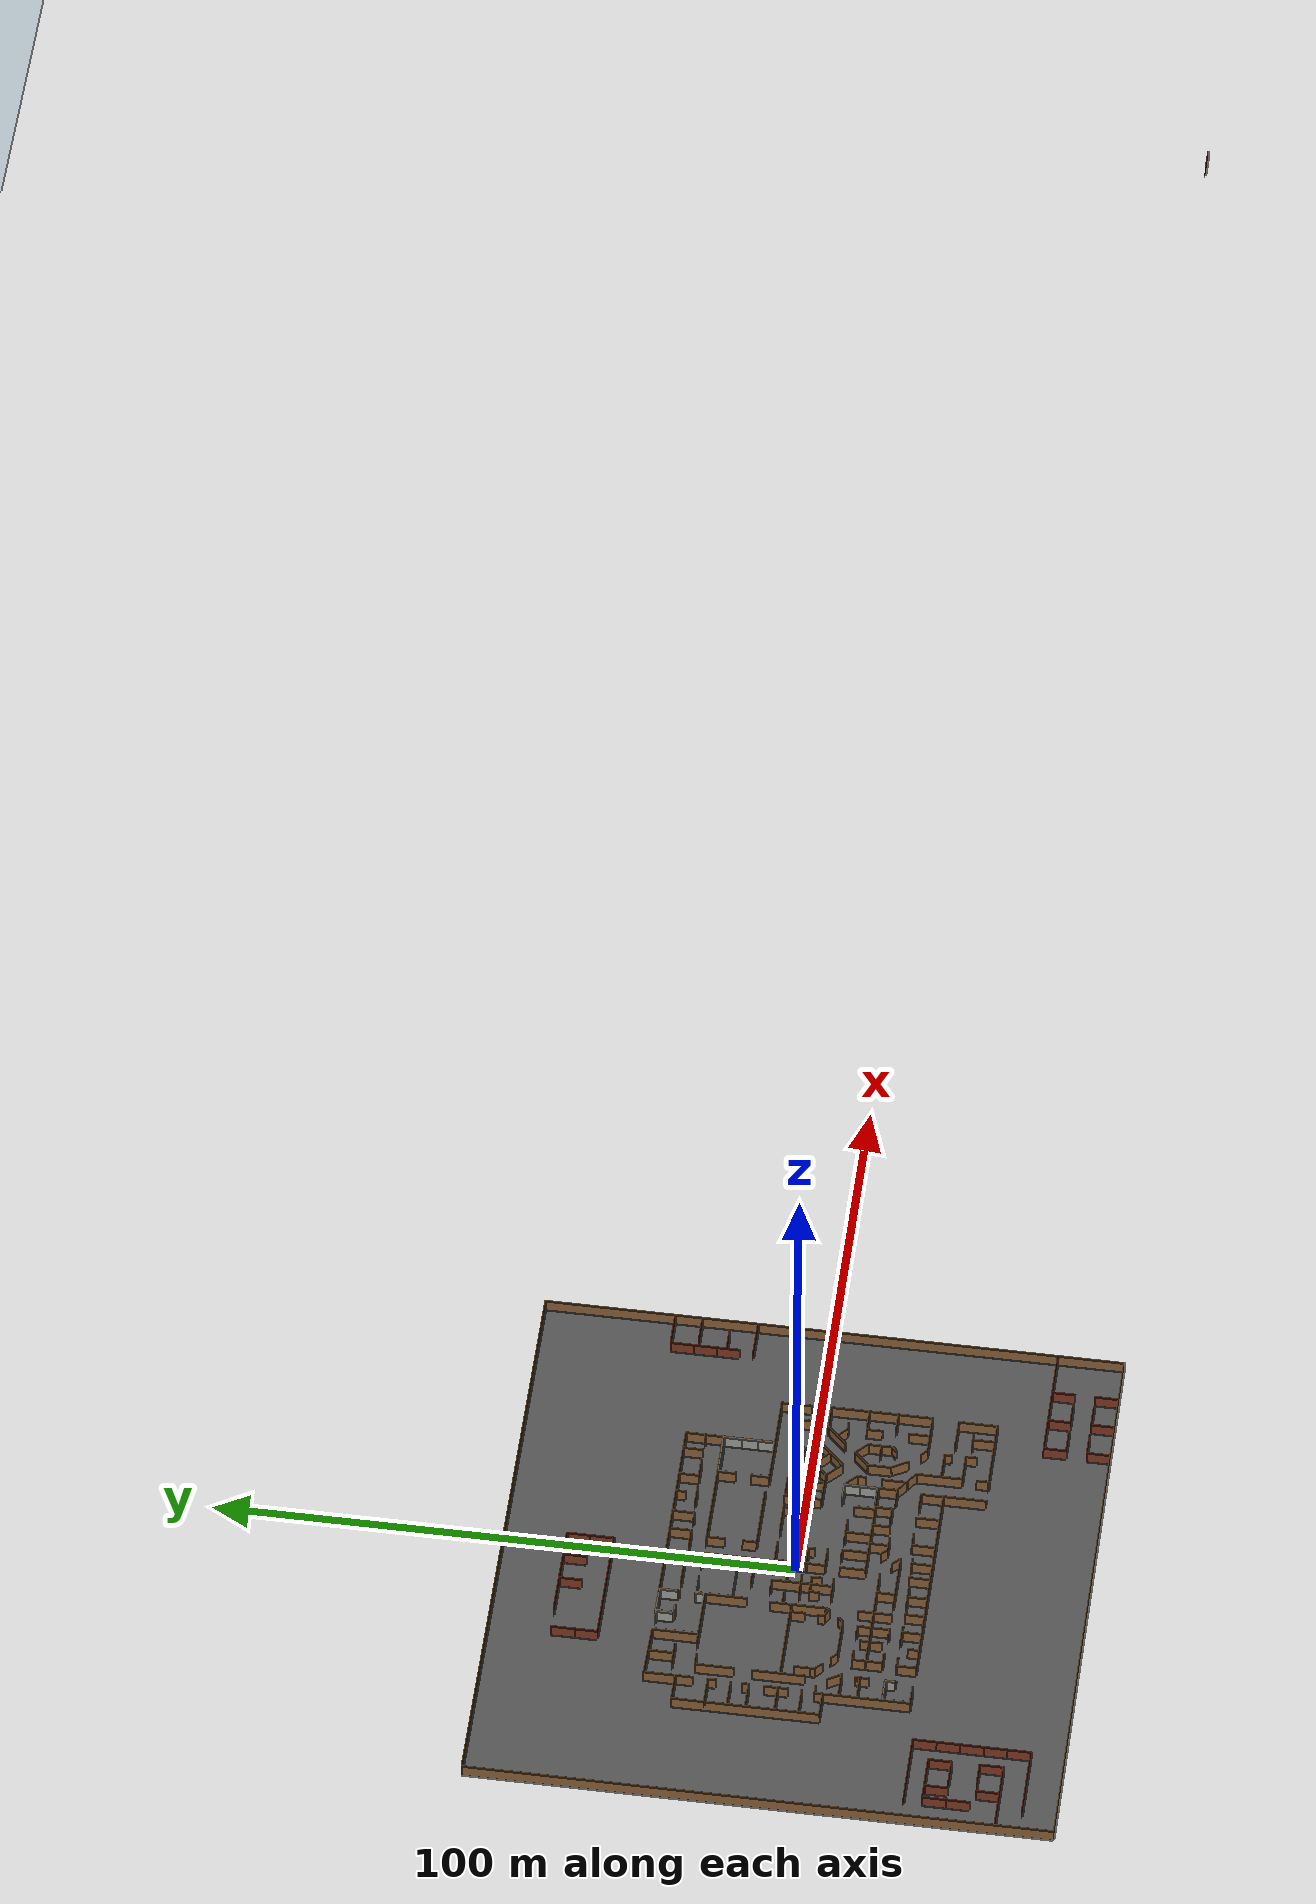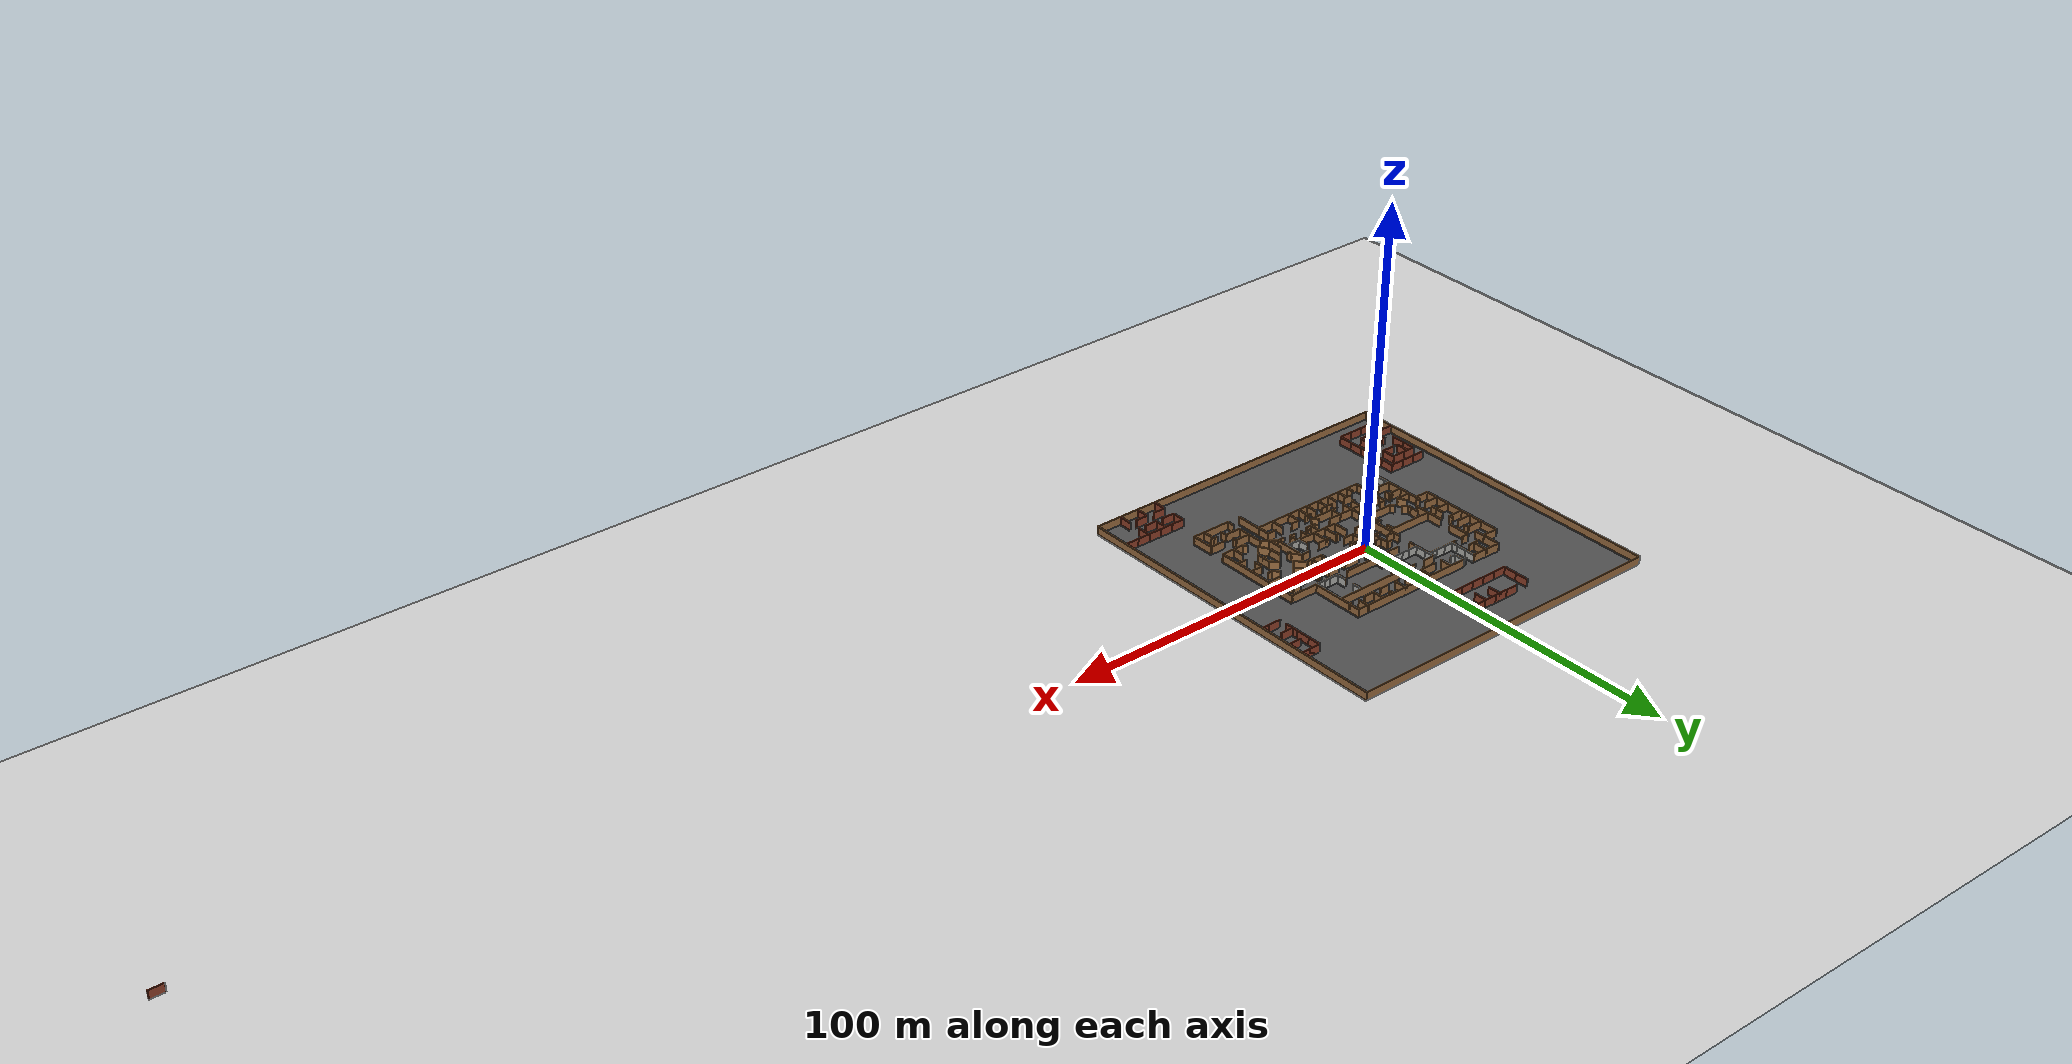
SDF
<sdf version="1.6">
 <world name="default">
  <light name="sun" type="directional">
   <pose>0 0 10 0 -0 0</pose>
   <diffuse>0.8 0.8 0.8 1</diffuse>
   <specular>0.2 0.2 0.2 1</specular>
   <attenuation>
    <range>1000</range>
    <constant>0.9</constant>
    <linear>0.01</linear>
    <quadratic>0.001</quadratic>
   </attenuation>
   <direction>-0.5 0.1 -0.9</direction>
  </light>
  <model name="ground_plane">
   <static>1</static>
   <link name="link">
    <collision name="collision">
     <geometry><plane><normal>0 0 1</normal><size>100 100</size></plane></geometry>
     <surface><friction><ode><mu>100</mu><mu2>50</mu2></ode></friction></surface>
    </collision>
    <visual name="visual">
     <cast_shadows>0</cast_shadows>
     <geometry><plane><normal>0 0 1</normal><size>100 100</size></plane></geometry>
     <material>
      <script><uri>file://media/materials/scripts/gazebo.material</uri><name>Gazebo/Grey</name></script>
     </material>
    </visual>
   </link>
  </model>
  <gravity>0 0 -9.8</gravity>
  <magnetic_field>6e-06 2.3e-05 -4.2e-05</magnetic_field>
  <atmosphere type="adiabatic"/>
  <physics name="default_physics" default="0" type="ode">
   <max_step_size>0.001</max_step_size>
   <real_time_factor>1</real_time_factor>
   <real_time_update_rate>1000</real_time_update_rate>
  </physics>
  <scene><ambient>0.4 0.4 0.4 1</ambient><background>0.7 0.7 0.7 1</background><shadows>1</shadows></scene>
  <audio><device>default</device></audio>
  <spherical_coordinates>
   <surface_model>EARTH_WGS84</surface_model>
   <latitude_deg>0</latitude_deg>
   <longitude_deg>0</longitude_deg>
   <elevation>0</elevation>
   <heading_deg>0</heading_deg>
  </spherical_coordinates>
  <model name="map_frame">
   <link name="Wall_0">
    <collision name="Wall_0_Collision">
     <geometry><box><size>100.05 0.15 2.5</size></box></geometry>
     <pose>0 0 1.25 0 -0 0</pose>
    </collision>
    <visual name="Wall_0_Visual">
     <pose>0 0 1.25 0 -0 0</pose>
     <geometry><box><size>100.05 0.15 2.5</size></box></geometry>
     <material>
      <script><uri>file://media/materials/scripts/gazebo.material</uri><name>Gazebo/Wood</name></script>
      <ambient>1 1 1 1</ambient>
     </material>
    </visual>
    <pose>0 50 0 0 -0 0</pose>
   </link>
   <link name="Wall_1">
    <collision name="Wall_1_Collision">
     <geometry><box><size>100.05 0.15 2.5</size></box></geometry>
     <pose>0 0 1.25 0 -0 0</pose>
    </collision>
    <visual name="Wall_1_Visual">
     <pose>0 0 1.25 0 -0 0</pose>
     <geometry><box><size>100.05 0.15 2.5</size></box></geometry>
     <material>
      <script><uri>file://media/materials/scripts/gazebo.material</uri><name>Gazebo/Wood</name></script>
      <ambient>1 1 1 1</ambient>
     </material>
    </visual>
    <pose>50 0 0 0 0 -1.5708</pose>
   </link>
   <link name="Wall_2">
    <collision name="Wall_2_Collision">
     <geometry><box><size>100.05 0.15 2.5</size></box></geometry>
     <pose>0 0 1.25 0 -0 0</pose>
    </collision>
    <visual name="Wall_2_Visual">
     <pose>0 0 1.25 0 -0 0</pose>
     <geometry><box><size>100.05 0.15 2.5</size></box></geometry>
     <material>
      <script><uri>file://media/materials/scripts/gazebo.material</uri><name>Gazebo/Wood</name></script>
      <ambient>1 1 1 1</ambient>
     </material>
    </visual>
    <pose>0 -50 0 0 -0 3.14159</pose>
   </link>
   <link name="Wall_3">
    <collision name="Wall_3_Collision">
     <geometry><box><size>100.05 0.15 2.5</size></box></geometry>
     <pose>0 0 1.25 0 -0 0</pose>
    </collision>
    <visual name="Wall_3_Visual">
     <pose>0 0 1.25 0 -0 0</pose>
     <geometry><box><size>100.05 0.15 2.5</size></box></geometry>
     <material>
      <script><uri>file://media/materials/scripts/gazebo.material</uri><name>Gazebo/Wood</name></script>
      <ambient>1 1 1 1</ambient>
     </material>
    </visual>
    <pose>-50 0 0 0 -0 1.5708</pose>
   </link>
   <static>1</static>
  </model>
  <model name="asphalt_plane">
   <static>1</static>
   <link name="link">
    <collision name="collision"><geometry><box><size>100 100 0.1</size></box></geometry></collision>
    <visual name="visual">
     <cast_shadows>0</cast_shadows>
     <geometry><box><size>100 100 0.1</size></box></geometry>
     <material>
      <script>
       <uri>model://asphalt_plane/materials/scripts</uri>
       <uri>model://asphalt_plane/materials/textures</uri>
       <name>vrc/asphalt</name>
      </script>
     </material>
    </visual>
   </link>
  </model>
  <model name="concrete_wall">
   <pose>-8.48668 14.4739 0 0 -0 0</pose>
   <link name="Wall_0">
    <collision name="Wall_0_Collision">
     <geometry><box><size>3 0.15 2.5</size></box></geometry>
     <pose>0 0 1.25 0 -0 0</pose>
    </collision>
    <visual name="Wall_0_Visual">
     <pose>0 0 1.25 0 -0 0</pose>
     <geometry><box><size>3 0.15 2.5</size></box></geometry>
     <material>
      <script><uri>file://media/materials/scripts/gazebo.material</uri><name>Gazebo/CeilingTiled</name></script>
      <ambient>1 1 1 1</ambient>
     </material>
     <meta><layer>0</layer></meta>
    </visual>
    <pose>0 0 0 0 -0 1.5708</pose>
   </link>
   <static>1</static>
  </model>
  <model name="concrete_wall_0">
   <pose>-8.48804 11.5232 0 0 -0 0</pose>
   <link name="Wall_0">
    <collision name="Wall_0_Collision">
     <geometry><box><size>3 0.15 2.5</size></box></geometry>
     <pose>0 0 1.25 0 -0 0</pose>
    </collision>
    <visual name="Wall_0_Visual">
     <pose>0 0 1.25 0 -0 0</pose>
     <geometry><box><size>3 0.15 2.5</size></box></geometry>
     <material>
      <script><uri>file://media/materials/scripts/gazebo.material</uri><name>Gazebo/CeilingTiled</name></script>
      <ambient>1 1 1 1</ambient>
     </material>
     <meta><layer>0</layer></meta>
    </visual>
    <pose>0 0 0 0 -0 1.5708</pose>
   </link>
   <static>1</static>
  </model>
  <model name="concrete_wall_1">
   <pose>-0.231026 14.3447 0 0 -0 0</pose>
   <link name="Wall_0">
    <collision name="Wall_0_Collision">
     <geometry><box><size>3 0.15 2.5</size></box></geometry>
     <pose>0 0 1.25 0 -0 0</pose>
    </collision>
    <visual name="Wall_0_Visual">
     <pose>0 0 1.25 0 -0 0</pose>
     <geometry><box><size>3 0.15 2.5</size></box></geometry>
     <material>
      <script><uri>file://media/materials/scripts/gazebo.material</uri><name>Gazebo/CeilingTiled</name></script>
      <ambient>1 1 1 1</ambient>
     </material>
     <meta><layer>0</layer></meta>
    </visual>
    <pose>0 0 0 0 -0 1.5708</pose>
   </link>
   <static>1</static>
  </model>
  <model name="concrete_wall_2">
   <pose>-0.252871 11.4504 0 0 -0 0</pose>
   <link name="Wall_0">
    <collision name="Wall_0_Collision">
     <geometry><box><size>3 0.15 2.5</size></box></geometry>
     <pose>0 0 1.25 0 -0 0</pose>
    </collision>
    <visual name="Wall_0_Visual">
     <pose>0 0 1.25 0 -0 0</pose>
     <geometry><box><size>3 0.15 2.5</size></box></geometry>
     <material>
      <script><uri>file://media/materials/scripts/gazebo.material</uri><name>Gazebo/CeilingTiled</name></script>
      <ambient>1 1 1 1</ambient>
     </material>
     <meta><layer>0</layer></meta>
    </visual>
    <pose>0 0 0 0 -0 1.5708</pose>
   </link>
   <static>1</static>
  </model>
  <model name="concrete_wall_3">
   <pose>-26.6192 -21.1644 0 0 -0 0</pose>
   <link name="Wall_0">
    <collision name="Wall_0_Collision">
     <geometry><box><size>3 0.15 2.5</size></box></geometry>
     <pose>0 0 1.25 0 -0 0</pose>
    </collision>
    <visual name="Wall_0_Visual">
     <pose>0 0 1.25 0 -0 0</pose>
     <geometry><box><size>3 0.15 2.5</size></box></geometry>
     <material>
      <script><uri>file://media/materials/scripts/gazebo.material</uri><name>Gazebo/CeilingTiled</name></script>
      <ambient>1 1 1 1</ambient>
     </material>
     <meta><layer>0</layer></meta>
    </visual>
    <pose>0 0 0 0 -0 1.5708</pose>
   </link>
   <static>1</static>
  </model>
  <model name="concrete_wall_4">
   <pose>-26.6244 -19.6415 0 0 -0 0</pose>
   <link name="Wall_0">
    <collision name="Wall_0_Collision">
     <geometry><box><size>3 0.15 2.5</size></box></geometry>
     <pose>0 0 1.25 0 -0 0</pose>
    </collision>
    <visual name="Wall_0_Visual">
     <pose>0 0 1.25 0 -0 0</pose>
     <geometry><box><size>3 0.15 2.5</size></box></geometry>
     <material>
      <script><uri>file://media/materials/scripts/gazebo.material</uri><name>Gazebo/CeilingTiled</name></script>
      <ambient>1 1 1 1</ambient>
     </material>
     <meta><layer>0</layer></meta>
    </visual>
    <pose>0 0 0 0 -0 1.5708</pose>
   </link>
   <static>1</static>
  </model>
  <model name="concrete_wall_6_clone">
   <pose>-25.1114 -22.6438 0 0 -0 1.57079</pose>
   <link name="Wall_0">
    <collision name="Wall_0_Collision">
     <geometry><box><size>3 0.15 2.5</size></box></geometry>
     <pose>0 0 1.25 0 -0 0</pose>
    </collision>
    <visual name="Wall_0_Visual">
     <pose>0 0 1.25 0 -0 0</pose>
     <geometry><box><size>3 0.15 2.5</size></box></geometry>
     <material>
      <script><uri>file://media/materials/scripts/gazebo.material</uri><name>Gazebo/CeilingTiled</name></script>
      <ambient>1 1 1 1</ambient>
     </material>
     <meta><layer>0</layer></meta>
    </visual>
    <pose>0 0 0 0 -0 1.5708</pose>
   </link>
   <static>1</static>
  </model>
  <model name="concrete_wall_6_clone_0">
   <pose>-25.1351 -18.2014 0 0 -0 1.57079</pose>
   <link name="Wall_0">
    <collision name="Wall_0_Collision">
     <geometry><box><size>3 0.15 2.5</size></box></geometry>
     <pose>0 0 1.25 0 -0 0</pose>
    </collision>
    <visual name="Wall_0_Visual">
     <pose>0 0 1.25 0 -0 0</pose>
     <geometry><box><size>3 0.15 2.5</size></box></geometry>
     <material>
      <script><uri>file://media/materials/scripts/gazebo.material</uri><name>Gazebo/CeilingTiled</name></script>
      <ambient>1 1 1 1</ambient>
     </material>
     <meta><layer>0</layer></meta>
    </visual>
    <pose>0 0 0 0 -0 1.5708</pose>
   </link>
   <static>1</static>
  </model>
  <model name="concrete_wall_6_clone_1">
   <pose>16.3445 -5.99981 0 0 -0 1.57079</pose>
   <link name="Wall_0">
    <collision name="Wall_0_Collision">
     <geometry><box><size>3 0.15 2.5</size></box></geometry>
     <pose>0 0 1.25 0 -0 0</pose>
    </collision>
    <visual name="Wall_0_Visual">
     <pose>0 0 1.25 0 -0 0</pose>
     <geometry><box><size>3 0.15 2.5</size></box></geometry>
     <material>
      <script><uri>file://media/materials/scripts/gazebo.material</uri><name>Gazebo/CeilingTiled</name></script>
      <ambient>1 1 1 1</ambient>
     </material>
     <meta><layer>0</layer></meta>
    </visual>
    <pose>0 0 0 0 -0 1.5708</pose>
   </link>
   <static>1</static>
  </model>
  <model name="concrete_wall_6_clone_2">
   <pose>15.9495 -11.5377 0 0 -0 1.57079</pose>
   <link name="Wall_0">
    <collision name="Wall_0_Collision">
     <geometry><box><size>3 0.15 2.5</size></box></geometry>
     <pose>0 0 1.25 0 -0 0</pose>
    </collision>
    <visual name="Wall_0_Visual">
     <pose>0 0 1.25 0 -0 0</pose>
     <geometry><box><size>3 0.15 2.5</size></box></geometry>
     <material>
      <script><uri>file://media/materials/scripts/gazebo.material</uri><name>Gazebo/CeilingTiled</name></script>
      <ambient>1 1 1 1</ambient>
     </material>
     <meta><layer>0</layer></meta>
    </visual>
    <pose>0 0 0 0 -0 1.5708</pose>
   </link>
   <static>1</static>
  </model>
  <model name="concrete_wall_6_clone_3">
   <pose>14.6748 -11.5357 0 0 -0 1.57079</pose>
   <link name="Wall_0">
    <collision name="Wall_0_Collision">
     <geometry><box><size>3 0.15 2.5</size></box></geometry>
     <pose>0 0 1.25 0 -0 0</pose>
    </collision>
    <visual name="Wall_0_Visual">
     <pose>0 0 1.25 0 -0 0</pose>
     <geometry><box><size>3 0.15 2.5</size></box></geometry>
     <material>
      <script><uri>file://media/materials/scripts/gazebo.material</uri><name>Gazebo/CeilingTiled</name></script>
      <ambient>1 1 1 1</ambient>
     </material>
     <meta><layer>0</layer></meta>
    </visual>
    <pose>0 0 0 0 -0 1.5708</pose>
   </link>
   <static>1</static>
  </model>
  <model name="concrete_wall_7">
   <pose>13.2693 -9.97942 0 0 -0 0</pose>
   <link name="Wall_0">
    <collision name="Wall_0_Collision">
     <geometry><box><size>3 0.15 2.5</size></box></geometry>
     <pose>0 0 1.25 0 -0 0</pose>
    </collision>
    <visual name="Wall_0_Visual">
     <pose>0 0 1.25 0 -0 0</pose>
     <geometry><box><size>3 0.15 2.5</size></box></geometry>
     <material>
      <script><uri>file://media/materials/scripts/gazebo.material</uri><name>Gazebo/CeilingTiled</name></script>
      <ambient>1 1 1 1</ambient>
     </material>
     <meta><layer>0</layer></meta>
    </visual>
    <pose>0 0 0 0 -0 1.5708</pose>
   </link>
   <static>1</static>
  </model>
  <model name="concrete_wall_8">
   <pose>17.5032 -10.1408 0 0 -0 0</pose>
   <link name="Wall_0">
    <collision name="Wall_0_Collision">
     <geometry><box><size>3 0.15 2.5</size></box></geometry>
     <pose>0 0 1.25 0 -0 0</pose>
    </collision>
    <visual name="Wall_0_Visual">
     <pose>0 0 1.25 0 -0 0</pose>
     <geometry><box><size>3 0.15 2.5</size></box></geometry>
     <material>
      <script><uri>file://media/materials/scripts/gazebo.material</uri><name>Gazebo/CeilingTiled</name></script>
      <ambient>1 1 1 1</ambient>
     </material>
     <meta><layer>0</layer></meta>
    </visual>
    <pose>0 0 0 0 -0 1.5708</pose>
   </link>
   <static>1</static>
  </model>
  <model name="concrete_wall_9">
   <pose>17.5144 -7.46989 0 0 -0 0</pose>
   <link name="Wall_0">
    <collision name="Wall_0_Collision">
     <geometry><box><size>3 0.15 2.5</size></box></geometry>
     <pose>0 0 1.25 0 -0 0</pose>
    </collision>
    <visual name="Wall_0_Visual">
     <pose>0 0 1.25 0 -0 0</pose>
     <geometry><box><size>3 0.15 2.5</size></box></geometry>
     <material>
      <script><uri>file://media/materials/scripts/gazebo.material</uri><name>Gazebo/CeilingTiled</name></script>
      <ambient>1 1 1 1</ambient>
     </material>
     <meta><layer>0</layer></meta>
    </visual>
    <pose>0 0 0 0 -0 1.5708</pose>
   </link>
   <static>1</static>
  </model>
  <model name="concrete_wall_6_clone_4">
   <pose>-1.64895 9.93911 0 0 -0 1.57079</pose>
   <link name="Wall_0">
    <collision name="Wall_0_Collision">
     <geometry><box><size>3 0.15 2.5</size></box></geometry>
     <pose>0 0 1.25 0 -0 0</pose>
    </collision>
    <visual name="Wall_0_Visual">
     <pose>0 0 1.25 0 -0 0</pose>
     <geometry><box><size>3 0.15 2.5</size></box></geometry>
     <material>
      <script><uri>file://media/materials/scripts/gazebo.material</uri><name>Gazebo/CeilingTiled</name></script>
      <ambient>1 1 1 1</ambient>
     </material>
     <meta><layer>0</layer></meta>
    </visual>
    <pose>0 0 0 0 -0 1.5708</pose>
   </link>
   <static>1</static>
  </model>
  <model name="concrete_wall_6_clone_5">
   <pose>-4.08866 9.93655 0 0 -0 1.57079</pose>
   <link name="Wall_0">
    <collision name="Wall_0_Collision">
     <geometry><box><size>3 0.15 2.5</size></box></geometry>
     <pose>0 0 1.25 0 -0 0</pose>
    </collision>
    <visual name="Wall_0_Visual">
     <pose>0 0 1.25 0 -0 0</pose>
     <geometry><box><size>3 0.15 2.5</size></box></geometry>
     <material>
      <script><uri>file://media/materials/scripts/gazebo.material</uri><name>Gazebo/CeilingTiled</name></script>
      <ambient>1 1 1 1</ambient>
     </material>
     <meta><layer>0</layer></meta>
    </visual>
    <pose>0 0 0 0 -0 1.5708</pose>
   </link>
   <static>1</static>
  </model>
  <model name="concrete_wall_6_clone_6">
   <pose>-7.05086 9.93464 0 0 -0 1.57079</pose>
   <link name="Wall_0">
    <collision name="Wall_0_Collision">
     <geometry><box><size>3 0.15 2.5</size></box></geometry>
     <pose>0 0 1.25 0 -0 0</pose>
    </collision>
    <visual name="Wall_0_Visual">
     <pose>0 0 1.25 0 -0 0</pose>
     <geometry><box><size>3 0.15 2.5</size></box></geometry>
     <material>
      <script><uri>file://media/materials/scripts/gazebo.material</uri><name>Gazebo/CeilingTiled</name></script>
      <ambient>1 1 1 1</ambient>
     </material>
     <meta><layer>0</layer></meta>
    </visual>
    <pose>0 0 0 0 -0 1.5708</pose>
   </link>
   <static>1</static>
  </model>
  <model name="concrete_wall_6_clone_7">
   <pose>-7.08346 16.0324 0 0 -0 1.57079</pose>
   <link name="Wall_0">
    <collision name="Wall_0_Collision">
     <geometry><box><size>3 0.15 2.5</size></box></geometry>
     <pose>0 0 1.25 0 -0 0</pose>
    </collision>
    <visual name="Wall_0_Visual">
     <pose>0 0 1.25 0 -0 0</pose>
     <geometry><box><size>3 0.15 2.5</size></box></geometry>
     <material>
      <script><uri>file://media/materials/scripts/gazebo.material</uri><name>Gazebo/CeilingTiled</name></script>
      <ambient>1 1 1 1</ambient>
     </material>
     <meta><layer>0</layer></meta>
    </visual>
    <pose>0 0 0 0 -0 1.5708</pose>
   </link>
   <static>1</static>
  </model>
  <model name="concrete_wall_6_clone_8">
   <pose>-1.01529 15.8 0 0 -0 1.57079</pose>
   <link name="Wall_0">
    <collision name="Wall_0_Collision">
     <geometry><box><size>1.5 0.15 2.5</size></box></geometry>
     <pose>0 0 1.25 0 -0 0</pose>
    </collision>
    <visual name="Wall_0_Visual">
     <pose>0 0 1.25 0 -0 0</pose>
     <geometry><box><size>1.5 0.15 2.5</size></box></geometry>
     <material>
      <script><uri>file://media/materials/scripts/gazebo.material</uri><name>Gazebo/CeilingTiled</name></script>
      <ambient>1 1 1 1</ambient>
     </material>
     <meta><layer>0</layer></meta>
    </visual>
    <pose>0 0 0 0 -0 1.5708</pose>
   </link>
   <static>1</static>
  </model>
  <model name="concrete_wall_6_clone_9">
   <pose>-15.5996 14.6023 0 0 -0 1.57079</pose>
   <link name="Wall_0">
    <collision name="Wall_0_Collision">
     <geometry><box><size>3 0.15 2.5</size></box></geometry>
     <pose>0 0 1.25 0 -0 0</pose>
    </collision>
    <visual name="Wall_0_Visual">
     <pose>0 0 1.25 0 -0 0</pose>
     <geometry><box><size>3 0.15 2.5</size></box></geometry>
     <material>
      <script><uri>file://media/materials/scripts/gazebo.material</uri><name>Gazebo/CeilingTiled</name></script>
      <ambient>1 1 1 1</ambient>
     </material>
     <meta><layer>0</layer></meta>
    </visual>
    <pose>0 0 0 0 -0 1.5708</pose>
   </link>
   <static>1</static>
  </model>
  <model name="concrete_wall_6_clone_10">
   <pose>-12.6135 14.583 0 0 -0 1.57079</pose>
   <link name="Wall_0">
    <collision name="Wall_0_Collision">
     <geometry><box><size>3 0.15 2.5</size></box></geometry>
     <pose>0 0 1.25 0 -0 0</pose>
    </collision>
    <visual name="Wall_0_Visual">
     <pose>0 0 1.25 0 -0 0</pose>
     <geometry><box><size>3 0.15 2.5</size></box></geometry>
     <material>
      <script><uri>file://media/materials/scripts/gazebo.material</uri><name>Gazebo/CeilingTiled</name></script>
      <ambient>1 1 1 1</ambient>
     </material>
     <meta><layer>0</layer></meta>
    </visual>
    <pose>0 0 0 0 -0 1.5708</pose>
   </link>
   <static>1</static>
  </model>
  <model name="concrete_wall_6_clone_11">
   <pose>-10.1743 14.5482 0 0 -0 1.57079</pose>
   <link name="Wall_0">
    <collision name="Wall_0_Collision">
     <geometry><box><size>3 0.15 2.5</size></box></geometry>
     <pose>0 0 1.25 0 -0 0</pose>
    </collision>
    <visual name="Wall_0_Visual">
     <pose>0 0 1.25 0 -0 0</pose>
     <geometry><box><size>3 0.15 2.5</size></box></geometry>
     <material>
      <script><uri>file://media/materials/scripts/gazebo.material</uri><name>Gazebo/CeilingTiled</name></script>
      <ambient>1 1 1 1</ambient>
     </material>
     <meta><layer>0</layer></meta>
    </visual>
    <pose>0 0 0 0 -0 1.5708</pose>
   </link>
   <static>1</static>
  </model>
  <model name="concrete_wall_6_clone_12">
   <pose>-10.1874 22.0907 0 0 -0 1.57079</pose>
   <link name="Wall_0">
    <collision name="Wall_0_Collision">
     <geometry><box><size>3 0.15 2.5</size></box></geometry>
     <pose>0 0 1.25 0 -0 0</pose>
    </collision>
    <visual name="Wall_0_Visual">
     <pose>0 0 1.25 0 -0 0</pose>
     <geometry><box><size>3 0.15 2.5</size></box></geometry>
     <material>
      <script><uri>file://media/materials/scripts/gazebo.material</uri><name>Gazebo/CeilingTiled</name></script>
      <ambient>1 1 1 1</ambient>
     </material>
     <meta><layer>0</layer></meta>
    </visual>
    <pose>0 0 0 0 -0 1.5708</pose>
   </link>
   <static>1</static>
  </model>
  <model name="concrete_wall_6_clone_13">
   <pose>-12.8935 22.121 0 0 -0 1.57079</pose>
   <link name="Wall_0">
    <collision name="Wall_0_Collision">
     <geometry><box><size>3 0.15 2.5</size></box></geometry>
     <pose>0 0 1.25 0 -0 0</pose>
    </collision>
    <visual name="Wall_0_Visual">
     <pose>0 0 1.25 0 -0 0</pose>
     <geometry><box><size>3 0.15 2.5</size></box></geometry>
     <material>
      <script><uri>file://media/materials/scripts/gazebo.material</uri><name>Gazebo/CeilingTiled</name></script>
      <ambient>1 1 1 1</ambient>
     </material>
     <meta><layer>0</layer></meta>
    </visual>
    <pose>0 0 0 0 -0 1.5708</pose>
   </link>
   <static>1</static>
  </model>
  <model name="concrete_wall_10">
   <pose>-17.0452 17.8135 0 0 -0 0</pose>
   <link name="Wall_0">
    <collision name="Wall_0_Collision">
     <geometry><box><size>3 0.15 2.5</size></box></geometry>
     <pose>0 0 1.25 0 -0 0</pose>
    </collision>
    <visual name="Wall_0_Visual">
     <pose>0 0 1.25 0 -0 0</pose>
     <geometry><box><size>3 0.15 2.5</size></box></geometry>
     <material>
      <script><uri>file://media/materials/scripts/gazebo.material</uri><name>Gazebo/CeilingTiled</name></script>
      <ambient>1 1 1 1</ambient>
     </material>
     <meta><layer>0</layer></meta>
    </visual>
    <pose>0 0 0 0 -0 1.5708</pose>
   </link>
   <static>1</static>
  </model>
  <model name="concrete_wall_11">
   <pose>-17.0415 20.8179 0 0 -0 0</pose>
   <link name="Wall_0">
    <collision name="Wall_0_Collision">
     <geometry><box><size>3 0.15 2.5</size></box></geometry>
     <pose>0 0 1.25 0 -0 0</pose>
    </collision>
    <visual name="Wall_0_Visual">
     <pose>0 0 1.25 0 -0 0</pose>
     <geometry><box><size>3 0.15 2.5</size></box></geometry>
     <material>
      <script><uri>file://media/materials/scripts/gazebo.material</uri><name>Gazebo/CeilingTiled</name></script>
      <ambient>1 1 1 1</ambient>
     </material>
     <meta><layer>0</layer></meta>
    </visual>
    <pose>0 0 0 0 -0 1.5708</pose>
   </link>
   <static>1</static>
  </model>
  <model name="concrete_wall_12">
   <pose>-8.68965 20.6247 0 0 -0 0</pose>
   <link name="Wall_0">
    <collision name="Wall_0_Collision">
     <geometry><box><size>3 0.15 2.5</size></box></geometry>
     <pose>0 0 1.25 0 -0 0</pose>
    </collision>
    <visual name="Wall_0_Visual">
     <pose>0 0 1.25 0 -0 0</pose>
     <geometry><box><size>3 0.15 2.5</size></box></geometry>
     <material>
      <script><uri>file://media/materials/scripts/gazebo.material</uri><name>Gazebo/CeilingTiled</name></script>
      <ambient>1 1 1 1</ambient>
     </material>
     <meta><layer>0</layer></meta>
    </visual>
    <pose>0 0 0 0 -0 1.5708</pose>
   </link>
   <static>1</static>
  </model>
  <model name="concrete_wall_13">
   <pose>-17.0666 16.0035 0 0 -0 0</pose>
   <link name="Wall_0">
    <collision name="Wall_0_Collision">
     <geometry><box><size>3 0.15 2.5</size></box></geometry>
     <pose>0 0 1.25 0 -0 0</pose>
    </collision>
    <visual name="Wall_0_Visual">
     <pose>0 0 1.25 0 -0 0</pose>
     <geometry><box><size>3 0.15 2.5</size></box></geometry>
     <material>
      <script><uri>file://media/materials/scripts/gazebo.material</uri><name>Gazebo/CeilingTiled</name></script>
      <ambient>1 1 1 1</ambient>
     </material>
     <meta><layer>0</layer></meta>
    </visual>
    <pose>0 0 0 0 -0 1.5708</pose>
   </link>
   <static>1</static>
  </model>
  <model name="concrete_wall_14">
   <pose>-13.1615 20.7156 0 0 -0 0</pose>
   <link name="Wall_0">
    <collision name="Wall_0_Collision">
     <geometry><box><size>3 0.15 2.5</size></box></geometry>
     <pose>0 0 1.25 0 -0 0</pose>
    </collision>
    <visual name="Wall_0_Visual">
     <pose>0 0 1.25 0 -0 0</pose>
     <geometry><box><size>3 0.15 2.5</size></box></geometry>
     <material>
      <script><uri>file://media/materials/scripts/gazebo.material</uri><name>Gazebo/CeilingTiled</name></script>
      <ambient>1 1 1 1</ambient>
     </material>
     <meta><layer>0</layer></meta>
    </visual>
    <pose>0 0 0 0 -0 1.5708</pose>
   </link>
   <static>1</static>
  </model>
  <model name="concrete_wall_6_clone_15">
   <pose>19.0082 7.09385 0 0 -0 1.57079</pose>
   <link name="Wall_0">
    <collision name="Wall_0_Collision">
     <geometry><box><size>3 0.15 2.5</size></box></geometry>
     <pose>0 0 1.25 0 -0 0</pose>
    </collision>
    <visual name="Wall_0_Visual">
     <pose>0 0 1.25 0 -0 0</pose>
     <geometry><box><size>3 0.15 2.5</size></box></geometry>
     <material>
      <script><uri>file://media/materials/scripts/gazebo.material</uri><name>Gazebo/CeilingTiled</name></script>
      <ambient>1 1 1 1</ambient>
     </material>
     <meta><layer>0</layer></meta>
    </visual>
    <pose>0 0 0 0 -0 1.5708</pose>
   </link>
   <static>1</static>
  </model>
  <model name="concrete_wall_6_clone_16">
   <pose>20.5949 7.06095 0 0 -0 1.57079</pose>
   <link name="Wall_0">
    <collision name="Wall_0_Collision">
     <geometry><box><size>3 0.15 2.5</size></box></geometry>
     <pose>0 0 1.25 0 -0 0</pose>
    </collision>
    <visual name="Wall_0_Visual">
     <pose>0 0 1.25 0 -0 0</pose>
     <geometry><box><size>3 0.15 2.5</size></box></geometry>
     <material>
      <script><uri>file://media/materials/scripts/gazebo.material</uri><name>Gazebo/CeilingTiled</name></script>
      <ambient>1 1 1 1</ambient>
     </material>
     <meta><layer>0</layer></meta>
    </visual>
    <pose>0 0 0 0 -0 1.5708</pose>
   </link>
   <static>1</static>
  </model>
  <model name="concrete_wall_6_clone_17">
   <pose>23.3706 7.05229 0 0 -0 1.57079</pose>
   <link name="Wall_0">
    <collision name="Wall_0_Collision">
     <geometry><box><size>3 0.15 2.5</size></box></geometry>
     <pose>0 0 1.25 0 -0 0</pose>
    </collision>
    <visual name="Wall_0_Visual">
     <pose>0 0 1.25 0 -0 0</pose>
     <geometry><box><size>3 0.15 2.5</size></box></geometry>
     <material>
      <script><uri>file://media/materials/scripts/gazebo.material</uri><name>Gazebo/CeilingTiled</name></script>
      <ambient>1 1 1 1</ambient>
     </material>
     <meta><layer>0</layer></meta>
    </visual>
    <pose>0 0 0 0 -0 1.5708</pose>
   </link>
   <static>1</static>
  </model>
  <model name="concrete_wall_6_clone_18">
   <pose>23.5039 15.7147 0 0 -0 1.57079</pose>
   <link name="Wall_0">
    <collision name="Wall_0_Collision">
     <geometry><box><size>3 0.15 2.5</size></box></geometry>
     <pose>0 0 1.25 0 -0 0</pose>
    </collision>
    <visual name="Wall_0_Visual">
     <pose>0 0 1.25 0 -0 0</pose>
     <geometry><box><size>3 0.15 2.5</size></box></geometry>
     <material>
      <script><uri>file://media/materials/scripts/gazebo.material</uri><name>Gazebo/CeilingTiled</name></script>
      <ambient>1 1 1 1</ambient>
     </material>
     <meta><layer>0</layer></meta>
    </visual>
    <pose>0 0 0 0 -0 1.5708</pose>
   </link>
   <static>1</static>
  </model>
  <model name="concrete_wall_6_clone_19">
   <pose>21.9639 15.6573 0 0 -0 1.57079</pose>
   <link name="Wall_0">
    <collision name="Wall_0_Collision">
     <geometry><box><size>3 0.15 2.5</size></box></geometry>
     <pose>0 0 1.25 0 -0 0</pose>
    </collision>
    <visual name="Wall_0_Visual">
     <pose>0 0 1.25 0 -0 0</pose>
     <geometry><box><size>3 0.15 2.5</size></box></geometry>
     <material>
      <script><uri>file://media/materials/scripts/gazebo.material</uri><name>Gazebo/CeilingTiled</name></script>
      <ambient>1 1 1 1</ambient>
     </material>
     <meta><layer>0</layer></meta>
    </visual>
    <pose>0 0 0 0 -0 1.5708</pose>
   </link>
   <static>1</static>
  </model>
  <model name="concrete_wall_6_clone_20">
   <pose>19.0587 15.6479 0 0 -0 1.57079</pose>
   <link name="Wall_0">
    <collision name="Wall_0_Collision">
     <geometry><box><size>3 0.15 2.5</size></box></geometry>
     <pose>0 0 1.25 0 -0 0</pose>
    </collision>
    <visual name="Wall_0_Visual">
     <pose>0 0 1.25 0 -0 0</pose>
     <geometry><box><size>3 0.15 2.5</size></box></geometry>
     <material>
      <script><uri>file://media/materials/scripts/gazebo.material</uri><name>Gazebo/CeilingTiled</name></script>
      <ambient>1 1 1 1</ambient>
     </material>
     <meta><layer>0</layer></meta>
    </visual>
    <pose>0 0 0 0 -0 1.5708</pose>
   </link>
   <static>1</static>
  </model>
  <model name="concrete_wall_15">
   <pose>24.8729 8.48253 0 0 -0 0</pose>
   <link name="Wall_0">
    <collision name="Wall_0_Collision">
     <geometry><box><size>3 0.15 2.5</size></box></geometry>
     <pose>0 0 1.25 0 -0 0</pose>
    </collision>
    <visual name="Wall_0_Visual">
     <pose>0 0 1.25 0 -0 0</pose>
     <geometry><box><size>3 0.15 2.5</size></box></geometry>
     <material>
      <script><uri>file://media/materials/scripts/gazebo.material</uri><name>Gazebo/CeilingTiled</name></script>
      <ambient>1 1 1 1</ambient>
     </material>
     <meta><layer>0</layer></meta>
    </visual>
    <pose>0 0 0 0 -0 1.5708</pose>
   </link>
   <static>1</static>
  </model>
  <model name="concrete_wall_16">
   <pose>17.5839 8.5954 0 0 -0 0</pose>
   <link name="Wall_0">
    <collision name="Wall_0_Collision">
     <geometry><box><size>3 0.15 2.5</size></box></geometry>
     <pose>0 0 1.25 0 -0 0</pose>
    </collision>
    <visual name="Wall_0_Visual">
     <pose>0 0 1.25 0 -0 0</pose>
     <geometry><box><size>3 0.15 2.5</size></box></geometry>
     <material>
      <script><uri>file://media/materials/scripts/gazebo.material</uri><name>Gazebo/CeilingTiled</name></script>
      <ambient>1 1 1 1</ambient>
     </material>
     <meta><layer>0</layer></meta>
    </visual>
    <pose>0 0 0 0 -0 1.5708</pose>
   </link>
   <static>1</static>
  </model>
  <model name="concrete_wall_18">
   <pose>17.6374 14.261 0 0 -0 0</pose>
   <link name="Wall_0">
    <collision name="Wall_0_Collision">
     <geometry><box><size>3 0.15 2.5</size></box></geometry>
     <pose>0 0 1.25 0 -0 0</pose>
    </collision>
    <visual name="Wall_0_Visual">
     <pose>0 0 1.25 0 -0 0</pose>
     <geometry><box><size>3 0.15 2.5</size></box></geometry>
     <material>
      <script><uri>file://media/materials/scripts/gazebo.material</uri><name>Gazebo/CeilingTiled</name></script>
      <ambient>1 1 1 1</ambient>
     </material>
     <meta><layer>0</layer></meta>
    </visual>
    <pose>0 0 0 0 -0 1.5708</pose>
   </link>
   <static>1</static>
  </model>
  <model name="concrete_wall_19">
   <pose>24.8866 11.194 0 0 -0 0</pose>
   <link name="Wall_0">
    <collision name="Wall_0_Collision">
     <geometry><box><size>3 0.15 2.5</size></box></geometry>
     <pose>0 0 1.25 0 -0 0</pose>
    </collision>
    <visual name="Wall_0_Visual">
     <pose>0 0 1.25 0 -0 0</pose>
     <geometry><box><size>3 0.15 2.5</size></box></geometry>
     <material>
      <script><uri>file://media/materials/scripts/gazebo.material</uri><name>Gazebo/CeilingTiled</name></script>
      <ambient>1 1 1 1</ambient>
     </material>
     <meta><layer>0</layer></meta>
    </visual>
    <pose>0 0 0 0 -0 1.5708</pose>
   </link>
   <static>1</static>
  </model>
  <model name="concrete_wall_20">
   <pose>24.896 14.1844 0 0 -0 0</pose>
   <link name="Wall_0">
    <collision name="Wall_0_Collision">
     <geometry><box><size>3 0.15 2.5</size></box></geometry>
     <pose>0 0 1.25 0 -0 0</pose>
    </collision>
    <visual name="Wall_0_Visual">
     <pose>0 0 1.25 0 -0 0</pose>
     <geometry><box><size>3 0.15 2.5</size></box></geometry>
     <material>
      <script><uri>file://media/materials/scripts/gazebo.material</uri><name>Gazebo/CeilingTiled</name></script>
      <ambient>1 1 1 1</ambient>
     </material>
     <meta><layer>0</layer></meta>
    </visual>
    <pose>0 0 0 0 -0 1.5708</pose>
   </link>
   <static>1</static>
  </model>
  <model name="brick_wall">
   <pose>47.9451 -38.5658 0 0 -0 0</pose>
   <link name="Wall_0">
    <collision name="Wall_0_Collision">
     <geometry><box><size>4 0.15 2.5</size></box></geometry>
     <pose>0 0 1.25 0 -0 0</pose>
    </collision>
    <visual name="Wall_0_Visual">
     <pose>0 0 1.25 0 -0 0</pose>
     <geometry><box><size>4 0.15 2.5</size></box></geometry>
     <material>
      <script><uri>file://media/materials/scripts/gazebo.material</uri><name>Gazebo/Bricks</name></script>
      <ambient>1 1 1 1</ambient>
     </material>
     <meta><layer>0</layer></meta>
    </visual>
   </link>
   <static>1</static>
  </model>
  <model name="brick_wall_0">
   <pose>43.9451 -38.5658 0 0 -0 0</pose>
   <link name="Wall_0">
    <collision name="Wall_0_Collision">
     <geometry><box><size>4 0.15 2.5</size></box></geometry>
     <pose>0 0 1.25 0 -0 0</pose>
    </collision>
    <visual name="Wall_0_Visual">
     <pose>0 0 1.25 0 -0 0</pose>
     <geometry><box><size>4 0.15 2.5</size></box></geometry>
     <material>
      <script><uri>file://media/materials/scripts/gazebo.material</uri><name>Gazebo/Bricks</name></script>
      <ambient>1 1 1 1</ambient>
     </material>
     <meta><layer>0</layer></meta>
    </visual>
   </link>
   <static>1</static>
  </model>
  <model name="brick_wall_clone">
   <pose>39.9451 -38.5658 0 0 -0 0</pose>
   <link name="Wall_0">
    <collision name="Wall_0_Collision">
     <geometry><box><size>4 0.15 2.5</size></box></geometry>
     <pose>0 0 1.25 0 -0 0</pose>
    </collision>
    <visual name="Wall_0_Visual">
     <pose>0 0 1.25 0 -0 0</pose>
     <geometry><box><size>4 0.15 2.5</size></box></geometry>
     <material>
      <script><uri>file://media/materials/scripts/gazebo.material</uri><name>Gazebo/Bricks</name></script>
      <ambient>1 1 1 1</ambient>
     </material>
     <meta><layer>0</layer></meta>
    </visual>
   </link>
   <static>1</static>
  </model>
  <model name="brick_wall_clone_0">
   <pose>35.9451 -38.5658 0 0 -0 0</pose>
   <link name="Wall_0">
    <collision name="Wall_0_Collision">
     <geometry><box><size>4 0.15 2.5</size></box></geometry>
     <pose>0 0 1.25 0 -0 0</pose>
    </collision>
    <visual name="Wall_0_Visual">
     <pose>0 0 1.25 0 -0 0</pose>
     <geometry><box><size>4 0.15 2.5</size></box></geometry>
     <material>
      <script><uri>file://media/materials/scripts/gazebo.material</uri><name>Gazebo/Bricks</name></script>
      <ambient>1 1 1 1</ambient>
     </material>
     <meta><layer>0</layer></meta>
    </visual>
   </link>
   <static>1</static>
  </model>
  <model name="brick_wall_clone_1">
   <pose>31.9451 -38.5658 0 0 -0 0</pose>
   <link name="Wall_0">
    <collision name="Wall_0_Collision">
     <geometry><box><size>4 0.15 2.5</size></box></geometry>
     <pose>0 0 1.25 0 -0 0</pose>
    </collision>
    <visual name="Wall_0_Visual">
     <pose>0 0 1.25 0 -0 0</pose>
     <geometry><box><size>4 0.15 2.5</size></box></geometry>
     <material>
      <script><uri>file://media/materials/scripts/gazebo.material</uri><name>Gazebo/Bricks</name></script>
      <ambient>1 1 1 1</ambient>
     </material>
     <meta><layer>0</layer></meta>
    </visual>
   </link>
   <static>1</static>
  </model>
  <model name="brick_wall_clone_2">
   <pose>327.945 -32.3274 0 0 -0 0</pose>
   <link name="Wall_0">
    <collision name="Wall_0_Collision">
     <geometry><box><size>4 0.15 2.5</size></box></geometry>
     <pose>0 0 1.25 0 -0 0</pose>
    </collision>
    <visual name="Wall_0_Visual">
     <pose>0 0 1.25 0 -0 0</pose>
     <geometry><box><size>4 0.15 2.5</size></box></geometry>
     <material>
      <script><uri>file://media/materials/scripts/gazebo.material</uri><name>Gazebo/Bricks</name></script>
      <ambient>1 1 1 1</ambient>
     </material>
     <meta><layer>0</layer></meta>
    </visual>
   </link>
   <static>1</static>
  </model>
  <model name="brick_wall_1">
   <pose>29.9233 -40.4954 0 0 -0 1.57079</pose>
   <link name="Wall_0">
    <collision name="Wall_0_Collision">
     <geometry><box><size>4 0.15 2.5</size></box></geometry>
     <pose>0 0 1.25 0 -0 0</pose>
    </collision>
    <visual name="Wall_0_Visual">
     <pose>0 0 1.25 0 -0 0</pose>
     <geometry><box><size>4 0.15 2.5</size></box></geometry>
     <material>
      <script><uri>file://media/materials/scripts/gazebo.material</uri><name>Gazebo/Bricks</name></script>
      <ambient>1 1 1 1</ambient>
     </material>
     <meta><layer>0</layer></meta>
    </visual>
   </link>
   <static>1</static>
  </model>
  <model name="brick_wall_1_clone">
   <pose>29.9233 -47.9139 0 0 -0 1.57079</pose>
   <link name="Wall_0">
    <collision name="Wall_0_Collision">
     <geometry><box><size>4 0.15 2.5</size></box></geometry>
     <pose>0 0 1.25 0 -0 0</pose>
    </collision>
    <visual name="Wall_0_Visual">
     <pose>0 0 1.25 0 -0 0</pose>
     <geometry><box><size>4 0.15 2.5</size></box></geometry>
     <material>
      <script><uri>file://media/materials/scripts/gazebo.material</uri><name>Gazebo/Bricks</name></script>
      <ambient>1 1 1 1</ambient>
     </material>
     <meta><layer>0</layer></meta>
    </visual>
   </link>
   <static>1</static>
  </model>
  <model name="brick_wall_clone_3">
   <pose>31.9806 -42.4199 0 0 -0 0</pose>
   <link name="Wall_0">
    <collision name="Wall_0_Collision">
     <geometry><box><size>4 0.15 2.5</size></box></geometry>
     <pose>0 0 1.25 0 -0 0</pose>
    </collision>
    <visual name="Wall_0_Visual">
     <pose>0 0 1.25 0 -0 0</pose>
     <geometry><box><size>4 0.15 2.5</size></box></geometry>
     <material>
      <script><uri>file://media/materials/scripts/gazebo.material</uri><name>Gazebo/Bricks</name></script>
      <ambient>1 1 1 1</ambient>
     </material>
     <meta><layer>0</layer></meta>
    </visual>
   </link>
   <static>1</static>
  </model>
  <model name="brick_wall_clone_4">
   <pose>31.933 -45.9888 0 0 -0 0</pose>
   <link name="Wall_0">
    <collision name="Wall_0_Collision">
     <geometry><box><size>4 0.15 2.5</size></box></geometry>
     <pose>0 0 1.25 0 -0 0</pose>
    </collision>
    <visual name="Wall_0_Visual">
     <pose>0 0 1.25 0 -0 0</pose>
     <geometry><box><size>4 0.15 2.5</size></box></geometry>
     <material>
      <script><uri>file://media/materials/scripts/gazebo.material</uri><name>Gazebo/Bricks</name></script>
      <ambient>1 1 1 1</ambient>
     </material>
     <meta><layer>0</layer></meta>
    </visual>
   </link>
   <static>1</static>
  </model>
  <model name="brick_wall_1_clone_0">
   <pose>36.0534 -40.4954 0 0 -0 1.57079</pose>
   <link name="Wall_0">
    <collision name="Wall_0_Collision">
     <geometry><box><size>4 0.15 2.5</size></box></geometry>
     <pose>0 0 1.25 0 -0 0</pose>
    </collision>
    <visual name="Wall_0_Visual">
     <pose>0 0 1.25 0 -0 0</pose>
     <geometry><box><size>4 0.15 2.5</size></box></geometry>
     <material>
      <script><uri>file://media/materials/scripts/gazebo.material</uri><name>Gazebo/Bricks</name></script>
      <ambient>1 1 1 1</ambient>
     </material>
     <meta><layer>0</layer></meta>
    </visual>
   </link>
   <static>1</static>
  </model>
  <model name="brick_wall_1_clone_1">
   <pose>36.0534 -47.9139 0 0 -0 1.57079</pose>
   <link name="Wall_0">
    <collision name="Wall_0_Collision">
     <geometry><box><size>4 0.15 2.5</size></box></geometry>
     <pose>0 0 1.25 0 -0 0</pose>
    </collision>
    <visual name="Wall_0_Visual">
     <pose>0 0 1.25 0 -0 0</pose>
     <geometry><box><size>4 0.15 2.5</size></box></geometry>
     <material>
      <script><uri>file://media/materials/scripts/gazebo.material</uri><name>Gazebo/Bricks</name></script>
      <ambient>1 1 1 1</ambient>
     </material>
     <meta><layer>0</layer></meta>
    </visual>
   </link>
   <static>1</static>
  </model>
  <model name="brick_wall_clone_5">
   <pose>38.0534 -42.4199 0 0 -0 0</pose>
   <link name="Wall_0">
    <collision name="Wall_0_Collision">
     <geometry><box><size>4 0.15 2.5</size></box></geometry>
     <pose>0 0 1.25 0 -0 0</pose>
    </collision>
    <visual name="Wall_0_Visual">
     <pose>0 0 1.25 0 -0 0</pose>
     <geometry><box><size>4 0.15 2.5</size></box></geometry>
     <material>
      <script><uri>file://media/materials/scripts/gazebo.material</uri><name>Gazebo/Bricks</name></script>
      <ambient>1 1 1 1</ambient>
     </material>
     <meta><layer>0</layer></meta>
    </visual>
   </link>
   <static>1</static>
  </model>
  <model name="brick_wall_clone_6">
   <pose>38.0534 -45.9888 0 0 -0 0</pose>
   <link name="Wall_0">
    <collision name="Wall_0_Collision">
     <geometry><box><size>4 0.15 2.5</size></box></geometry>
     <pose>0 0 1.25 0 -0 0</pose>
    </collision>
    <visual name="Wall_0_Visual">
     <pose>0 0 1.25 0 -0 0</pose>
     <geometry><box><size>4 0.15 2.5</size></box></geometry>
     <material>
      <script><uri>file://media/materials/scripts/gazebo.material</uri><name>Gazebo/Bricks</name></script>
      <ambient>1 1 1 1</ambient>
     </material>
     <meta><layer>0</layer></meta>
    </visual>
   </link>
   <static>1</static>
  </model>
  <model name="brick_wall_1_clone_2">
   <pose>42.0728 -40.4954 0 0 -0 1.57079</pose>
   <link name="Wall_0">
    <collision name="Wall_0_Collision">
     <geometry><box><size>4 0.15 2.5</size></box></geometry>
     <pose>0 0 1.25 0 -0 0</pose>
    </collision>
    <visual name="Wall_0_Visual">
     <pose>0 0 1.25 0 -0 0</pose>
     <geometry><box><size>4 0.15 2.5</size></box></geometry>
     <material>
      <script><uri>file://media/materials/scripts/gazebo.material</uri><name>Gazebo/Bricks</name></script>
      <ambient>1 1 1 1</ambient>
     </material>
     <meta><layer>0</layer></meta>
    </visual>
   </link>
   <static>1</static>
  </model>
  <model name="brick_wall_1_clone_3">
   <pose>42.0767 -47.9139 0 0 -0 1.57079</pose>
   <link name="Wall_0">
    <collision name="Wall_0_Collision">
     <geometry><box><size>4 0.15 2.5</size></box></geometry>
     <pose>0 0 1.25 0 -0 0</pose>
    </collision>
    <visual name="Wall_0_Visual">
     <pose>0 0 1.25 0 -0 0</pose>
     <geometry><box><size>4 0.15 2.5</size></box></geometry>
     <material>
      <script><uri>file://media/materials/scripts/gazebo.material</uri><name>Gazebo/Bricks</name></script>
      <ambient>1 1 1 1</ambient>
     </material>
     <meta><layer>0</layer></meta>
    </visual>
   </link>
   <static>1</static>
  </model>
  <model name="brick_wall_2">
   <pose>-0.863663 31.3819 0 0 -0 0</pose>
   <link name="Wall_0">
    <collision name="Wall_0_Collision">
     <geometry><box><size>4 0.15 2.5</size></box></geometry>
     <pose>0 0 1.25 0 -0 0</pose>
    </collision>
    <visual name="Wall_0_Visual">
     <pose>0 0 1.25 0 -0 0</pose>
     <geometry><box><size>4 0.15 2.5</size></box></geometry>
     <material>
      <script><uri>file://media/materials/scripts/gazebo.material</uri><name>Gazebo/Bricks</name></script>
      <ambient>1 1 1 1</ambient>
     </material>
     <meta><layer>0</layer></meta>
    </visual>
   </link>
   <static>1</static>
  </model>
  <model name="brick_wall_2_clone">
   <pose>-4.86366 31.3819 0 0 -0 0</pose>
   <link name="Wall_0">
    <collision name="Wall_0_Collision">
     <geometry><box><size>4 0.15 2.5</size></box></geometry>
     <pose>0 0 1.25 0 -0 0</pose>
    </collision>
    <visual name="Wall_0_Visual">
     <pose>0 0 1.25 0 -0 0</pose>
     <geometry><box><size>4 0.15 2.5</size></box></geometry>
     <material>
      <script><uri>file://media/materials/scripts/gazebo.material</uri><name>Gazebo/Bricks</name></script>
      <ambient>1 1 1 1</ambient>
     </material>
     <meta><layer>0</layer></meta>
    </visual>
   </link>
   <static>1</static>
  </model>
  <model name="brick_wall_2_clone_0">
   <pose>-8.86366 31.3819 0 0 -0 0</pose>
   <link name="Wall_0">
    <collision name="Wall_0_Collision">
     <geometry><box><size>4 0.15 2.5</size></box></geometry>
     <pose>0 0 1.25 0 -0 0</pose>
    </collision>
    <visual name="Wall_0_Visual">
     <pose>0 0 1.25 0 -0 0</pose>
     <geometry><box><size>4 0.15 2.5</size></box></geometry>
     <material>
      <script><uri>file://media/materials/scripts/gazebo.material</uri><name>Gazebo/Bricks</name></script>
      <ambient>1 1 1 1</ambient>
     </material>
     <meta><layer>0</layer></meta>
    </visual>
   </link>
   <static>1</static>
  </model>
  <model name="brick_wall_2_clone_1">
   <pose>-12.8637 31.3819 0 0 -0 0</pose>
   <link name="Wall_0">
    <collision name="Wall_0_Collision">
     <geometry><box><size>4 0.15 2.5</size></box></geometry>
     <pose>0 0 1.25 0 -0 0</pose>
    </collision>
    <visual name="Wall_0_Visual">
     <pose>0 0 1.25 0 -0 0</pose>
     <geometry><box><size>4 0.15 2.5</size></box></geometry>
     <material>
      <script><uri>file://media/materials/scripts/gazebo.material</uri><name>Gazebo/Bricks</name></script>
      <ambient>1 1 1 1</ambient>
     </material>
     <meta><layer>0</layer></meta>
    </visual>
   </link>
   <static>1</static>
  </model>
  <model name="brick_wall_2_clone_2">
   <pose>-16.8637 31.3819 0 0 -0 0</pose>
   <link name="Wall_0">
    <collision name="Wall_0_Collision">
     <geometry><box><size>4 0.15 2.5</size></box></geometry>
     <pose>0 0 1.25 0 -0 0</pose>
    </collision>
    <visual name="Wall_0_Visual">
     <pose>0 0 1.25 0 -0 0</pose>
     <geometry><box><size>4 0.15 2.5</size></box></geometry>
     <material>
      <script><uri>file://media/materials/scripts/gazebo.material</uri><name>Gazebo/Bricks</name></script>
      <ambient>1 1 1 1</ambient>
     </material>
     <meta><layer>0</layer></meta>
    </visual>
   </link>
   <static>1</static>
  </model>
  <model name="brick_wall_2_clone_3">
   <pose>-0.863663 39.3819 0 0 -0 0</pose>
   <link name="Wall_0">
    <collision name="Wall_0_Collision">
     <geometry><box><size>4 0.15 2.5</size></box></geometry>
     <pose>0 0 1.25 0 -0 0</pose>
    </collision>
    <visual name="Wall_0_Visual">
     <pose>0 0 1.25 0 -0 0</pose>
     <geometry><box><size>4 0.15 2.5</size></box></geometry>
     <material>
      <script><uri>file://media/materials/scripts/gazebo.material</uri><name>Gazebo/Bricks</name></script>
      <ambient>1 1 1 1</ambient>
     </material>
     <meta><layer>0</layer></meta>
    </visual>
   </link>
   <static>1</static>
  </model>
  <model name="brick_wall_2_clone_4">
   <pose>-4.86366 39.3819 0 0 -0 0</pose>
   <link name="Wall_0">
    <collision name="Wall_0_Collision">
     <geometry><box><size>4 0.15 2.5</size></box></geometry>
     <pose>0 0 1.25 0 -0 0</pose>
    </collision>
    <visual name="Wall_0_Visual">
     <pose>0 0 1.25 0 -0 0</pose>
     <geometry><box><size>4 0.15 2.5</size></box></geometry>
     <material>
      <script><uri>file://media/materials/scripts/gazebo.material</uri><name>Gazebo/Bricks</name></script>
      <ambient>1 1 1 1</ambient>
     </material>
     <meta><layer>0</layer></meta>
    </visual>
   </link>
   <static>1</static>
  </model>
  <model name="brick_wall_2_clone_5">
   <pose>-8.86366 39.3819 0 0 -0 0</pose>
   <link name="Wall_0">
    <collision name="Wall_0_Collision">
     <geometry><box><size>4 0.15 2.5</size></box></geometry>
     <pose>0 0 1.25 0 -0 0</pose>
    </collision>
    <visual name="Wall_0_Visual">
     <pose>0 0 1.25 0 -0 0</pose>
     <geometry><box><size>4 0.15 2.5</size></box></geometry>
     <material>
      <script><uri>file://media/materials/scripts/gazebo.material</uri><name>Gazebo/Bricks</name></script>
      <ambient>1 1 1 1</ambient>
     </material>
     <meta><layer>0</layer></meta>
    </visual>
   </link>
   <static>1</static>
  </model>
  <model name="brick_wall_2_clone_6">
   <pose>-12.8637 39.3819 0 0 -0 0</pose>
   <link name="Wall_0">
    <collision name="Wall_0_Collision">
     <geometry><box><size>4 0.15 2.5</size></box></geometry>
     <pose>0 0 1.25 0 -0 0</pose>
    </collision>
    <visual name="Wall_0_Visual">
     <pose>0 0 1.25 0 -0 0</pose>
     <geometry><box><size>4 0.15 2.5</size></box></geometry>
     <material>
      <script><uri>file://media/materials/scripts/gazebo.material</uri><name>Gazebo/Bricks</name></script>
      <ambient>1 1 1 1</ambient>
     </material>
     <meta><layer>0</layer></meta>
    </visual>
   </link>
   <static>1</static>
  </model>
  <model name="brick_wall_3">
   <pose>1.06218 33.4428 0 0 -0 1.57079</pose>
   <link name="Wall_0">
    <collision name="Wall_0_Collision">
     <geometry><box><size>4 0.15 2.5</size></box></geometry>
     <pose>0 0 1.25 0 -0 0</pose>
    </collision>
    <visual name="Wall_0_Visual">
     <pose>0 0 1.25 0 -0 0</pose>
     <geometry><box><size>4 0.15 2.5</size></box></geometry>
     <material>
      <script><uri>file://media/materials/scripts/gazebo.material</uri><name>Gazebo/Bricks</name></script>
      <ambient>1 1 1 1</ambient>
     </material>
     <meta><layer>0</layer></meta>
    </visual>
   </link>
   <static>1</static>
  </model>
  <model name="brick_wall_3_clone">
   <pose>1.06218 37.4428 0 0 -0 1.57079</pose>
   <link name="Wall_0">
    <collision name="Wall_0_Collision">
     <geometry><box><size>4 0.15 2.5</size></box></geometry>
     <pose>0 0 1.25 0 -0 0</pose>
    </collision>
    <visual name="Wall_0_Visual">
     <pose>0 0 1.25 0 -0 0</pose>
     <geometry><box><size>4 0.15 2.5</size></box></geometry>
     <material>
      <script><uri>file://media/materials/scripts/gazebo.material</uri><name>Gazebo/Bricks</name></script>
      <ambient>1 1 1 1</ambient>
     </material>
     <meta><layer>0</layer></meta>
    </visual>
   </link>
   <static>1</static>
  </model>
  <model name="brick_wall_3_clone_0">
   <pose>-18.914 33.2967 0 0 -0 1.57079</pose>
   <link name="Wall_0">
    <collision name="Wall_0_Collision">
     <geometry><box><size>4 0.15 2.5</size></box></geometry>
     <pose>0 0 1.25 0 -0 0</pose>
    </collision>
    <visual name="Wall_0_Visual">
     <pose>0 0 1.25 0 -0 0</pose>
     <geometry><box><size>4 0.15 2.5</size></box></geometry>
     <material>
      <script><uri>file://media/materials/scripts/gazebo.material</uri><name>Gazebo/Bricks</name></script>
      <ambient>1 1 1 1</ambient>
     </material>
     <meta><layer>0</layer></meta>
    </visual>
   </link>
   <static>1</static>
  </model>
  <model name="brick_wall_3_clone_1">
   <pose>-18.914 37.2967 0 0 -0 1.57079</pose>
   <link name="Wall_0">
    <collision name="Wall_0_Collision">
     <geometry><box><size>4 0.15 2.5</size></box></geometry>
     <pose>0 0 1.25 0 -0 0</pose>
    </collision>
    <visual name="Wall_0_Visual">
     <pose>0 0 1.25 0 -0 0</pose>
     <geometry><box><size>4 0.15 2.5</size></box></geometry>
     <material>
      <script><uri>file://media/materials/scripts/gazebo.material</uri><name>Gazebo/Bricks</name></script>
      <ambient>1 1 1 1</ambient>
     </material>
     <meta><layer>0</layer></meta>
    </visual>
   </link>
   <static>1</static>
  </model>
  <model name="brick_wall_3_clone_2">
   <pose>-3.48128 37.3947 0 0 -0 1.57079</pose>
   <link name="Wall_0">
    <collision name="Wall_0_Collision">
     <geometry><box><size>4 0.15 2.5</size></box></geometry>
     <pose>0 0 1.25 0 -0 0</pose>
    </collision>
    <visual name="Wall_0_Visual">
     <pose>0 0 1.25 0 -0 0</pose>
     <geometry><box><size>4 0.15 2.5</size></box></geometry>
     <material>
      <script><uri>file://media/materials/scripts/gazebo.material</uri><name>Gazebo/Bricks</name></script>
      <ambient>1 1 1 1</ambient>
     </material>
     <meta><layer>0</layer></meta>
    </visual>
   </link>
   <static>1</static>
  </model>
  <model name="brick_wall_3_clone_3">
   <pose>-8.49204 37.4632 0 0 -0 1.57079</pose>
   <link name="Wall_0">
    <collision name="Wall_0_Collision">
     <geometry><box><size>4 0.15 2.5</size></box></geometry>
     <pose>0 0 1.25 0 -0 0</pose>
    </collision>
    <visual name="Wall_0_Visual">
     <pose>0 0 1.25 0 -0 0</pose>
     <geometry><box><size>4 0.15 2.5</size></box></geometry>
     <material>
      <script><uri>file://media/materials/scripts/gazebo.material</uri><name>Gazebo/Bricks</name></script>
      <ambient>1 1 1 1</ambient>
     </material>
     <meta><layer>0</layer></meta>
    </visual>
   </link>
   <static>1</static>
  </model>
  <model name="brick_wall_clone_7">
   <pose>-44.2 -24.2 0 0 -0 0</pose>
   <link name="Wall_0">
    <collision name="Wall_0_Collision">
     <geometry><box><size>4 0.15 2.5</size></box></geometry>
     <pose>0 0 1.25 0 -0 0</pose>
    </collision>
    <visual name="Wall_0_Visual">
     <pose>0 0 1.25 0 -0 0</pose>
     <geometry><box><size>4 0.15 2.5</size></box></geometry>
     <material>
      <script><uri>file://media/materials/scripts/gazebo.material</uri><name>Gazebo/Bricks</name></script>
      <ambient>1 1 1 1</ambient>
     </material>
     <meta><layer>0</layer></meta>
    </visual>
   </link>
   <static>1</static>
  </model>
  <model name="brick_wall_clone_8">
   <pose>-40.2 -24.2 0 0 -0 0</pose>
   <link name="Wall_0">
    <collision name="Wall_0_Collision">
     <geometry><box><size>4 0.15 2.5</size></box></geometry>
     <pose>0 0 1.25 0 -0 0</pose>
    </collision>
    <visual name="Wall_0_Visual">
     <pose>0 0 1.25 0 -0 0</pose>
     <geometry><box><size>4 0.15 2.5</size></box></geometry>
     <material>
      <script><uri>file://media/materials/scripts/gazebo.material</uri><name>Gazebo/Bricks</name></script>
      <ambient>1 1 1 1</ambient>
     </material>
     <meta><layer>0</layer></meta>
    </visual>
   </link>
   <static>1</static>
  </model>
  <model name="brick_wall_clone_9">
   <pose>-36.2 -24.2 0 0 -0 0</pose>
   <link name="Wall_0">
    <collision name="Wall_0_Collision">
     <geometry><box><size>4 0.15 2.5</size></box></geometry>
     <pose>0 0 1.25 0 -0 0</pose>
    </collision>
    <visual name="Wall_0_Visual">
     <pose>0 0 1.25 0 -0 0</pose>
     <geometry><box><size>4 0.15 2.5</size></box></geometry>
     <material>
      <script><uri>file://media/materials/scripts/gazebo.material</uri><name>Gazebo/Bricks</name></script>
      <ambient>1 1 1 1</ambient>
     </material>
     <meta><layer>0</layer></meta>
    </visual>
   </link>
   <static>1</static>
  </model>
  <model name="brick_wall_clone_10">
   <pose>-43.9084 -27.3 0 0 -0 0</pose>
   <link name="Wall_0">
    <collision name="Wall_0_Collision">
     <geometry><box><size>4 0.15 2.5</size></box></geometry>
     <pose>0 0 1.25 0 -0 0</pose>
    </collision>
    <visual name="Wall_0_Visual">
     <pose>0 0 1.25 0 -0 0</pose>
     <geometry><box><size>4 0.15 2.5</size></box></geometry>
     <material>
      <script><uri>file://media/materials/scripts/gazebo.material</uri><name>Gazebo/Bricks</name></script>
      <ambient>1 1 1 1</ambient>
     </material>
     <meta><layer>0</layer></meta>
    </visual>
   </link>
   <static>1</static>
  </model>
  <model name="brick_wall_clone_11">
   <pose>-39.9084 -27.3 0 0 -0 0</pose>
   <link name="Wall_0">
    <collision name="Wall_0_Collision">
     <geometry><box><size>4 0.15 2.5</size></box></geometry>
     <pose>0 0 1.25 0 -0 0</pose>
    </collision>
    <visual name="Wall_0_Visual">
     <pose>0 0 1.25 0 -0 0</pose>
     <geometry><box><size>4 0.15 2.5</size></box></geometry>
     <material>
      <script><uri>file://media/materials/scripts/gazebo.material</uri><name>Gazebo/Bricks</name></script>
      <ambient>1 1 1 1</ambient>
     </material>
     <meta><layer>0</layer></meta>
    </visual>
   </link>
   <static>1</static>
  </model>
  <model name="brick_wall_clone_12">
   <pose>-36.2 -44.2 0 0 -0 0</pose>
   <link name="Wall_0">
    <collision name="Wall_0_Collision">
     <geometry><box><size>4 0.15 2.5</size></box></geometry>
     <pose>0 0 1.25 0 -0 0</pose>
    </collision>
    <visual name="Wall_0_Visual">
     <pose>0 0 1.25 0 -0 0</pose>
     <geometry><box><size>4 0.15 2.5</size></box></geometry>
     <material>
      <script><uri>file://media/materials/scripts/gazebo.material</uri><name>Gazebo/Bricks</name></script>
      <ambient>1 1 1 1</ambient>
     </material>
     <meta><layer>0</layer></meta>
    </visual>
   </link>
   <static>1</static>
  </model>
  <model name="brick_wall_clone_13">
   <pose>-40.2 -44.2 0 0 -0 0</pose>
   <link name="Wall_0">
    <collision name="Wall_0_Collision">
     <geometry><box><size>4 0.15 2.5</size></box></geometry>
     <pose>0 0 1.25 0 -0 0</pose>
    </collision>
    <visual name="Wall_0_Visual">
     <pose>0 0 1.25 0 -0 0</pose>
     <geometry><box><size>4 0.15 2.5</size></box></geometry>
     <material>
      <script><uri>file://media/materials/scripts/gazebo.material</uri><name>Gazebo/Bricks</name></script>
      <ambient>1 1 1 1</ambient>
     </material>
     <meta><layer>0</layer></meta>
    </visual>
   </link>
   <static>1</static>
  </model>
  <model name="brick_wall_clone_14">
   <pose>-44.2 -44.2 0 0 -0 0</pose>
   <link name="Wall_0">
    <collision name="Wall_0_Collision">
     <geometry><box><size>4 0.15 2.5</size></box></geometry>
     <pose>0 0 1.25 0 -0 0</pose>
    </collision>
    <visual name="Wall_0_Visual">
     <pose>0 0 1.25 0 -0 0</pose>
     <geometry><box><size>4 0.15 2.5</size></box></geometry>
     <material>
      <script><uri>file://media/materials/scripts/gazebo.material</uri><name>Gazebo/Bricks</name></script>
      <ambient>1 1 1 1</ambient>
     </material>
     <meta><layer>0</layer></meta>
    </visual>
   </link>
   <static>1</static>
  </model>
  <model name="brick_wall_clone_15">
   <pose>-47.9084 -40 0 0 -0 0</pose>
   <link name="Wall_0">
    <collision name="Wall_0_Collision">
     <geometry><box><size>4 0.15 2.5</size></box></geometry>
     <pose>0 0 1.25 0 -0 0</pose>
    </collision>
    <visual name="Wall_0_Visual">
     <pose>0 0 1.25 0 -0 0</pose>
     <geometry><box><size>4 0.15 2.5</size></box></geometry>
     <material>
      <script><uri>file://media/materials/scripts/gazebo.material</uri><name>Gazebo/Bricks</name></script>
      <ambient>1 1 1 1</ambient>
     </material>
     <meta><layer>0</layer></meta>
    </visual>
   </link>
   <static>1</static>
  </model>
  <model name="brick_wall_clone_16">
   <pose>-43.9084 -40 0 0 -0 0</pose>
   <link name="Wall_0">
    <collision name="Wall_0_Collision">
     <geometry><box><size>4 0.15 2.5</size></box></geometry>
     <pose>0 0 1.25 0 -0 0</pose>
    </collision>
    <visual name="Wall_0_Visual">
     <pose>0 0 1.25 0 -0 0</pose>
     <geometry><box><size>4 0.15 2.5</size></box></geometry>
     <material>
      <script><uri>file://media/materials/scripts/gazebo.material</uri><name>Gazebo/Bricks</name></script>
      <ambient>1 1 1 1</ambient>
     </material>
     <meta><layer>0</layer></meta>
    </visual>
   </link>
   <static>1</static>
  </model>
  <model name="brick_wall_clone_17">
   <pose>-39.9084 -40 0 0 -0 0</pose>
   <link name="Wall_0">
    <collision name="Wall_0_Collision">
     <geometry><box><size>4 0.15 2.5</size></box></geometry>
     <pose>0 0 1.25 0 -0 0</pose>
    </collision>
    <visual name="Wall_0_Visual">
     <pose>0 0 1.25 0 -0 0</pose>
     <geometry><box><size>4 0.15 2.5</size></box></geometry>
     <material>
      <script><uri>file://media/materials/scripts/gazebo.material</uri><name>Gazebo/Bricks</name></script>
      <ambient>1 1 1 1</ambient>
     </material>
     <meta><layer>0</layer></meta>
    </visual>
   </link>
   <static>1</static>
  </model>
  <model name="brick_wall_clone_18">
   <pose>-39.9084 -36 0 0 -0 0</pose>
   <link name="Wall_0">
    <collision name="Wall_0_Collision">
     <geometry><box><size>4 0.15 2.5</size></box></geometry>
     <pose>0 0 1.25 0 -0 0</pose>
    </collision>
    <visual name="Wall_0_Visual">
     <pose>0 0 1.25 0 -0 0</pose>
     <geometry><box><size>4 0.15 2.5</size></box></geometry>
     <material>
      <script><uri>file://media/materials/scripts/gazebo.material</uri><name>Gazebo/Bricks</name></script>
      <ambient>1 1 1 1</ambient>
     </material>
     <meta><layer>0</layer></meta>
    </visual>
   </link>
   <static>1</static>
  </model>
  <model name="brick_wall_clone_19">
   <pose>-39.9084 -31.2445 0 0 -0 0</pose>
   <link name="Wall_0">
    <collision name="Wall_0_Collision">
     <geometry><box><size>4 0.15 2.5</size></box></geometry>
     <pose>0 0 1.25 0 -0 0</pose>
    </collision>
    <visual name="Wall_0_Visual">
     <pose>0 0 1.25 0 -0 0</pose>
     <geometry><box><size>4 0.15 2.5</size></box></geometry>
     <material>
      <script><uri>file://media/materials/scripts/gazebo.material</uri><name>Gazebo/Bricks</name></script>
      <ambient>1 1 1 1</ambient>
     </material>
     <meta><layer>0</layer></meta>
    </visual>
   </link>
   <static>1</static>
  </model>
  <model name="brick_wall_1_clone_4">
   <pose>-34.2 -42.2 0 0 -0 1.57079</pose>
   <link name="Wall_0">
    <collision name="Wall_0_Collision">
     <geometry><box><size>4 0.15 2.5</size></box></geometry>
     <pose>0 0 1.25 0 -0 0</pose>
    </collision>
    <visual name="Wall_0_Visual">
     <pose>0 0 1.25 0 -0 0</pose>
     <geometry><box><size>4 0.15 2.5</size></box></geometry>
     <material>
      <script><uri>file://media/materials/scripts/gazebo.material</uri><name>Gazebo/Bricks</name></script>
      <ambient>1 1 1 1</ambient>
     </material>
     <meta><layer>0</layer></meta>
    </visual>
   </link>
   <static>1</static>
  </model>
  <model name="brick_wall_1_clone_5">
   <pose>-34.2 -38.2 0 0 -0 1.57079</pose>
   <link name="Wall_0">
    <collision name="Wall_0_Collision">
     <geometry><box><size>4 0.15 2.5</size></box></geometry>
     <pose>0 0 1.25 0 -0 0</pose>
    </collision>
    <visual name="Wall_0_Visual">
     <pose>0 0 1.25 0 -0 0</pose>
     <geometry><box><size>4 0.15 2.5</size></box></geometry>
     <material>
      <script><uri>file://media/materials/scripts/gazebo.material</uri><name>Gazebo/Bricks</name></script>
      <ambient>1 1 1 1</ambient>
     </material>
     <meta><layer>0</layer></meta>
    </visual>
   </link>
   <static>1</static>
  </model>
  <model name="brick_wall_1_clone_6">
   <pose>-34.2 -34.2 0 0 -0 1.57079</pose>
   <link name="Wall_0">
    <collision name="Wall_0_Collision">
     <geometry><box><size>4 0.15 2.5</size></box></geometry>
     <pose>0 0 1.25 0 -0 0</pose>
    </collision>
    <visual name="Wall_0_Visual">
     <pose>0 0 1.25 0 -0 0</pose>
     <geometry><box><size>4 0.15 2.5</size></box></geometry>
     <material>
      <script><uri>file://media/materials/scripts/gazebo.material</uri><name>Gazebo/Bricks</name></script>
      <ambient>1 1 1 1</ambient>
     </material>
     <meta><layer>0</layer></meta>
    </visual>
   </link>
   <static>1</static>
  </model>
  <model name="brick_wall_1_clone_7">
   <pose>-34.2 -30.2 0 0 -0 1.57079</pose>
   <link name="Wall_0">
    <collision name="Wall_0_Collision">
     <geometry><box><size>4 0.15 2.5</size></box></geometry>
     <pose>0 0 1.25 0 -0 0</pose>
    </collision>
    <visual name="Wall_0_Visual">
     <pose>0 0 1.25 0 -0 0</pose>
     <geometry><box><size>4 0.15 2.5</size></box></geometry>
     <material>
      <script><uri>file://media/materials/scripts/gazebo.material</uri><name>Gazebo/Bricks</name></script>
      <ambient>1 1 1 1</ambient>
     </material>
     <meta><layer>0</layer></meta>
    </visual>
   </link>
   <static>1</static>
  </model>
  <model name="brick_wall_1_clone_8">
   <pose>-34.2 -26.2 0 0 -0 1.57079</pose>
   <link name="Wall_0">
    <collision name="Wall_0_Collision">
     <geometry><box><size>4 0.15 2.5</size></box></geometry>
     <pose>0 0 1.25 0 -0 0</pose>
    </collision>
    <visual name="Wall_0_Visual">
     <pose>0 0 1.25 0 -0 0</pose>
     <geometry><box><size>4 0.15 2.5</size></box></geometry>
     <material>
      <script><uri>file://media/materials/scripts/gazebo.material</uri><name>Gazebo/Bricks</name></script>
      <ambient>1 1 1 1</ambient>
     </material>
     <meta><layer>0</layer></meta>
    </visual>
   </link>
   <static>1</static>
  </model>
  <model name="brick_wall_1_clone_9">
   <pose>-37.9084 -38 0 0 -0 1.57079</pose>
   <link name="Wall_0">
    <collision name="Wall_0_Collision">
     <geometry><box><size>4 0.15 2.5</size></box></geometry>
     <pose>0 0 1.25 0 -0 0</pose>
    </collision>
    <visual name="Wall_0_Visual">
     <pose>0 0 1.25 0 -0 0</pose>
     <geometry><box><size>4 0.15 2.5</size></box></geometry>
     <material>
      <script><uri>file://media/materials/scripts/gazebo.material</uri><name>Gazebo/Bricks</name></script>
      <ambient>1 1 1 1</ambient>
     </material>
     <meta><layer>0</layer></meta>
    </visual>
   </link>
   <static>1</static>
  </model>
  <model name="brick_wall_1_clone_10">
   <pose>-37.9551 -29.3 0 0 -0 1.57079</pose>
   <link name="Wall_0">
    <collision name="Wall_0_Collision">
     <geometry><box><size>4 0.15 2.5</size></box></geometry>
     <pose>0 0 1.25 0 -0 0</pose>
    </collision>
    <visual name="Wall_0_Visual">
     <pose>0 0 1.25 0 -0 0</pose>
     <geometry><box><size>4 0.15 2.5</size></box></geometry>
     <material>
      <script><uri>file://media/materials/scripts/gazebo.material</uri><name>Gazebo/Bricks</name></script>
      <ambient>1 1 1 1</ambient>
     </material>
     <meta><layer>0</layer></meta>
    </visual>
   </link>
   <static>1</static>
  </model>
  <model name="brick_wall_1_clone_11">
   <pose>-45.8877 -29.3 0 0 -0 1.57079</pose>
   <link name="Wall_0">
    <collision name="Wall_0_Collision">
     <geometry><box><size>4 0.15 2.5</size></box></geometry>
     <pose>0 0 1.25 0 -0 0</pose>
    </collision>
    <visual name="Wall_0_Visual">
     <pose>0 0 1.25 0 -0 0</pose>
     <geometry><box><size>4 0.15 2.5</size></box></geometry>
     <material>
      <script><uri>file://media/materials/scripts/gazebo.material</uri><name>Gazebo/Bricks</name></script>
      <ambient>1 1 1 1</ambient>
     </material>
     <meta><layer>0</layer></meta>
    </visual>
   </link>
   <static>1</static>
  </model>
  <model name="brick_wall_1_clone_12">
   <pose>-43.4 -29.3 0 0 -0 1.57079</pose>
   <link name="Wall_0">
    <collision name="Wall_0_Collision">
     <geometry><box><size>4 0.15 2.5</size></box></geometry>
     <pose>0 0 1.25 0 -0 0</pose>
    </collision>
    <visual name="Wall_0_Visual">
     <pose>0 0 1.25 0 -0 0</pose>
     <geometry><box><size>4 0.15 2.5</size></box></geometry>
     <material>
      <script><uri>file://media/materials/scripts/gazebo.material</uri><name>Gazebo/Bricks</name></script>
      <ambient>1 1 1 1</ambient>
     </material>
     <meta><layer>0</layer></meta>
    </visual>
   </link>
   <static>1</static>
  </model>
  <model name="brick_wall_1_clone_13">
   <pose>-43.4 -38 0 0 -0 1.57079</pose>
   <link name="Wall_0">
    <collision name="Wall_0_Collision">
     <geometry><box><size>4 0.15 2.5</size></box></geometry>
     <pose>0 0 1.25 0 -0 0</pose>
    </collision>
    <visual name="Wall_0_Visual">
     <pose>0 0 1.25 0 -0 0</pose>
     <geometry><box><size>4 0.15 2.5</size></box></geometry>
     <material>
      <script><uri>file://media/materials/scripts/gazebo.material</uri><name>Gazebo/Bricks</name></script>
      <ambient>1 1 1 1</ambient>
     </material>
     <meta><layer>0</layer></meta>
    </visual>
   </link>
   <static>1</static>
  </model>
  <model name="brick_wall_1_clone_14">
   <pose>-45.8877 -33.3 0 0 -0 1.57079</pose>
   <link name="Wall_0">
    <collision name="Wall_0_Collision">
     <geometry><box><size>4 0.15 2.5</size></box></geometry>
     <pose>0 0 1.25 0 -0 0</pose>
    </collision>
    <visual name="Wall_0_Visual">
     <pose>0 0 1.25 0 -0 0</pose>
     <geometry><box><size>4 0.15 2.5</size></box></geometry>
     <material>
      <script><uri>file://media/materials/scripts/gazebo.material</uri><name>Gazebo/Bricks</name></script>
      <ambient>1 1 1 1</ambient>
     </material>
     <meta><layer>0</layer></meta>
    </visual>
   </link>
   <static>1</static>
  </model>
  <model name="brick_wall_clone_20">
   <pose>47.9451 27.5 0 0 -0 0</pose>
   <link name="Wall_0">
    <collision name="Wall_0_Collision">
     <geometry><box><size>4 0.15 2.5</size></box></geometry>
     <pose>0 0 1.25 0 -0 0</pose>
    </collision>
    <visual name="Wall_0_Visual">
     <pose>0 0 1.25 0 -0 0</pose>
     <geometry><box><size>4 0.15 2.5</size></box></geometry>
     <material>
      <script><uri>file://media/materials/scripts/gazebo.material</uri><name>Gazebo/Bricks</name></script>
      <ambient>1 1 1 1</ambient>
     </material>
     <meta><layer>0</layer></meta>
    </visual>
   </link>
   <static>1</static>
  </model>
  <model name="brick_wall_clone_21">
   <pose>47.9451 13.2 0 0 -0 0</pose>
   <link name="Wall_0">
    <collision name="Wall_0_Collision">
     <geometry><box><size>4 0.15 2.5</size></box></geometry>
     <pose>0 0 1.25 0 -0 0</pose>
    </collision>
    <visual name="Wall_0_Visual">
     <pose>0 0 1.25 0 -0 0</pose>
     <geometry><box><size>4 0.15 2.5</size></box></geometry>
     <material>
      <script><uri>file://media/materials/scripts/gazebo.material</uri><name>Gazebo/Bricks</name></script>
      <ambient>1 1 1 1</ambient>
     </material>
     <meta><layer>0</layer></meta>
    </visual>
   </link>
   <static>1</static>
  </model>
  <model name="brick_wall_1_clone_15">
   <pose>43.9451 25.5 0 0 -0 1.57079</pose>
   <link name="Wall_0">
    <collision name="Wall_0_Collision">
     <geometry><box><size>4 0.15 2.5</size></box></geometry>
     <pose>0 0 1.25 0 -0 0</pose>
    </collision>
    <visual name="Wall_0_Visual">
     <pose>0 0 1.25 0 -0 0</pose>
     <geometry><box><size>4 0.15 2.5</size></box></geometry>
     <material>
      <script><uri>file://media/materials/scripts/gazebo.material</uri><name>Gazebo/Bricks</name></script>
      <ambient>1 1 1 1</ambient>
     </material>
     <meta><layer>0</layer></meta>
    </visual>
   </link>
   <static>1</static>
  </model>
  <model name="brick_wall_1_clone_16">
   <pose>43.9451 21.5 0 0 -0 1.57079</pose>
   <link name="Wall_0">
    <collision name="Wall_0_Collision">
     <geometry><box><size>4 0.15 2.5</size></box></geometry>
     <pose>0 0 1.25 0 -0 0</pose>
    </collision>
    <visual name="Wall_0_Visual">
     <pose>0 0 1.25 0 -0 0</pose>
     <geometry><box><size>4 0.15 2.5</size></box></geometry>
     <material>
      <script><uri>file://media/materials/scripts/gazebo.material</uri><name>Gazebo/Bricks</name></script>
      <ambient>1 1 1 1</ambient>
     </material>
     <meta><layer>0</layer></meta>
    </visual>
   </link>
   <static>1</static>
  </model>
  <model name="brick_wall_1_clone_17">
   <pose>43.9451 17.5 0 0 -0 1.57079</pose>
   <link name="Wall_0">
    <collision name="Wall_0_Collision">
     <geometry><box><size>4 0.15 2.5</size></box></geometry>
     <pose>0 0 1.25 0 -0 0</pose>
    </collision>
    <visual name="Wall_0_Visual">
     <pose>0 0 1.25 0 -0 0</pose>
     <geometry><box><size>4 0.15 2.5</size></box></geometry>
     <material>
      <script><uri>file://media/materials/scripts/gazebo.material</uri><name>Gazebo/Bricks</name></script>
      <ambient>1 1 1 1</ambient>
     </material>
     <meta><layer>0</layer></meta>
    </visual>
   </link>
   <static>1</static>
  </model>
  <model name="brick_wall_clone_22">
   <pose>45.9451 27.5 0 0 -0 0</pose>
   <link name="Wall_0">
    <collision name="Wall_0_Collision">
     <geometry><box><size>4 0.15 2.5</size></box></geometry>
     <pose>0 0 1.25 0 -0 0</pose>
    </collision>
    <visual name="Wall_0_Visual">
     <pose>0 0 1.25 0 -0 0</pose>
     <geometry><box><size>4 0.15 2.5</size></box></geometry>
     <material>
      <script><uri>file://media/materials/scripts/gazebo.material</uri><name>Gazebo/Bricks</name></script>
      <ambient>1 1 1 1</ambient>
     </material>
     <meta><layer>0</layer></meta>
    </visual>
   </link>
   <static>1</static>
  </model>
  <model name="brick_wall_clone_23">
   <pose>45.9451 13.2 0 0 -0 0</pose>
   <link name="Wall_0">
    <collision name="Wall_0_Collision">
     <geometry><box><size>4 0.15 2.5</size></box></geometry>
     <pose>0 0 1.25 0 -0 0</pose>
    </collision>
    <visual name="Wall_0_Visual">
     <pose>0 0 1.25 0 -0 0</pose>
     <geometry><box><size>4 0.15 2.5</size></box></geometry>
     <material>
      <script><uri>file://media/materials/scripts/gazebo.material</uri><name>Gazebo/Bricks</name></script>
      <ambient>1 1 1 1</ambient>
     </material>
     <meta><layer>0</layer></meta>
    </visual>
   </link>
   <static>1</static>
  </model>
  <model name="brick_wall_clone_24">
   <pose>45.9451 17.8372 0 0 -0 0</pose>
   <link name="Wall_0">
    <collision name="Wall_0_Collision">
     <geometry><box><size>4 0.15 2.5</size></box></geometry>
     <pose>0 0 1.25 0 -0 0</pose>
    </collision>
    <visual name="Wall_0_Visual">
     <pose>0 0 1.25 0 -0 0</pose>
     <geometry><box><size>4 0.15 2.5</size></box></geometry>
     <material>
      <script><uri>file://media/materials/scripts/gazebo.material</uri><name>Gazebo/Bricks</name></script>
      <ambient>1 1 1 1</ambient>
     </material>
     <meta><layer>0</layer></meta>
    </visual>
   </link>
   <static>1</static>
  </model>
  <model name="brick_wall_clone_25">
   <pose>47.9451 22.7898 0 0 -0 0</pose>
   <link name="Wall_0">
    <collision name="Wall_0_Collision">
     <geometry><box><size>4 0.15 2.5</size></box></geometry>
     <pose>0 0 1.25 0 -0 0</pose>
    </collision>
    <visual name="Wall_0_Visual">
     <pose>0 0 1.25 0 -0 0</pose>
     <geometry><box><size>4 0.15 2.5</size></box></geometry>
     <material>
      <script><uri>file://media/materials/scripts/gazebo.material</uri><name>Gazebo/Bricks</name></script>
      <ambient>1 1 1 1</ambient>
     </material>
     <meta><layer>0</layer></meta>
    </visual>
   </link>
   <static>1</static>
  </model>
  <model name="willowgarage_v1_1">
   <pose>-14.3408 -3.86286 0 0 -0 0</pose>
   <link name="Wall_10">
    <collision name="Wall_10_Collision">
     <geometry><box><size>25.25 0.15 2.5</size></box></geometry>
     <pose>0 0 1.25 0 -0 0</pose>
    </collision>
    <visual name="Wall_10_Visual">
     <pose>0 0 1.25 0 -0 0</pose>
     <geometry><box><size>25.25 0.15 2.5</size></box></geometry>
     <material>
      <script><uri>file://media/materials/scripts/gazebo.material</uri><name>Gazebo/Wood</name></script>
      <ambient>1 1 1 1</ambient>
     </material>
     <meta><layer>0</layer></meta>
    </visual>
    <pose>-16.8068 8.447 0 0 -0 1.5708</pose>
   </link>
   <link name="Wall_100">
    <collision name="Wall_100_Collision">
     <geometry><box><size>3.5 0.15 2.5</size></box></geometry>
     <pose>0 0 1.25 0 -0 0</pose>
    </collision>
    <visual name="Wall_100_Visual">
     <pose>0 0 1.25 0 -0 0</pose>
     <geometry><box><size>3.5 0.15 2.5</size></box></geometry>
     <material>
      <script><uri>file://media/materials/scripts/gazebo.material</uri><name>Gazebo/Wood</name></script>
      <ambient>1 1 1 1</ambient>
     </material>
     <meta><layer>0</layer></meta>
    </visual>
    <pose>32.2598 22.7229 0 0 -0 3.14159</pose>
   </link>
   <link name="Wall_101">
    <collision name="Wall_101_Collision">
     <geometry><box><size>3.5 0.15 2.5</size></box></geometry>
     <pose>0 0 1.25 0 -0 0</pose>
    </collision>
    <visual name="Wall_101_Visual">
     <pose>0 0 1.25 0 -0 0</pose>
     <geometry><box><size>3.5 0.15 2.5</size></box></geometry>
     <material>
      <script><uri>file://media/materials/scripts/gazebo.material</uri><name>Gazebo/Wood</name></script>
      <ambient>1 1 1 1</ambient>
     </material>
     <meta><layer>0</layer></meta>
    </visual>
    <pose>30.5848 24.3979 0 0 -0 1.5708</pose>
   </link>
   <link name="Wall_105">
    <collision name="Wall_105_Collision">
     <geometry><box><size>3 0.15 2.5</size></box></geometry>
     <pose>0 0 1.25 0 -0 0</pose>
    </collision>
    <visual name="Wall_105_Visual">
     <pose>0 0 1.25 0 -0 0</pose>
     <geometry><box><size>3 0.15 2.5</size></box></geometry>
     <material>
      <script><uri>file://media/materials/scripts/gazebo.material</uri><name>Gazebo/Wood</name></script>
      <ambient>1 1 1 1</ambient>
     </material>
     <meta><layer>0</layer></meta>
    </visual>
    <pose>26.6647 22.5998 0 0 -0 3.14159</pose>
   </link>
   <link name="Wall_107">
    <collision name="Wall_107_Collision">
     <geometry><box><size>1.5 0.15 2.5</size></box></geometry>
     <pose>0 0 1.25 0 -0 0</pose>
    </collision>
    <visual name="Wall_107_Visual">
     <pose>0 0 1.25 0 -0 0</pose>
     <geometry><box><size>1.5 0.15 2.5</size></box></geometry>
     <material>
      <script><uri>file://media/materials/scripts/gazebo.material</uri><name>Gazebo/Wood</name></script>
      <ambient>1 1 1 1</ambient>
     </material>
     <meta><layer>0</layer></meta>
    </visual>
    <pose>26.8591 25.3088 0 0 0 -1.5708</pose>
   </link>
   <link name="Wall_109">
    <collision name="Wall_109_Collision">
     <geometry><box><size>4 0.15 2.5</size></box></geometry>
     <pose>0 0 1.25 0 -0 0</pose>
    </collision>
    <visual name="Wall_109_Visual">
     <pose>0 0 1.25 0 -0 0</pose>
     <geometry><box><size>4 0.15 2.5</size></box></geometry>
     <material>
      <script><uri>file://media/materials/scripts/gazebo.material</uri><name>Gazebo/Wood</name></script>
      <ambient>1 1 1 1</ambient>
     </material>
     <meta><layer>0</layer></meta>
    </visual>
    <pose>22.5522 24.305 0 0 0 -1.5708</pose>
   </link>
   <link name="Wall_11">
    <collision name="Wall_11_Collision">
     <geometry><box><size>5 0.15 2.5</size></box></geometry>
     <pose>0 0 1.25 0 -0 0</pose>
    </collision>
    <visual name="Wall_11_Visual">
     <pose>0 0 1.25 0 -0 0</pose>
     <geometry><box><size>5 0.15 2.5</size></box></geometry>
     <material>
      <script><uri>file://media/materials/scripts/gazebo.material</uri><name>Gazebo/Wood</name></script>
      <ambient>1 1 1 1</ambient>
     </material>
     <meta><layer>0</layer></meta>
    </visual>
    <pose>-14.3818 20.997 0 0 -0 0</pose>
   </link>
   <link name="Wall_110">
    <collision name="Wall_110_Collision">
     <geometry><box><size>1.25 0.15 2.5</size></box></geometry>
     <pose>0 0 1.25 0 -0 0</pose>
    </collision>
    <visual name="Wall_110_Visual">
     <pose>0 0 1.25 0 -0 0</pose>
     <geometry><box><size>1.25 0.15 2.5</size></box></geometry>
     <material>
      <script><uri>file://media/materials/scripts/gazebo.material</uri><name>Gazebo/Wood</name></script>
      <ambient>1 1 1 1</ambient>
     </material>
     <meta><layer>0</layer></meta>
    </visual>
    <pose>22.0022 22.38 0 0 -0 3.14159</pose>
   </link>
   <link name="Wall_112">
    <collision name="Wall_112_Collision">
     <geometry><box><size>3.75 0.15 2.5</size></box></geometry>
     <pose>0 0 1.25 0 -0 0</pose>
    </collision>
    <visual name="Wall_112_Visual">
     <pose>0 0 1.25 0 -0 0</pose>
     <geometry><box><size>3.75 0.15 2.5</size></box></geometry>
     <material>
      <script><uri>file://media/materials/scripts/gazebo.material</uri><name>Gazebo/Wood</name></script>
      <ambient>1 1 1 1</ambient>
     </material>
     <meta><layer>0</layer></meta>
    </visual>
    <pose>18.799 24.2454 0 0 0 -1.5708</pose>
   </link>
   <link name="Wall_113">
    <collision name="Wall_113_Collision">
     <geometry><box><size>3 0.15 2.5</size></box></geometry>
     <pose>0 0 1.25 0 -0 0</pose>
    </collision>
    <visual name="Wall_113_Visual">
     <pose>0 0 1.25 0 -0 0</pose>
     <geometry><box><size>3 0.15 2.5</size></box></geometry>
     <material>
      <script><uri>file://media/materials/scripts/gazebo.material</uri><name>Gazebo/Wood</name></script>
      <ambient>1 1 1 1</ambient>
     </material>
     <meta><layer>0</layer></meta>
    </visual>
    <pose>17.374 22.4454 0 0 -0 3.14159</pose>
   </link>
   <link name="Wall_115">
    <collision name="Wall_115_Collision">
     <geometry><box><size>3.5 0.15 2.5</size></box></geometry>
     <pose>0 0 1.25 0 -0 0</pose>
    </collision>
    <visual name="Wall_115_Visual">
     <pose>0 0 1.25 0 -0 0</pose>
     <geometry><box><size>3.5 0.15 2.5</size></box></geometry>
     <material>
      <script><uri>file://media/materials/scripts/gazebo.material</uri><name>Gazebo/Wood</name></script>
      <ambient>1 1 1 1</ambient>
     </material>
     <meta><layer>0</layer></meta>
    </visual>
    <pose>13.3845 24.3704 0 0 0 -1.5708</pose>
   </link>
   <link name="Wall_119">
    <collision name="Wall_119_Collision">
     <geometry><box><size>0.15 0.15 2.5</size></box></geometry>
     <pose>0 0 1.25 0 -0 0</pose>
    </collision>
    <visual name="Wall_119_Visual">
     <pose>0 0 1.25 0 -0 0</pose>
     <geometry><box><size>0.15 0.15 2.5</size></box></geometry>
     <material>
      <script><uri>file://media/materials/scripts/gazebo.material</uri><name>Gazebo/Wood</name></script>
      <ambient>1 1 1 1</ambient>
     </material>
     <meta><layer>0</layer></meta>
    </visual>
    <pose>1.0355 26.1459 0 0 -0 0</pose>
   </link>
   <link name="Wall_120">
    <collision name="Wall_120_Collision">
     <geometry><box><size>3.25 0.15 2.5</size></box></geometry>
     <pose>0 0 1.25 0 -0 0</pose>
    </collision>
    <visual name="Wall_120_Visual">
     <pose>0 0 1.25 0 -0 0</pose>
     <geometry><box><size>3.25 0.15 2.5</size></box></geometry>
     <material>
      <script><uri>file://media/materials/scripts/gazebo.material</uri><name>Gazebo/Wood</name></script>
      <ambient>1 1 1 1</ambient>
     </material>
     <meta><layer>0</layer></meta>
    </visual>
    <pose>1.0355 24.5959 0 0 0 -1.5708</pose>
   </link>
   <link name="Wall_121">
    <collision name="Wall_121_Collision">
     <geometry><box><size>1.75 0.15 2.5</size></box></geometry>
     <pose>0 0 1.25 0 -0 0</pose>
    </collision>
    <visual name="Wall_121_Visual">
     <pose>0 0 1.25 0 -0 0</pose>
     <geometry><box><size>1.75 0.15 2.5</size></box></geometry>
     <material>
      <script><uri>file://media/materials/scripts/gazebo.material</uri><name>Gazebo/Wood</name></script>
      <ambient>1 1 1 1</ambient>
     </material>
     <meta><layer>0</layer></meta>
    </visual>
    <pose>1.8355 23.0459 0 0 -0 0</pose>
   </link>
   <link name="Wall_123">
    <collision name="Wall_123_Collision">
     <geometry><box><size>3.5 0.15 2.5</size></box></geometry>
     <pose>0 0 1.25 0 -0 0</pose>
    </collision>
    <visual name="Wall_123_Visual">
     <pose>0 0 1.25 0 -0 0</pose>
     <geometry><box><size>3.5 0.15 2.5</size></box></geometry>
     <material>
      <script><uri>file://media/materials/scripts/gazebo.material</uri><name>Gazebo/Wood</name></script>
      <ambient>1 1 1 1</ambient>
     </material>
     <meta><layer>0</layer></meta>
    </visual>
    <pose>5.75508 24.3704 0 0 0 -1.5708</pose>
   </link>
   <link name="Wall_125">
    <collision name="Wall_125_Collision">
     <geometry><box><size>5.5 0.15 2.5</size></box></geometry>
     <pose>0 0 1.25 0 -0 0</pose>
    </collision>
    <visual name="Wall_125_Visual">
     <pose>0 0 1.25 0 -0 0</pose>
     <geometry><box><size>5.5 0.15 2.5</size></box></geometry>
     <material>
      <script><uri>file://media/materials/scripts/gazebo.material</uri><name>Gazebo/Wood</name></script>
      <ambient>1 1 1 1</ambient>
     </material>
     <meta><layer>0</layer></meta>
    </visual>
    <pose>10.7066 22.7229 0 0 -0 0</pose>
   </link>
   <link name="Wall_127">
    <collision name="Wall_127_Collision">
     <geometry><box><size>4.5 0.15 2.5</size></box></geometry>
     <pose>0 0 1.25 0 -0 0</pose>
    </collision>
    <visual name="Wall_127_Visual">
     <pose>0 0 1.25 0 -0 0</pose>
     <geometry><box><size>4.5 0.15 2.5</size></box></geometry>
     <material>
      <script><uri>file://media/materials/scripts/gazebo.material</uri><name>Gazebo/Wood</name></script>
      <ambient>1 1 1 1</ambient>
     </material>
     <meta><layer>0</layer></meta>
    </visual>
    <pose>-7.28883 24.1165 0 0 0 -1.5708</pose>
   </link>
   <link name="Wall_128">
    <collision name="Wall_128_Collision">
     <geometry><box><size>2 0.15 2.5</size></box></geometry>
     <pose>0 0 1.25 0 -0 0</pose>
    </collision>
    <visual name="Wall_128_Visual">
     <pose>0 0 1.25 0 -0 0</pose>
     <geometry><box><size>2 0.15 2.5</size></box></geometry>
     <material>
      <script><uri>file://media/materials/scripts/gazebo.material</uri><name>Gazebo/Wood</name></script>
      <ambient>1 1 1 1</ambient>
     </material>
     <meta><layer>0</layer></meta>
    </visual>
    <pose>-6.36383 21.9415 0 0 -0 0</pose>
   </link>
   <link name="Wall_129">
    <collision name="Wall_129_Collision">
     <geometry><box><size>3.75 0.15 2.5</size></box></geometry>
     <pose>0 0 1.25 0 -0 0</pose>
    </collision>
    <visual name="Wall_129_Visual">
     <pose>0 0 1.25 0 -0 0</pose>
     <geometry><box><size>3.75 0.15 2.5</size></box></geometry>
     <material>
      <script><uri>file://media/materials/scripts/gazebo.material</uri><name>Gazebo/Wood</name></script>
      <ambient>1 1 1 1</ambient>
     </material>
     <meta><layer>0</layer></meta>
    </visual>
    <pose>-7.23883 21.9415 0 0 -0 3.14159</pose>
   </link>
   <link name="Wall_13">
    <collision name="Wall_13_Collision">
     <geometry><box><size>5.5 0.15 2.5</size></box></geometry>
     <pose>0 0 1.25 0 -0 0</pose>
    </collision>
    <visual name="Wall_13_Visual">
     <pose>0 0 1.25 0 -0 0</pose>
     <geometry><box><size>5.5 0.15 2.5</size></box></geometry>
     <material>
      <script><uri>file://media/materials/scripts/gazebo.material</uri><name>Gazebo/Wood</name></script>
      <ambient>1 1 1 1</ambient>
     </material>
     <meta><layer>0</layer></meta>
    </visual>
    <pose>-11.9568 23.672 0 0 -0 1.5708</pose>
   </link>
   <link name="Wall_131">
    <collision name="Wall_131_Collision">
     <geometry><box><size>8 0.15 2.5</size></box></geometry>
     <pose>0 0 1.25 0 -0 0</pose>
    </collision>
    <visual name="Wall_131_Visual">
     <pose>0 0 1.25 0 -0 0</pose>
     <geometry><box><size>8 0.15 2.5</size></box></geometry>
     <material>
      <script><uri>file://media/materials/scripts/gazebo.material</uri><name>Gazebo/Wood</name></script>
      <ambient>1 1 1 1</ambient>
     </material>
     <meta><layer>0</layer></meta>
    </visual>
    <pose>-2.85679 22.2374 0 0 0 -1.5708</pose>
   </link>
   <link name="Wall_132">
    <collision name="Wall_132_Collision">
     <geometry><box><size>8.75 0.15 2.5</size></box></geometry>
     <pose>0 0 1.25 0 -0 0</pose>
    </collision>
    <visual name="Wall_132_Visual">
     <pose>0 0 1.25 0 -0 0</pose>
     <geometry><box><size>8.75 0.15 2.5</size></box></geometry>
     <material>
      <script><uri>file://media/materials/scripts/gazebo.material</uri><name>Gazebo/Wood</name></script>
      <ambient>1 1 1 1</ambient>
     </material>
     <meta><layer>0</layer></meta>
    </visual>
    <pose>1.44321 18.3124 0 0 -0 0</pose>
   </link>
   <link name="Wall_133">
    <collision name="Wall_133_Collision">
     <geometry><box><size>1.75 0.15 2.5</size></box></geometry>
     <pose>0 0 1.25 0 -0 0</pose>
    </collision>
    <visual name="Wall_133_Visual">
     <pose>0 0 1.25 0 -0 0</pose>
     <geometry><box><size>1.75 0.15 2.5</size></box></geometry>
     <material>
      <script><uri>file://media/materials/scripts/gazebo.material</uri><name>Gazebo/Wood</name></script>
      <ambient>1 1 1 1</ambient>
     </material>
     <meta><layer>0</layer></meta>
    </visual>
    <pose>5.74321 19.1124 0 0 -0 1.5708</pose>
   </link>
   <link name="Wall_134">
    <collision name="Wall_134_Collision">
     <geometry><box><size>3.75 0.15 2.5</size></box></geometry>
     <pose>0 0 1.25 0 -0 0</pose>
    </collision>
    <visual name="Wall_134_Visual">
     <pose>0 0 1.25 0 -0 0</pose>
     <geometry><box><size>3.75 0.15 2.5</size></box></geometry>
     <material>
      <script><uri>file://media/materials/scripts/gazebo.material</uri><name>Gazebo/Wood</name></script>
      <ambient>1 1 1 1</ambient>
     </material>
     <meta><layer>0</layer></meta>
    </visual>
    <pose>7.54321 19.9124 0 0 -0 0</pose>
   </link>
   <link name="Wall_136">
    <collision name="Wall_136_Collision">
     <geometry><box><size>3 0.15 2.5</size></box></geometry>
     <pose>0 0 1.25 0 -0 0</pose>
    </collision>
    <visual name="Wall_136_Visual">
     <pose>0 0 1.25 0 -0 0</pose>
     <geometry><box><size>3 0.15 2.5</size></box></geometry>
     <material>
      <script><uri>file://media/materials/scripts/gazebo.material</uri><name>Gazebo/Wood</name></script>
      <ambient>1 1 1 1</ambient>
     </material>
     <meta><layer>0</layer></meta>
    </visual>
    <pose>-11.9568 19.572 0 0 0 -1.5708</pose>
   </link>
   <link name="Wall_138">
    <collision name="Wall_138_Collision">
     <geometry><box><size>5 0.15 2.5</size></box></geometry>
     <pose>0 0 1.25 0 -0 0</pose>
    </collision>
    <visual name="Wall_138_Visual">
     <pose>0 0 1.25 0 -0 0</pose>
     <geometry><box><size>5 0.15 2.5</size></box></geometry>
     <material>
      <script><uri>file://media/materials/scripts/gazebo.material</uri><name>Gazebo/Wood</name></script>
      <ambient>1 1 1 1</ambient>
     </material>
     <meta><layer>0</layer></meta>
    </visual>
    <pose>-14.4007 15.4626 0 0 -0 0</pose>
   </link>
   <link name="Wall_139">
    <collision name="Wall_139_Collision">
     <geometry><box><size>1.5 0.15 2.5</size></box></geometry>
     <pose>0 0 1.25 0 -0 0</pose>
    </collision>
    <visual name="Wall_139_Visual">
     <pose>0 0 1.25 0 -0 0</pose>
     <geometry><box><size>1.5 0.15 2.5</size></box></geometry>
     <material>
      <script><uri>file://media/materials/scripts/gazebo.material</uri><name>Gazebo/Wood</name></script>
      <ambient>1 1 1 1</ambient>
     </material>
     <meta><layer>0</layer></meta>
    </visual>
    <pose>-11.9757 14.7876 0 0 0 -1.5708</pose>
   </link>
   <link name="Wall_14">
    <collision name="Wall_14_Collision">
     <geometry><box><size>9.25187 0.15 2.5</size></box></geometry>
     <pose>0 0 1.25 0 -0 0</pose>
    </collision>
    <visual name="Wall_14_Visual">
     <pose>0 0 1.25 0 -0 0</pose>
     <geometry><box><size>9.25187 0.15 2.5</size></box></geometry>
     <material>
      <script><uri>file://media/materials/scripts/gazebo.material</uri><name>Gazebo/Wood</name></script>
      <ambient>1 1 1 1</ambient>
     </material>
     <meta><layer>0</layer></meta>
    </visual>
    <pose>-7.40679 26.2547 0 0 0 -0.020281</pose>
   </link>
   <link name="Wall_143">
    <collision name="Wall_143_Collision">
     <geometry><box><size>4.75 0.15 2.5</size></box></geometry>
     <pose>0 0 1.25 0 -0 0</pose>
    </collision>
    <visual name="Wall_143_Visual">
     <pose>0 0 1.25 0 -0 0</pose>
     <geometry><box><size>4.75 0.15 2.5</size></box></geometry>
     <material>
      <script><uri>file://media/materials/scripts/gazebo.material</uri><name>Gazebo/Wood</name></script>
      <ambient>1 1 1 1</ambient>
     </material>
     <meta><layer>0</layer></meta>
    </visual>
    <pose>-14.4641 11.5863 0 0 -0 0</pose>
   </link>
   <link name="Wall_149">
    <collision name="Wall_149_Collision">
     <geometry><box><size>1.25 0.15 2.5</size></box></geometry>
     <pose>0 0 1.25 0 -0 0</pose>
    </collision>
    <visual name="Wall_149_Visual">
     <pose>0 0 1.25 0 -0 0</pose>
     <geometry><box><size>1.25 0.15 2.5</size></box></geometry>
     <material>
      <script><uri>file://media/materials/scripts/gazebo.material</uri><name>Gazebo/Wood</name></script>
      <ambient>1 1 1 1</ambient>
     </material>
     <meta><layer>0</layer></meta>
    </visual>
    <pose>-12.1304 9.03417 0 0 0 -1.5708</pose>
   </link>
   <link name="Wall_150">
    <collision name="Wall_150_Collision">
     <geometry><box><size>4.75 0.15 2.5</size></box></geometry>
     <pose>0 0 1.25 0 -0 0</pose>
    </collision>
    <visual name="Wall_150_Visual">
     <pose>0 0 1.25 0 -0 0</pose>
     <geometry><box><size>4.75 0.15 2.5</size></box></geometry>
     <material>
      <script><uri>file://media/materials/scripts/gazebo.material</uri><name>Gazebo/Wood</name></script>
      <ambient>1 1 1 1</ambient>
     </material>
     <meta><layer>0</layer></meta>
    </visual>
    <pose>-14.4304 8.48417 0 0 -0 3.14159</pose>
   </link>
   <link name="Wall_152">
    <collision name="Wall_152_Collision">
     <geometry><box><size>2.5 0.15 2.5</size></box></geometry>
     <pose>0 0 1.25 0 -0 0</pose>
    </collision>
    <visual name="Wall_152_Visual">
     <pose>0 0 1.25 0 -0 0</pose>
     <geometry><box><size>2.5 0.15 2.5</size></box></geometry>
     <material>
      <script><uri>file://media/materials/scripts/gazebo.material</uri><name>Gazebo/Wood</name></script>
      <ambient>1 1 1 1</ambient>
     </material>
     <meta><layer>0</layer></meta>
    </visual>
    <pose>-12.1839 4.7175 0 0 0 -1.5708</pose>
   </link>
   <link name="Wall_153">
    <collision name="Wall_153_Collision">
     <geometry><box><size>4.75 0.15 2.5</size></box></geometry>
     <pose>0 0 1.25 0 -0 0</pose>
    </collision>
    <visual name="Wall_153_Visual">
     <pose>0 0 1.25 0 -0 0</pose>
     <geometry><box><size>4.75 0.15 2.5</size></box></geometry>
     <material>
      <script><uri>file://media/materials/scripts/gazebo.material</uri><name>Gazebo/Wood</name></script>
      <ambient>1 1 1 1</ambient>
     </material>
     <meta><layer>0</layer></meta>
    </visual>
    <pose>-14.4839 3.5425 0 0 -0 3.14159</pose>
   </link>
   <link name="Wall_155">
    <collision name="Wall_155_Collision">
     <geometry><box><size>1.75 0.15 2.5</size></box></geometry>
     <pose>0 0 1.25 0 -0 0</pose>
    </collision>
    <visual name="Wall_155_Visual">
     <pose>0 0 1.25 0 -0 0</pose>
     <geometry><box><size>1.75 0.15 2.5</size></box></geometry>
     <material>
      <script><uri>file://media/materials/scripts/gazebo.material</uri><name>Gazebo/Wood</name></script>
      <ambient>1 1 1 1</ambient>
     </material>
     <meta><layer>0</layer></meta>
    </visual>
    <pose>-12.1839 2.7425 0 0 0 -1.5708</pose>
   </link>
   <link name="Wall_157">
    <collision name="Wall_157_Collision">
     <geometry><box><size>4.75 0.15 2.5</size></box></geometry>
     <pose>0 0 1.25 0 -0 0</pose>
    </collision>
    <visual name="Wall_157_Visual">
     <pose>0 0 1.25 0 -0 0</pose>
     <geometry><box><size>4.75 0.15 2.5</size></box></geometry>
     <material>
      <script><uri>file://media/materials/scripts/gazebo.material</uri><name>Gazebo/Wood</name></script>
      <ambient>1 1 1 1</ambient>
     </material>
     <meta><layer>0</layer></meta>
    </visual>
    <pose>-14.4851 -0.527798 0 0 -0 0</pose>
   </link>
   <link name="Wall_159">
    <collision name="Wall_159_Collision">
     <geometry><box><size>1.5 0.15 2.5</size></box></geometry>
     <pose>0 0 1.25 0 -0 0</pose>
    </collision>
    <visual name="Wall_159_Visual">
     <pose>0 0 1.25 0 -0 0</pose>
     <geometry><box><size>1.5 0.15 2.5</size></box></geometry>
     <material>
      <script><uri>file://media/materials/scripts/gazebo.material</uri><name>Gazebo/Wood</name></script>
      <ambient>1 1 1 1</ambient>
     </material>
     <meta><layer>0</layer></meta>
    </visual>
    <pose>-12.4568 -3.428 0 0 -0 1.5708</pose>
   </link>
   <link name="Wall_161">
    <collision name="Wall_161_Collision">
     <geometry><box><size>1.5 0.15 2.5</size></box></geometry>
     <pose>0 0 1.25 0 -0 0</pose>
    </collision>
    <visual name="Wall_161_Visual">
     <pose>0 0 1.25 0 -0 0</pose>
     <geometry><box><size>1.5 0.15 2.5</size></box></geometry>
     <material>
      <script><uri>file://media/materials/scripts/gazebo.material</uri><name>Gazebo/Wood</name></script>
      <ambient>1 1 1 1</ambient>
     </material>
     <meta><layer>0</layer></meta>
    </visual>
    <pose>-11.7818 -2.753 0 0 -0 0</pose>
   </link>
   <link name="Wall_164">
    <collision name="Wall_164_Collision">
     <geometry><box><size>4.5 0.15 2.5</size></box></geometry>
     <pose>0 0 1.25 0 -0 0</pose>
    </collision>
    <visual name="Wall_164_Visual">
     <pose>0 0 1.25 0 -0 0</pose>
     <geometry><box><size>4.5 0.15 2.5</size></box></geometry>
     <material>
      <script><uri>file://media/materials/scripts/gazebo.material</uri><name>Gazebo/Wood</name></script>
      <ambient>1 1 1 1</ambient>
     </material>
     <meta><layer>0</layer></meta>
    </visual>
    <pose>-10.2229 -6.73409 0 0 -0 0</pose>
   </link>
   <link name="Wall_165">
    <collision name="Wall_165_Collision">
     <geometry><box><size>2.75 0.15 2.5</size></box></geometry>
     <pose>0 0 1.25 0 -0 0</pose>
    </collision>
    <visual name="Wall_165_Visual">
     <pose>0 0 1.25 0 -0 0</pose>
     <geometry><box><size>2.75 0.15 2.5</size></box></geometry>
     <material>
      <script><uri>file://media/materials/scripts/gazebo.material</uri><name>Gazebo/Wood</name></script>
      <ambient>1 1 1 1</ambient>
     </material>
     <meta><layer>0</layer></meta>
    </visual>
    <pose>-8.69791 -5.60825 0 0 -0 2.0944</pose>
   </link>
   <link name="Wall_167">
    <collision name="Wall_167_Collision">
     <geometry><box><size>4.25 0.15 2.5</size></box></geometry>
     <pose>0 0 1.25 0 -0 0</pose>
    </collision>
    <visual name="Wall_167_Visual">
     <pose>0 0 1.25 0 -0 0</pose>
     <geometry><box><size>4.25 0.15 2.5</size></box></geometry>
     <material>
      <script><uri>file://media/materials/scripts/gazebo.material</uri><name>Gazebo/Wood</name></script>
      <ambient>1 1 1 1</ambient>
     </material>
     <meta><layer>0</layer></meta>
    </visual>
    <pose>-10.2944 -9.89074 0 0 -0 0</pose>
   </link>
   <link name="Wall_168">
    <collision name="Wall_168_Collision">
     <geometry><box><size>1 0.15 2.5</size></box></geometry>
     <pose>0 0 1.25 0 -0 0</pose>
    </collision>
    <visual name="Wall_168_Visual">
     <pose>0 0 1.25 0 -0 0</pose>
     <geometry><box><size>1 0.15 2.5</size></box></geometry>
     <material>
      <script><uri>file://media/materials/scripts/gazebo.material</uri><name>Gazebo/Wood</name></script>
      <ambient>1 1 1 1</ambient>
     </material>
     <meta><layer>0</layer></meta>
    </visual>
    <pose>-8.24441 -9.46574 0 0 -0 1.5708</pose>
   </link>
   <link name="Wall_169">
    <collision name="Wall_169_Collision">
     <geometry><box><size>2.5 0.15 2.5</size></box></geometry>
     <pose>0 0 1.25 0 -0 0</pose>
    </collision>
    <visual name="Wall_169_Visual">
     <pose>0 0 1.25 0 -0 0</pose>
     <geometry><box><size>2.5 0.15 2.5</size></box></geometry>
     <material>
      <script><uri>file://media/materials/scripts/gazebo.material</uri><name>Gazebo/Wood</name></script>
      <ambient>1 1 1 1</ambient>
     </material>
     <meta><layer>0</layer></meta>
    </visual>
    <pose>-8.24441 -10.2157 0 0 0 -1.5708</pose>
   </link>
   <link name="Wall_17">
    <collision name="Wall_17_Collision">
     <geometry><box><size>38.5 0.15 2.5</size></box></geometry>
     <pose>0 0 1.25 0 -0 0</pose>
    </collision>
    <visual name="Wall_17_Visual">
     <pose>0 0 1.25 0 -0 0</pose>
     <geometry><box><size>38.5 0.15 2.5</size></box></geometry>
     <material>
      <script><uri>file://media/materials/scripts/gazebo.material</uri><name>Gazebo/Wood</name></script>
      <ambient>1 1 1 1</ambient>
     </material>
     <meta><layer>0</layer></meta>
    </visual>
    <pose>20.2105 26.1459 0 0 -0 0</pose>
   </link>
   <link name="Wall_171">
    <collision name="Wall_171_Collision">
     <geometry><box><size>4.25 0.15 2.5</size></box></geometry>
     <pose>0 0 1.25 0 -0 0</pose>
    </collision>
    <visual name="Wall_171_Visual">
     <pose>0 0 1.25 0 -0 0</pose>
     <geometry><box><size>4.25 0.15 2.5</size></box></geometry>
     <material>
      <script><uri>file://media/materials/scripts/gazebo.material</uri><name>Gazebo/Wood</name></script>
      <ambient>1 1 1 1</ambient>
     </material>
     <meta><layer>0</layer></meta>
    </visual>
    <pose>-10.3547 -14.1456 0 0 -0 0</pose>
   </link>
   <link name="Wall_172">
    <collision name="Wall_172_Collision">
     <geometry><box><size>2 0.15 2.5</size></box></geometry>
     <pose>0 0 1.25 0 -0 0</pose>
    </collision>
    <visual name="Wall_172_Visual">
     <pose>0 0 1.25 0 -0 0</pose>
     <geometry><box><size>2 0.15 2.5</size></box></geometry>
     <material>
      <script><uri>file://media/materials/scripts/gazebo.material</uri><name>Gazebo/Wood</name></script>
      <ambient>1 1 1 1</ambient>
     </material>
     <meta><layer>0</layer></meta>
    </visual>
    <pose>-8.3047 -15.0706 0 0 0 -1.5708</pose>
   </link>
   <link name="Wall_174">
    <collision name="Wall_174_Collision">
     <geometry><box><size>22.25 0.15 2.5</size></box></geometry>
     <pose>0 0 1.25 0 -0 0</pose>
    </collision>
    <visual name="Wall_174_Visual">
     <pose>0 0 1.25 0 -0 0</pose>
     <geometry><box><size>22.25 0.15 2.5</size></box></geometry>
     <material>
      <script><uri>file://media/materials/scripts/gazebo.material</uri><name>Gazebo/Wood</name></script>
      <ambient>1 1 1 1</ambient>
     </material>
     <meta><layer>0</layer></meta>
    </visual>
    <pose>28.2902 19.6947 0 0 -0 3.14159</pose>
   </link>
   <link name="Wall_178">
    <collision name="Wall_178_Collision">
     <geometry><box><size>3.25 0.15 2.5</size></box></geometry>
     <pose>0 0 1.25 0 -0 0</pose>
    </collision>
    <visual name="Wall_178_Visual">
     <pose>0 0 1.25 0 -0 0</pose>
     <geometry><box><size>3.25 0.15 2.5</size></box></geometry>
     <material>
      <script><uri>file://media/materials/scripts/gazebo.material</uri><name>Gazebo/Wood</name></script>
      <ambient>1 1 1 1</ambient>
     </material>
     <meta><layer>0</layer></meta>
    </visual>
    <pose>31.7855 12.3459 0 0 -0 1.5708</pose>
   </link>
   <link name="Wall_18">
    <collision name="Wall_18_Collision">
     <geometry><box><size>15.5 0.15 2.5</size></box></geometry>
     <pose>0 0 1.25 0 -0 0</pose>
    </collision>
    <visual name="Wall_18_Visual">
     <pose>0 0 1.25 0 -0 0</pose>
     <geometry><box><size>15.5 0.15 2.5</size></box></geometry>
     <material>
      <script><uri>file://media/materials/scripts/gazebo.material</uri><name>Gazebo/Wood</name></script>
      <ambient>1 1 1 1</ambient>
     </material>
     <meta><layer>0</layer></meta>
    </visual>
    <pose>39.3855 18.4709 0 0 0 -1.5708</pose>
   </link>
   <link name="Wall_180">
    <collision name="Wall_180_Collision">
     <geometry><box><size>3 0.15 2.5</size></box></geometry>
     <pose>0 0 1.25 0 -0 0</pose>
    </collision>
    <visual name="Wall_180_Visual">
     <pose>0 0 1.25 0 -0 0</pose>
     <geometry><box><size>3 0.15 2.5</size></box></geometry>
     <material>
      <script><uri>file://media/materials/scripts/gazebo.material</uri><name>Gazebo/Wood</name></script>
      <ambient>1 1 1 1</ambient>
     </material>
     <meta><layer>0</layer></meta>
    </visual>
    <pose>31.8338 18.0851 0 0 0 -1.5708</pose>
   </link>
   <link name="Wall_188">
    <collision name="Wall_188_Collision">
     <geometry><box><size>11 0.15 2.5</size></box></geometry>
     <pose>0 0 1.25 0 -0 0</pose>
    </collision>
    <visual name="Wall_188_Visual">
     <pose>0 0 1.25 0 -0 0</pose>
     <geometry><box><size>11 0.15 2.5</size></box></geometry>
     <material>
      <script><uri>file://media/materials/scripts/gazebo.material</uri><name>Gazebo/Wood</name></script>
      <ambient>1 1 1 1</ambient>
     </material>
     <meta><layer>0</layer></meta>
    </visual>
    <pose>23.2094 11.1423 0 0 -0 3.14159</pose>
   </link>
   <link name="Wall_189">
    <collision name="Wall_189_Collision">
     <geometry><box><size>2.5 0.15 2.5</size></box></geometry>
     <pose>0 0 1.25 0 -0 0</pose>
    </collision>
    <visual name="Wall_189_Visual">
     <pose>0 0 1.25 0 -0 0</pose>
     <geometry><box><size>2.5 0.15 2.5</size></box></geometry>
     <material>
      <script><uri>file://media/materials/scripts/gazebo.material</uri><name>Gazebo/Wood</name></script>
      <ambient>1 1 1 1</ambient>
     </material>
     <meta><layer>0</layer></meta>
    </visual>
    <pose>17.7844 12.3173 0 0 -0 1.5708</pose>
   </link>
   <link name="Wall_19">
    <collision name="Wall_19_Collision">
     <geometry><box><size>7.75 0.15 2.5</size></box></geometry>
     <pose>0 0 1.25 0 -0 0</pose>
    </collision>
    <visual name="Wall_19_Visual">
     <pose>0 0 1.25 0 -0 0</pose>
     <geometry><box><size>7.75 0.15 2.5</size></box></geometry>
     <material>
      <script><uri>file://media/materials/scripts/gazebo.material</uri><name>Gazebo/Wood</name></script>
      <ambient>1 1 1 1</ambient>
     </material>
     <meta><layer>0</layer></meta>
    </visual>
    <pose>35.5855 10.7959 0 0 -0 3.14159</pose>
   </link>
   <link name="Wall_192">
    <collision name="Wall_192_Collision">
     <geometry><box><size>3.25 0.15 2.5</size></box></geometry>
     <pose>0 0 1.25 0 -0 0</pose>
    </collision>
    <visual name="Wall_192_Visual">
     <pose>0 0 1.25 0 -0 0</pose>
     <geometry><box><size>3.25 0.15 2.5</size></box></geometry>
     <material>
      <script><uri>file://media/materials/scripts/gazebo.material</uri><name>Gazebo/Wood</name></script>
      <ambient>1 1 1 1</ambient>
     </material>
     <meta><layer>0</layer></meta>
    </visual>
    <pose>17.8055 18.1447 0 0 0 -1.5708</pose>
   </link>
   <link name="Wall_196">
    <collision name="Wall_196_Collision">
     <geometry><box><size>1.75 0.15 2.5</size></box></geometry>
     <pose>0 0 1.25 0 -0 0</pose>
    </collision>
    <visual name="Wall_196_Visual">
     <pose>0 0 1.25 0 -0 0</pose>
     <geometry><box><size>1.75 0.15 2.5</size></box></geometry>
     <material>
      <script><uri>file://media/materials/scripts/gazebo.material</uri><name>Gazebo/Wood</name></script>
      <ambient>1 1 1 1</ambient>
     </material>
     <meta><layer>0</layer></meta>
    </visual>
    <pose>13.4371 19.8178 0 0 -0 0</pose>
   </link>
   <link name="Wall_197">
    <collision name="Wall_197_Collision">
     <geometry><box><size>9 0.15 2.5</size></box></geometry>
     <pose>0 0 1.25 0 -0 0</pose>
    </collision>
    <visual name="Wall_197_Visual">
     <pose>0 0 1.25 0 -0 0</pose>
     <geometry><box><size>9 0.15 2.5</size></box></geometry>
     <material>
      <script><uri>file://media/materials/scripts/gazebo.material</uri><name>Gazebo/Wood</name></script>
      <ambient>1 1 1 1</ambient>
     </material>
     <meta><layer>0</layer></meta>
    </visual>
    <pose>14.2371 15.3928 0 0 0 -1.5708</pose>
   </link>
   <link name="Wall_198">
    <collision name="Wall_198_Collision">
     <geometry><box><size>4.75 0.15 2.5</size></box></geometry>
     <pose>0 0 1.25 0 -0 0</pose>
    </collision>
    <visual name="Wall_198_Visual">
     <pose>0 0 1.25 0 -0 0</pose>
     <geometry><box><size>4.75 0.15 2.5</size></box></geometry>
     <material>
      <script><uri>file://media/materials/scripts/gazebo.material</uri><name>Gazebo/Wood</name></script>
      <ambient>1 1 1 1</ambient>
     </material>
     <meta><layer>0</layer></meta>
    </visual>
    <pose>11.9371 10.9678 0 0 -0 3.14159</pose>
   </link>
   <link name="Wall_200">
    <collision name="Wall_200_Collision">
     <geometry><box><size>7.25 0.15 2.5</size></box></geometry>
     <pose>0 0 1.25 0 -0 0</pose>
    </collision>
    <visual name="Wall_200_Visual">
     <pose>0 0 1.25 0 -0 0</pose>
     <geometry><box><size>7.25 0.15 2.5</size></box></geometry>
     <material>
      <script><uri>file://media/materials/scripts/gazebo.material</uri><name>Gazebo/Wood</name></script>
      <ambient>1 1 1 1</ambient>
     </material>
     <meta><layer>0</layer></meta>
    </visual>
    <pose>5.74321 14.7624 0 0 0 -1.5708</pose>
   </link>
   <link name="Wall_202">
    <collision name="Wall_202_Collision">
     <geometry><box><size>3.75 0.15 2.5</size></box></geometry>
     <pose>0 0 1.25 0 -0 0</pose>
    </collision>
    <visual name="Wall_202_Visual">
     <pose>0 0 1.25 0 -0 0</pose>
     <geometry><box><size>3.75 0.15 2.5</size></box></geometry>
     <material>
      <script><uri>file://media/materials/scripts/gazebo.material</uri><name>Gazebo/Wood</name></script>
      <ambient>1 1 1 1</ambient>
     </material>
     <meta><layer>0</layer></meta>
    </visual>
    <pose>30.1156 7.71139 0 0 -0 3.14159</pose>
   </link>
   <link name="Wall_203">
    <collision name="Wall_203_Collision">
     <geometry><box><size>1.25 0.15 2.5</size></box></geometry>
     <pose>0 0 1.25 0 -0 0</pose>
    </collision>
    <visual name="Wall_203_Visual">
     <pose>0 0 1.25 0 -0 0</pose>
     <geometry><box><size>1.25 0.15 2.5</size></box></geometry>
     <material>
      <script><uri>file://media/materials/scripts/gazebo.material</uri><name>Gazebo/Wood</name></script>
      <ambient>1 1 1 1</ambient>
     </material>
     <meta><layer>0</layer></meta>
    </visual>
    <pose>28.3156 7.16139 0 0 0 -1.5708</pose>
   </link>
   <link name="Wall_205">
    <collision name="Wall_205_Collision">
     <geometry><box><size>3.75 0.15 2.5</size></box></geometry>
     <pose>0 0 1.25 0 -0 0</pose>
    </collision>
    <visual name="Wall_205_Visual">
     <pose>0 0 1.25 0 -0 0</pose>
     <geometry><box><size>3.75 0.15 2.5</size></box></geometry>
     <material>
      <script><uri>file://media/materials/scripts/gazebo.material</uri><name>Gazebo/Wood</name></script>
      <ambient>1 1 1 1</ambient>
     </material>
     <meta><layer>0</layer></meta>
    </visual>
    <pose>30.1156 1.36139 0 0 -0 3.14159</pose>
   </link>
   <link name="Wall_206">
    <collision name="Wall_206_Collision">
     <geometry><box><size>1.5 0.15 2.5</size></box></geometry>
     <pose>0 0 1.25 0 -0 0</pose>
    </collision>
    <visual name="Wall_206_Visual">
     <pose>0 0 1.25 0 -0 0</pose>
     <geometry><box><size>1.5 0.15 2.5</size></box></geometry>
     <material>
      <script><uri>file://media/materials/scripts/gazebo.material</uri><name>Gazebo/Wood</name></script>
      <ambient>1 1 1 1</ambient>
     </material>
     <meta><layer>0</layer></meta>
    </visual>
    <pose>28.3156 2.03639 0 0 -0 1.5708</pose>
   </link>
   <link name="Wall_208">
    <collision name="Wall_208_Collision">
     <geometry><box><size>2.25 0.15 2.5</size></box></geometry>
     <pose>0 0 1.25 0 -0 0</pose>
    </collision>
    <visual name="Wall_208_Visual">
     <pose>0 0 1.25 0 -0 0</pose>
     <geometry><box><size>2.25 0.15 2.5</size></box></geometry>
     <material>
      <script><uri>file://media/materials/scripts/gazebo.material</uri><name>Gazebo/Wood</name></script>
      <ambient>1 1 1 1</ambient>
     </material>
     <meta><layer>0</layer></meta>
    </visual>
    <pose>30.9367 4.55145 0 0 -0 3.14159</pose>
   </link>
   <link name="Wall_210">
    <collision name="Wall_210_Collision">
     <geometry><box><size>1.25 0.15 2.5</size></box></geometry>
     <pose>0 0 1.25 0 -0 0</pose>
    </collision>
    <visual name="Wall_210_Visual">
     <pose>0 0 1.25 0 -0 0</pose>
     <geometry><box><size>1.25 0.15 2.5</size></box></geometry>
     <material>
      <script><uri>file://media/materials/scripts/gazebo.material</uri><name>Gazebo/Wood</name></script>
      <ambient>1 1 1 1</ambient>
     </material>
     <meta><layer>0</layer></meta>
    </visual>
    <pose>25.8955 7.01631 0 0 0 -1.5708</pose>
   </link>
   <link name="Wall_212">
    <collision name="Wall_212_Collision">
     <geometry><box><size>5 0.15 2.5</size></box></geometry>
     <pose>0 0 1.25 0 -0 0</pose>
    </collision>
    <visual name="Wall_212_Visual">
     <pose>0 0 1.25 0 -0 0</pose>
     <geometry><box><size>5 0.15 2.5</size></box></geometry>
     <material>
      <script><uri>file://media/materials/scripts/gazebo.material</uri><name>Gazebo/Wood</name></script>
      <ambient>1 1 1 1</ambient>
     </material>
     <meta><layer>0</layer></meta>
    </visual>
    <pose>23.4705 7.56631 0 0 -0 3.14159</pose>
   </link>
   <link name="Wall_218">
    <collision name="Wall_218_Collision">
     <geometry><box><size>4.02628 0.15 2.5</size></box></geometry>
     <pose>0 0 1.25 0 -0 0</pose>
    </collision>
    <visual name="Wall_218_Visual">
     <pose>0 0 1.25 0 -0 0</pose>
     <geometry><box><size>4.02628 0.15 2.5</size></box></geometry>
     <material>
      <script><uri>file://media/materials/scripts/gazebo.material</uri><name>Gazebo/Wood</name></script>
      <ambient>1 1 1 1</ambient>
     </material>
     <meta><layer>0</layer></meta>
    </visual>
    <pose>16.3894 7.62089 0 0 0 -3.13801</pose>
   </link>
   <link name="Wall_22">
    <collision name="Wall_22_Collision">
     <geometry><box><size>6.5 0.15 2.5</size></box></geometry>
     <pose>0 0 1.25 0 -0 0</pose>
    </collision>
    <visual name="Wall_22_Visual">
     <pose>0 0 1.25 0 -0 0</pose>
     <geometry><box><size>6.5 0.15 2.5</size></box></geometry>
     <material>
      <script><uri>file://media/materials/scripts/gazebo.material</uri><name>Gazebo/Wood</name></script>
      <ambient>1 1 1 1</ambient>
     </material>
     <meta><layer>0</layer></meta>
    </visual>
    <pose>31.9156 4.53639 0 0 0 -1.5708</pose>
   </link>
   <link name="Wall_221">
    <collision name="Wall_221_Collision">
     <geometry><box><size>8.75 0.15 2.5</size></box></geometry>
     <pose>0 0 1.25 0 -0 0</pose>
    </collision>
    <visual name="Wall_221_Visual">
     <pose>0 0 1.25 0 -0 0</pose>
     <geometry><box><size>8.75 0.15 2.5</size></box></geometry>
     <material>
      <script><uri>file://media/materials/scripts/gazebo.material</uri><name>Gazebo/Wood</name></script>
      <ambient>1 1 1 1</ambient>
     </material>
     <meta><layer>0</layer></meta>
    </visual>
    <pose>14.4513 3.31394 0 0 -0 1.5708</pose>
   </link>
   <link name="Wall_223">
    <collision name="Wall_223_Collision">
     <geometry><box><size>3.5 0.15 2.5</size></box></geometry>
     <pose>0 0 1.25 0 -0 0</pose>
    </collision>
    <visual name="Wall_223_Visual">
     <pose>0 0 1.25 0 -0 0</pose>
     <geometry><box><size>3.5 0.15 2.5</size></box></geometry>
     <material>
      <script><uri>file://media/materials/scripts/gazebo.material</uri><name>Gazebo/Wood</name></script>
      <ambient>1 1 1 1</ambient>
     </material>
     <meta><layer>0</layer></meta>
    </visual>
    <pose>16.1263 -0.986061 0 0 -0 0</pose>
   </link>
   <link name="Wall_225">
    <collision name="Wall_225_Collision">
     <geometry><box><size>3.5 0.15 2.5</size></box></geometry>
     <pose>0 0 1.25 0 -0 0</pose>
    </collision>
    <visual name="Wall_225_Visual">
     <pose>0 0 1.25 0 -0 0</pose>
     <geometry><box><size>3.5 0.15 2.5</size></box></geometry>
     <material>
      <script><uri>file://media/materials/scripts/gazebo.material</uri><name>Gazebo/Wood</name></script>
      <ambient>1 1 1 1</ambient>
     </material>
     <meta><layer>0</layer></meta>
    </visual>
    <pose>16.2246 5.15959 0 0 -0 0</pose>
   </link>
   <link name="Wall_227">
    <collision name="Wall_227_Collision">
     <geometry><box><size>3.5 0.15 2.5</size></box></geometry>
     <pose>0 0 1.25 0 -0 0</pose>
    </collision>
    <visual name="Wall_227_Visual">
     <pose>0 0 1.25 0 -0 0</pose>
     <geometry><box><size>3.5 0.15 2.5</size></box></geometry>
     <material>
      <script><uri>file://media/materials/scripts/gazebo.material</uri><name>Gazebo/Wood</name></script>
      <ambient>1 1 1 1</ambient>
     </material>
     <meta><layer>0</layer></meta>
    </visual>
    <pose>16.0641 2.21696 0 0 -0 0</pose>
   </link>
   <link name="Wall_228">
    <collision name="Wall_228_Collision">
     <geometry><box><size>1 0.15 2.5</size></box></geometry>
     <pose>0 0 1.25 0 -0 0</pose>
    </collision>
    <visual name="Wall_228_Visual">
     <pose>0 0 1.25 0 -0 0</pose>
     <geometry><box><size>1 0.15 2.5</size></box></geometry>
     <material>
      <script><uri>file://media/materials/scripts/gazebo.material</uri><name>Gazebo/Wood</name></script>
      <ambient>1 1 1 1</ambient>
     </material>
     <meta><layer>0</layer></meta>
    </visual>
    <pose>17.7391 2.64196 0 0 -0 1.5708</pose>
   </link>
   <link name="Wall_229">
    <collision name="Wall_229_Collision">
     <geometry><box><size>2 0.15 2.5</size></box></geometry>
     <pose>0 0 1.25 0 -0 0</pose>
    </collision>
    <visual name="Wall_229_Visual">
     <pose>0 0 1.25 0 -0 0</pose>
     <geometry><box><size>2 0.15 2.5</size></box></geometry>
     <material>
      <script><uri>file://media/materials/scripts/gazebo.material</uri><name>Gazebo/Wood</name></script>
      <ambient>1 1 1 1</ambient>
     </material>
     <meta><layer>0</layer></meta>
    </visual>
    <pose>17.7391 2.14196 0 0 0 -1.5708</pose>
   </link>
   <link name="Wall_234">
    <collision name="Wall_234_Collision">
     <geometry><box><size>7.75 0.15 2.5</size></box></geometry>
     <pose>0 0 1.25 0 -0 0</pose>
    </collision>
    <visual name="Wall_234_Visual">
     <pose>0 0 1.25 0 -0 0</pose>
     <geometry><box><size>7.75 0.15 2.5</size></box></geometry>
     <material>
      <script><uri>file://media/materials/scripts/gazebo.material</uri><name>Gazebo/Wood</name></script>
      <ambient>1 1 1 1</ambient>
     </material>
     <meta><layer>0</layer></meta>
    </visual>
    <pose>13.7458 -13.5128 0 0 -0 3.14159</pose>
   </link>
   <link name="Wall_235">
    <collision name="Wall_235_Collision">
     <geometry><box><size>3.25 0.15 2.5</size></box></geometry>
     <pose>0 0 1.25 0 -0 0</pose>
    </collision>
    <visual name="Wall_235_Visual">
     <pose>0 0 1.25 0 -0 0</pose>
     <geometry><box><size>3.25 0.15 2.5</size></box></geometry>
     <material>
      <script><uri>file://media/materials/scripts/gazebo.material</uri><name>Gazebo/Wood</name></script>
      <ambient>1 1 1 1</ambient>
     </material>
     <meta><layer>0</layer></meta>
    </visual>
    <pose>9.94576 -11.9628 0 0 -0 1.5708</pose>
   </link>
   <link name="Wall_236">
    <collision name="Wall_236_Collision">
     <geometry><box><size>4 0.15 2.5</size></box></geometry>
     <pose>0 0 1.25 0 -0 0</pose>
    </collision>
    <visual name="Wall_236_Visual">
     <pose>0 0 1.25 0 -0 0</pose>
     <geometry><box><size>4 0.15 2.5</size></box></geometry>
     <material>
      <script><uri>file://media/materials/scripts/gazebo.material</uri><name>Gazebo/Wood</name></script>
      <ambient>1 1 1 1</ambient>
     </material>
     <meta><layer>0</layer></meta>
    </visual>
    <pose>11.8708 -10.4128 0 0 -0 0</pose>
   </link>
   <link name="Wall_238">
    <collision name="Wall_238_Collision">
     <geometry><box><size>2 0.15 2.5</size></box></geometry>
     <pose>0 0 1.25 0 -0 0</pose>
    </collision>
    <visual name="Wall_238_Visual">
     <pose>0 0 1.25 0 -0 0</pose>
     <geometry><box><size>2 0.15 2.5</size></box></geometry>
     <material>
      <script><uri>file://media/materials/scripts/gazebo.material</uri><name>Gazebo/Wood</name></script>
      <ambient>1 1 1 1</ambient>
     </material>
     <meta><layer>0</layer></meta>
    </visual>
    <pose>16.8917 -12.8587 0 0 -0 2.35619</pose>
   </link>
   <link name="Wall_24">
    <collision name="Wall_24_Collision">
     <geometry><box><size>9.25 0.15 2.5</size></box></geometry>
     <pose>0 0 1.25 0 -0 0</pose>
    </collision>
    <visual name="Wall_24_Visual">
     <pose>0 0 1.25 0 -0 0</pose>
     <geometry><box><size>9.25 0.15 2.5</size></box></geometry>
     <material>
      <script><uri>file://media/materials/scripts/gazebo.material</uri><name>Gazebo/Wood</name></script>
      <ambient>1 1 1 1</ambient>
     </material>
     <meta><layer>0</layer></meta>
    </visual>
    <pose>32.0092 -6.57054 0 0 0 -1.5708</pose>
   </link>
   <link name="Wall_240">
    <collision name="Wall_240_Collision">
     <geometry><box><size>14.75 0.15 2.5</size></box></geometry>
     <pose>0 0 1.25 0 -0 0</pose>
    </collision>
    <visual name="Wall_240_Visual">
     <pose>0 0 1.25 0 -0 0</pose>
     <geometry><box><size>14.75 0.15 2.5</size></box></geometry>
     <material>
      <script><uri>file://media/materials/scripts/gazebo.material</uri><name>Gazebo/Wood</name></script>
      <ambient>1 1 1 1</ambient>
     </material>
     <meta><layer>0</layer></meta>
    </visual>
    <pose>2.64575 -10.4128 0 0 -0 3.14159</pose>
   </link>
   <link name="Wall_241">
    <collision name="Wall_241_Collision">
     <geometry><box><size>3 0.15 2.5</size></box></geometry>
     <pose>0 0 1.25 0 -0 0</pose>
    </collision>
    <visual name="Wall_241_Visual">
     <pose>0 0 1.25 0 -0 0</pose>
     <geometry><box><size>3 0.15 2.5</size></box></geometry>
     <material>
      <script><uri>file://media/materials/scripts/gazebo.material</uri><name>Gazebo/Wood</name></script>
      <ambient>1 1 1 1</ambient>
     </material>
     <meta><layer>0</layer></meta>
    </visual>
    <pose>-4.65424 -11.8378 0 0 0 -1.5708</pose>
   </link>
   <link name="Wall_242">
    <collision name="Wall_242_Collision">
     <geometry><box><size>2 0.15 2.5</size></box></geometry>
     <pose>0 0 1.25 0 -0 0</pose>
    </collision>
    <visual name="Wall_242_Visual">
     <pose>0 0 1.25 0 -0 0</pose>
     <geometry><box><size>2 0.15 2.5</size></box></geometry>
     <material>
      <script><uri>file://media/materials/scripts/gazebo.material</uri><name>Gazebo/Wood</name></script>
      <ambient>1 1 1 1</ambient>
     </material>
     <meta><layer>0</layer></meta>
    </visual>
    <pose>-3.72924 -13.2628 0 0 -0 0</pose>
   </link>
   <link name="Wall_244">
    <collision name="Wall_244_Collision">
     <geometry><box><size>2.25 0.15 2.5</size></box></geometry>
     <pose>0 0 1.25 0 -0 0</pose>
    </collision>
    <visual name="Wall_244_Visual">
     <pose>0 0 1.25 0 -0 0</pose>
     <geometry><box><size>2.25 0.15 2.5</size></box></geometry>
     <material>
      <script><uri>file://media/materials/scripts/gazebo.material</uri><name>Gazebo/Wood</name></script>
      <ambient>1 1 1 1</ambient>
     </material>
     <meta><layer>0</layer></meta>
    </visual>
    <pose>-0.53809 -11.5666 0 0 0 -1.5708</pose>
   </link>
   <link name="Wall_249">
    <collision name="Wall_249_Collision">
     <geometry><box><size>2 0.15 2.5</size></box></geometry>
     <pose>0 0 1.25 0 -0 0</pose>
    </collision>
    <visual name="Wall_249_Visual">
     <pose>0 0 1.25 0 -0 0</pose>
     <geometry><box><size>2 0.15 2.5</size></box></geometry>
     <material>
      <script><uri>file://media/materials/scripts/gazebo.material</uri><name>Gazebo/Wood</name></script>
      <ambient>1 1 1 1</ambient>
     </material>
     <meta><layer>0</layer></meta>
    </visual>
    <pose>9.02075 -13.5128 0 0 -0 3.14159</pose>
   </link>
   <link name="Wall_252">
    <collision name="Wall_252_Collision">
     <geometry><box><size>3.25 0.15 2.5</size></box></geometry>
     <pose>0 0 1.25 0 -0 0</pose>
    </collision>
    <visual name="Wall_252_Visual">
     <pose>0 0 1.25 0 -0 0</pose>
     <geometry><box><size>3.25 0.15 2.5</size></box></geometry>
     <material>
      <script><uri>file://media/materials/scripts/gazebo.material</uri><name>Gazebo/Wood</name></script>
      <ambient>1 1 1 1</ambient>
     </material>
     <meta><layer>0</layer></meta>
    </visual>
    <pose>5.59669 -11.9573 0 0 0 -1.5708</pose>
   </link>
   <link name="Wall_254">
    <collision name="Wall_254_Collision">
     <geometry><box><size>3.25 0.15 2.5</size></box></geometry>
     <pose>0 0 1.25 0 -0 0</pose>
    </collision>
    <visual name="Wall_254_Visual">
     <pose>0 0 1.25 0 -0 0</pose>
     <geometry><box><size>3.25 0.15 2.5</size></box></geometry>
     <material>
      <script><uri>file://media/materials/scripts/gazebo.material</uri><name>Gazebo/Wood</name></script>
      <ambient>1 1 1 1</ambient>
     </material>
     <meta><layer>0</layer></meta>
    </visual>
    <pose>2.44005 -12.0108 0 0 0 -1.5708</pose>
   </link>
   <link name="Wall_255">
    <collision name="Wall_255_Collision">
     <geometry><box><size>1.25 0.15 2.5</size></box></geometry>
     <pose>0 0 1.25 0 -0 0</pose>
    </collision>
    <visual name="Wall_255_Visual">
     <pose>0 0 1.25 0 -0 0</pose>
     <geometry><box><size>1.25 0.15 2.5</size></box></geometry>
     <material>
      <script><uri>file://media/materials/scripts/gazebo.material</uri><name>Gazebo/Wood</name></script>
      <ambient>1 1 1 1</ambient>
     </material>
     <meta><layer>0</layer></meta>
    </visual>
    <pose>1.89004 -13.5608 0 0 -0 3.14159</pose>
   </link>
   <link name="Wall_257">
    <collision name="Wall_257_Collision">
     <geometry><box><size>2.75 0.15 2.5</size></box></geometry>
     <pose>0 0 1.25 0 -0 0</pose>
    </collision>
    <visual name="Wall_257_Visual">
     <pose>0 0 1.25 0 -0 0</pose>
     <geometry><box><size>2.75 0.15 2.5</size></box></geometry>
     <material>
      <script><uri>file://media/materials/scripts/gazebo.material</uri><name>Gazebo/Wood</name></script>
      <ambient>1 1 1 1</ambient>
     </material>
     <meta><layer>0</layer></meta>
    </visual>
    <pose>5.59669 -9.10726 0 0 -0 1.5708</pose>
   </link>
   <link name="Wall_259">
    <collision name="Wall_259_Collision">
     <geometry><box><size>2.5 0.15 2.5</size></box></geometry>
     <pose>0 0 1.25 0 -0 0</pose>
    </collision>
    <visual name="Wall_259_Visual">
     <pose>0 0 1.25 0 -0 0</pose>
     <geometry><box><size>2.5 0.15 2.5</size></box></geometry>
     <material>
      <script><uri>file://media/materials/scripts/gazebo.material</uri><name>Gazebo/Wood</name></script>
      <ambient>1 1 1 1</ambient>
     </material>
     <meta><layer>0</layer></meta>
    </visual>
    <pose>-4.65424 -9.23778 0 0 -0 1.5708</pose>
   </link>
   <link name="Wall_26">
    <collision name="Wall_26_Collision">
     <geometry><box><size>36.75 0.15 2.5</size></box></geometry>
     <pose>0 0 1.25 0 -0 0</pose>
    </collision>
    <visual name="Wall_26_Visual">
     <pose>0 0 1.25 0 -0 0</pose>
     <geometry><box><size>36.75 0.15 2.5</size></box></geometry>
     <material>
      <script><uri>file://media/materials/scripts/gazebo.material</uri><name>Gazebo/Wood</name></script>
      <ambient>1 1 1 1</ambient>
     </material>
     <meta><layer>0</layer></meta>
    </visual>
    <pose>13.3466 -19.0514 0 0 -0 0</pose>
   </link>
   <link name="Wall_260">
    <collision name="Wall_260_Collision">
     <geometry><box><size>2 0.15 2.5</size></box></geometry>
     <pose>0 0 1.25 0 -0 0</pose>
    </collision>
    <visual name="Wall_260_Visual">
     <pose>0 0 1.25 0 -0 0</pose>
     <geometry><box><size>2 0.15 2.5</size></box></geometry>
     <material>
      <script><uri>file://media/materials/scripts/gazebo.material</uri><name>Gazebo/Wood</name></script>
      <ambient>1 1 1 1</ambient>
     </material>
     <meta><layer>0</layer></meta>
    </visual>
    <pose>-3.72924 -8.06278 0 0 -0 0</pose>
   </link>
   <link name="Wall_262">
    <collision name="Wall_262_Collision">
     <geometry><box><size>1.75 0.15 2.5</size></box></geometry>
     <pose>0 0 1.25 0 -0 0</pose>
    </collision>
    <visual name="Wall_262_Visual">
     <pose>0 0 1.25 0 -0 0</pose>
     <geometry><box><size>1.75 0.15 2.5</size></box></geometry>
     <material>
      <script><uri>file://media/materials/scripts/gazebo.material</uri><name>Gazebo/Wood</name></script>
      <ambient>1 1 1 1</ambient>
     </material>
     <meta><layer>0</layer></meta>
    </visual>
    <pose>-0.53809 -9.71664 0 0 -0 1.5708</pose>
   </link>
   <link name="Wall_264">
    <collision name="Wall_264_Collision">
     <geometry><box><size>2.5 0.15 2.5</size></box></geometry>
     <pose>0 0 1.25 0 -0 0</pose>
    </collision>
    <visual name="Wall_264_Visual">
     <pose>0 0 1.25 0 -0 0</pose>
     <geometry><box><size>2.5 0.15 2.5</size></box></geometry>
     <material>
      <script><uri>file://media/materials/scripts/gazebo.material</uri><name>Gazebo/Wood</name></script>
      <ambient>1 1 1 1</ambient>
     </material>
     <meta><layer>0</layer></meta>
    </visual>
    <pose>2.44005 -9.28576 0 0 -0 1.5708</pose>
   </link>
   <link name="Wall_265">
    <collision name="Wall_265_Collision">
     <geometry><box><size>1.25 0.15 2.5</size></box></geometry>
     <pose>0 0 1.25 0 -0 0</pose>
    </collision>
    <visual name="Wall_265_Visual">
     <pose>0 0 1.25 0 -0 0</pose>
     <geometry><box><size>1.25 0.15 2.5</size></box></geometry>
     <material>
      <script><uri>file://media/materials/scripts/gazebo.material</uri><name>Gazebo/Wood</name></script>
      <ambient>1 1 1 1</ambient>
     </material>
     <meta><layer>0</layer></meta>
    </visual>
    <pose>1.89004 -8.11076 0 0 -0 3.14159</pose>
   </link>
   <link name="Wall_27">
    <collision name="Wall_27_Collision">
     <geometry><box><size>3.75 0.15 2.5</size></box></geometry>
     <pose>0 0 1.25 0 -0 0</pose>
    </collision>
    <visual name="Wall_27_Visual">
     <pose>0 0 1.25 0 -0 0</pose>
     <geometry><box><size>3.75 0.15 2.5</size></box></geometry>
     <material>
      <script><uri>file://media/materials/scripts/gazebo.material</uri><name>Gazebo/Wood</name></script>
      <ambient>1 1 1 1</ambient>
     </material>
     <meta><layer>0</layer></meta>
    </visual>
    <pose>31.6466 -17.2514 0 0 -0 1.5708</pose>
   </link>
   <link name="Wall_274">
    <collision name="Wall_274_Collision">
     <geometry><box><size>9 0.15 2.5</size></box></geometry>
     <pose>0 0 1.25 0 -0 0</pose>
    </collision>
    <visual name="Wall_274_Visual">
     <pose>0 0 1.25 0 -0 0</pose>
     <geometry><box><size>9 0.15 2.5</size></box></geometry>
     <material>
      <script><uri>file://media/materials/scripts/gazebo.material</uri><name>Gazebo/Wood</name></script>
      <ambient>1 1 1 1</ambient>
     </material>
     <meta><layer>0</layer></meta>
    </visual>
    <pose>-9.14299 3.81431 0 0 -0 1.5708</pose>
   </link>
   <link name="Wall_276">
    <collision name="Wall_276_Collision">
     <geometry><box><size>6.75 0.15 2.5</size></box></geometry>
     <pose>0 0 1.25 0 -0 0</pose>
    </collision>
    <visual name="Wall_276_Visual">
     <pose>0 0 1.25 0 -0 0</pose>
     <geometry><box><size>6.75 0.15 2.5</size></box></geometry>
     <material>
      <script><uri>file://media/materials/scripts/gazebo.material</uri><name>Gazebo/Wood</name></script>
      <ambient>1 1 1 1</ambient>
     </material>
     <meta><layer>0</layer></meta>
    </visual>
    <pose>-9.14299 14.7488 0 0 -0 1.5708</pose>
   </link>
   <link name="Wall_278">
    <collision name="Wall_278_Collision">
     <geometry><box><size>2.25 0.15 2.5</size></box></geometry>
     <pose>0 0 1.25 0 -0 0</pose>
    </collision>
    <visual name="Wall_278_Visual">
     <pose>0 0 1.25 0 -0 0</pose>
     <geometry><box><size>2.25 0.15 2.5</size></box></geometry>
     <material>
      <script><uri>file://media/materials/scripts/gazebo.material</uri><name>Gazebo/Wood</name></script>
      <ambient>1 1 1 1</ambient>
     </material>
     <meta><layer>0</layer></meta>
    </visual>
    <pose>-8.093 18.0488 0 0 -0 0</pose>
   </link>
   <link name="Wall_280">
    <collision name="Wall_280_Collision">
     <geometry><box><size>1.5 0.15 2.5</size></box></geometry>
     <pose>0 0 1.25 0 -0 0</pose>
    </collision>
    <visual name="Wall_280_Visual">
     <pose>0 0 1.25 0 -0 0</pose>
     <geometry><box><size>1.5 0.15 2.5</size></box></geometry>
     <material>
      <script><uri>file://media/materials/scripts/gazebo.material</uri><name>Gazebo/Wood</name></script>
      <ambient>1 1 1 1</ambient>
     </material>
     <meta><layer>0</layer></meta>
    </visual>
    <pose>-3.53179 18.3124 0 0 -0 3.14159</pose>
   </link>
   <link name="Wall_282">
    <collision name="Wall_282_Collision">
     <geometry><box><size>14.75 0.15 2.5</size></box></geometry>
     <pose>0 0 1.25 0 -0 0</pose>
    </collision>
    <visual name="Wall_282_Visual">
     <pose>0 0 1.25 0 -0 0</pose>
     <geometry><box><size>14.75 0.15 2.5</size></box></geometry>
     <material>
      <script><uri>file://media/materials/scripts/gazebo.material</uri><name>Gazebo/Wood</name></script>
      <ambient>1 1 1 1</ambient>
     </material>
     <meta><layer>0</layer></meta>
    </visual>
    <pose>-1.79541 3.60179 0 0 -0 0</pose>
   </link>
   <link name="Wall_283">
    <collision name="Wall_283_Collision">
     <geometry><box><size>6 0.15 2.5</size></box></geometry>
     <pose>0 0 1.25 0 -0 0</pose>
    </collision>
    <visual name="Wall_283_Visual">
     <pose>0 0 1.25 0 -0 0</pose>
     <geometry><box><size>6 0.15 2.5</size></box></geometry>
     <material>
      <script><uri>file://media/materials/scripts/gazebo.material</uri><name>Gazebo/Wood</name></script>
      <ambient>1 1 1 1</ambient>
     </material>
     <meta><layer>0</layer></meta>
    </visual>
    <pose>5.50459 0.67679 0 0 0 -1.5708</pose>
   </link>
   <link name="Wall_284">
    <collision name="Wall_284_Collision">
     <geometry><box><size>1 0.15 2.5</size></box></geometry>
     <pose>0 0 1.25 0 -0 0</pose>
    </collision>
    <visual name="Wall_284_Visual">
     <pose>0 0 1.25 0 -0 0</pose>
     <geometry><box><size>1 0.15 2.5</size></box></geometry>
     <material>
      <script><uri>file://media/materials/scripts/gazebo.material</uri><name>Gazebo/Wood</name></script>
      <ambient>1 1 1 1</ambient>
     </material>
     <meta><layer>0</layer></meta>
    </visual>
    <pose>5.29209 -2.61627 0 0 0 -2.0944</pose>
   </link>
   <link name="Wall_285">
    <collision name="Wall_285_Collision">
     <geometry><box><size>1.5 0.15 2.5</size></box></geometry>
     <pose>0 0 1.25 0 -0 0</pose>
    </collision>
    <visual name="Wall_285_Visual">
     <pose>0 0 1.25 0 -0 0</pose>
     <geometry><box><size>1.5 0.15 2.5</size></box></geometry>
     <material>
      <script><uri>file://media/materials/scripts/gazebo.material</uri><name>Gazebo/Wood</name></script>
      <ambient>1 1 1 1</ambient>
     </material>
     <meta><layer>0</layer></meta>
    </visual>
    <pose>4.49502 -2.64683 0 0 -0 2.61799</pose>
   </link>
   <link name="Wall_286">
    <collision name="Wall_286_Collision">
     <geometry><box><size>1.25 0.15 2.5</size></box></geometry>
     <pose>0 0 1.25 0 -0 0</pose>
    </collision>
    <visual name="Wall_286_Visual">
     <pose>0 0 1.25 0 -0 0</pose>
     <geometry><box><size>1.25 0.15 2.5</size></box></geometry>
     <material>
      <script><uri>file://media/materials/scripts/gazebo.material</uri><name>Gazebo/Wood</name></script>
      <ambient>1 1 1 1</ambient>
     </material>
     <meta><layer>0</layer></meta>
    </visual>
    <pose>3.91046 -1.75933 0 0 -0 1.5708</pose>
   </link>
   <link name="Wall_288">
    <collision name="Wall_288_Collision">
     <geometry><box><size>2.5 0.15 2.5</size></box></geometry>
     <pose>0 0 1.25 0 -0 0</pose>
    </collision>
    <visual name="Wall_288_Visual">
     <pose>0 0 1.25 0 -0 0</pose>
     <geometry><box><size>2.5 0.15 2.5</size></box></geometry>
     <material>
      <script><uri>file://media/materials/scripts/gazebo.material</uri><name>Gazebo/Wood</name></script>
      <ambient>1 1 1 1</ambient>
     </material>
     <meta><layer>0</layer></meta>
    </visual>
    <pose>3.97174 2.38633 0 0 0 -1.5708</pose>
   </link>
   <link name="Wall_29">
    <collision name="Wall_29_Collision">
     <geometry><box><size>2.75 0.15 2.5</size></box></geometry>
     <pose>0 0 1.25 0 -0 0</pose>
    </collision>
    <visual name="Wall_29_Visual">
     <pose>0 0 1.25 0 -0 0</pose>
     <geometry><box><size>2.75 0.15 2.5</size></box></geometry>
     <material>
      <script><uri>file://media/materials/scripts/gazebo.material</uri><name>Gazebo/Wood</name></script>
      <ambient>1 1 1 1</ambient>
     </material>
     <meta><layer>0</layer></meta>
    </visual>
    <pose>30.4285 -15.2148 0 0 -0 3.14159</pose>
   </link>
   <link name="Wall_297">
    <collision name="Wall_297_Collision">
     <geometry><box><size>2.75 0.15 2.5</size></box></geometry>
     <pose>0 0 1.25 0 -0 0</pose>
    </collision>
    <visual name="Wall_297_Visual">
     <pose>0 0 1.25 0 -0 0</pose>
     <geometry><box><size>2.75 0.15 2.5</size></box></geometry>
     <material>
      <script><uri>file://media/materials/scripts/gazebo.material</uri><name>Gazebo/Wood</name></script>
      <ambient>1 1 1 1</ambient>
     </material>
     <meta><layer>0</layer></meta>
    </visual>
    <pose>-7.39628 0.036278 0 0 0 -1.5708</pose>
   </link>
   <link name="Wall_298">
    <collision name="Wall_298_Collision">
     <geometry><box><size>1 0.15 2.5</size></box></geometry>
     <pose>0 0 1.25 0 -0 0</pose>
    </collision>
    <visual name="Wall_298_Visual">
     <pose>0 0 1.25 0 -0 0</pose>
     <geometry><box><size>1 0.15 2.5</size></box></geometry>
     <material>
      <script><uri>file://media/materials/scripts/gazebo.material</uri><name>Gazebo/Wood</name></script>
      <ambient>1 1 1 1</ambient>
     </material>
     <meta><layer>0</layer></meta>
    </visual>
    <pose>-7.39628 -1.68872 0 0 0 -1.5708</pose>
   </link>
   <link name="Wall_299">
    <collision name="Wall_299_Collision">
     <geometry><box><size>1.75 0.15 2.5</size></box></geometry>
     <pose>0 0 1.25 0 -0 0</pose>
    </collision>
    <visual name="Wall_299_Visual">
     <pose>0 0 1.25 0 -0 0</pose>
     <geometry><box><size>1.75 0.15 2.5</size></box></geometry>
     <material>
      <script><uri>file://media/materials/scripts/gazebo.material</uri><name>Gazebo/Wood</name></script>
      <ambient>1 1 1 1</ambient>
     </material>
     <meta><layer>0</layer></meta>
    </visual>
    <pose>-6.83059 -2.67941 0 0 0 -0.785398</pose>
   </link>
   <link name="Wall_302">
    <collision name="Wall_302_Collision">
     <geometry><box><size>1.5 0.15 2.5</size></box></geometry>
     <pose>0 0 1.25 0 -0 0</pose>
    </collision>
    <visual name="Wall_302_Visual">
     <pose>0 0 1.25 0 -0 0</pose>
     <geometry><box><size>1.5 0.15 2.5</size></box></geometry>
     <material>
      <script><uri>file://media/materials/scripts/gazebo.material</uri><name>Gazebo/Wood</name></script>
      <ambient>1 1 1 1</ambient>
     </material>
     <meta><layer>0</layer></meta>
    </visual>
    <pose>-4.32982 -5.00708 0 0 0 -0.785398</pose>
   </link>
   <link name="Wall_303">
    <collision name="Wall_303_Collision">
     <geometry><box><size>7 0.15 2.5</size></box></geometry>
     <pose>0 0 1.25 0 -0 0</pose>
    </collision>
    <visual name="Wall_303_Visual">
     <pose>0 0 1.25 0 -0 0</pose>
     <geometry><box><size>7 0.15 2.5</size></box></geometry>
     <material>
      <script><uri>file://media/materials/scripts/gazebo.material</uri><name>Gazebo/Wood</name></script>
      <ambient>1 1 1 1</ambient>
     </material>
     <meta><layer>0</layer></meta>
    </visual>
    <pose>-0.427524 -5.48438 0 0 -0 0</pose>
   </link>
   <link name="Wall_304">
    <collision name="Wall_304_Collision">
     <geometry><box><size>1.25 0.15 2.5</size></box></geometry>
     <pose>0 0 1.25 0 -0 0</pose>
    </collision>
    <visual name="Wall_304_Visual">
     <pose>0 0 1.25 0 -0 0</pose>
     <geometry><box><size>1.25 0.15 2.5</size></box></geometry>
     <material>
      <script><uri>file://media/materials/scripts/gazebo.material</uri><name>Gazebo/Wood</name></script>
      <ambient>1 1 1 1</ambient>
     </material>
     <meta><layer>0</layer></meta>
    </visual>
    <pose>3.38639 -5.09547 0 0 -0 0.785398</pose>
   </link>
   <link name="Wall_306">
    <collision name="Wall_306_Collision">
     <geometry><box><size>3.75 0.15 2.5</size></box></geometry>
     <pose>0 0 1.25 0 -0 0</pose>
    </collision>
    <visual name="Wall_306_Visual">
     <pose>0 0 1.25 0 -0 0</pose>
     <geometry><box><size>3.75 0.15 2.5</size></box></geometry>
     <material>
      <script><uri>file://media/materials/scripts/gazebo.material</uri><name>Gazebo/Wood</name></script>
      <ambient>1 1 1 1</ambient>
     </material>
     <meta><layer>0</layer></meta>
    </visual>
    <pose>5.50459 5.40179 0 0 -0 1.5708</pose>
   </link>
   <link name="Wall_31">
    <collision name="Wall_31_Collision">
     <geometry><box><size>4 0.15 2.5</size></box></geometry>
     <pose>0 0 1.25 0 -0 0</pose>
    </collision>
    <visual name="Wall_31_Visual">
     <pose>0 0 1.25 0 -0 0</pose>
     <geometry><box><size>4 0.15 2.5</size></box></geometry>
     <material>
      <script><uri>file://media/materials/scripts/gazebo.material</uri><name>Gazebo/Wood</name></script>
      <ambient>1 1 1 1</ambient>
     </material>
     <meta><layer>0</layer></meta>
    </visual>
    <pose>26.5818 -17.0462 0 0 0 -1.5708</pose>
   </link>
   <link name="Wall_311">
    <collision name="Wall_311_Collision">
     <geometry><box><size>3.5 0.15 2.5</size></box></geometry>
     <pose>0 0 1.25 0 -0 0</pose>
    </collision>
    <visual name="Wall_311_Visual">
     <pose>0 0 1.25 0 -0 0</pose>
     <geometry><box><size>3.5 0.15 2.5</size></box></geometry>
     <material>
      <script><uri>file://media/materials/scripts/gazebo.material</uri><name>Gazebo/Wood</name></script>
      <ambient>1 1 1 1</ambient>
     </material>
     <meta><layer>0</layer></meta>
    </visual>
    <pose>10.0901 -2.83065 0 0 -0 3.14159</pose>
   </link>
   <link name="Wall_313">
    <collision name="Wall_313_Collision">
     <geometry><box><size>10.5 0.15 2.5</size></box></geometry>
     <pose>0 0 1.25 0 -0 0</pose>
    </collision>
    <visual name="Wall_313_Visual">
     <pose>0 0 1.25 0 -0 0</pose>
     <geometry><box><size>10.5 0.15 2.5</size></box></geometry>
     <material>
      <script><uri>file://media/materials/scripts/gazebo.material</uri><name>Gazebo/Wood</name></script>
      <ambient>1 1 1 1</ambient>
     </material>
     <meta><layer>0</layer></meta>
    </visual>
    <pose>10.2019 2.34435 0 0 -0 1.5708</pose>
   </link>
   <link name="Wall_315">
    <collision name="Wall_315_Collision">
     <geometry><box><size>1.75 0.15 2.5</size></box></geometry>
     <pose>0 0 1.25 0 -0 0</pose>
    </collision>
    <visual name="Wall_315_Visual">
     <pose>0 0 1.25 0 -0 0</pose>
     <geometry><box><size>1.75 0.15 2.5</size></box></geometry>
     <material>
      <script><uri>file://media/materials/scripts/gazebo.material</uri><name>Gazebo/Wood</name></script>
      <ambient>1 1 1 1</ambient>
     </material>
     <meta><layer>0</layer></meta>
    </visual>
    <pose>9.4019 7.51935 0 0 -0 3.14159</pose>
   </link>
   <link name="Wall_317">
    <collision name="Wall_317_Collision">
     <geometry><box><size>1.5 0.15 2.5</size></box></geometry>
     <pose>0 0 1.25 0 -0 0</pose>
    </collision>
    <visual name="Wall_317_Visual">
     <pose>0 0 1.25 0 -0 0</pose>
     <geometry><box><size>1.5 0.15 2.5</size></box></geometry>
     <material>
      <script><uri>file://media/materials/scripts/gazebo.material</uri><name>Gazebo/Wood</name></script>
      <ambient>1 1 1 1</ambient>
     </material>
     <meta><layer>0</layer></meta>
    </visual>
    <pose>13.7763 7.61394 0 0 -0 3.14159</pose>
   </link>
   <link name="Wall_321">
    <collision name="Wall_321_Collision">
     <geometry><box><size>1.75 0.15 2.5</size></box></geometry>
     <pose>0 0 1.25 0 -0 0</pose>
    </collision>
    <visual name="Wall_321_Visual">
     <pose>0 0 1.25 0 -0 0</pose>
     <geometry><box><size>1.75 0.15 2.5</size></box></geometry>
     <material>
      <script><uri>file://media/materials/scripts/gazebo.material</uri><name>Gazebo/Wood</name></script>
      <ambient>1 1 1 1</ambient>
     </material>
     <meta><layer>0</layer></meta>
    </visual>
    <pose>11.7228 0.119011 0 0 -0 1.5708</pose>
   </link>
   <link name="Wall_322">
    <collision name="Wall_322_Collision">
     <geometry><box><size>3.25 0.15 2.5</size></box></geometry>
     <pose>0 0 1.25 0 -0 0</pose>
    </collision>
    <visual name="Wall_322_Visual">
     <pose>0 0 1.25 0 -0 0</pose>
     <geometry><box><size>3.25 0.15 2.5</size></box></geometry>
     <material>
      <script><uri>file://media/materials/scripts/gazebo.material</uri><name>Gazebo/Wood</name></script>
      <ambient>1 1 1 1</ambient>
     </material>
     <meta><layer>0</layer></meta>
    </visual>
    <pose>10.1728 0.919011 0 0 -0 3.14159</pose>
   </link>
   <link name="Wall_324">
    <collision name="Wall_324_Collision">
     <geometry><box><size>1.75 0.15 2.5</size></box></geometry>
     <pose>0 0 1.25 0 -0 0</pose>
    </collision>
    <visual name="Wall_324_Visual">
     <pose>0 0 1.25 0 -0 0</pose>
     <geometry><box><size>1.75 0.15 2.5</size></box></geometry>
     <material>
      <script><uri>file://media/materials/scripts/gazebo.material</uri><name>Gazebo/Wood</name></script>
      <ambient>1 1 1 1</ambient>
     </material>
     <meta><layer>0</layer></meta>
    </visual>
    <pose>8.62279 0.119011 0 0 0 -1.5708</pose>
   </link>
   <link name="Wall_326">
    <collision name="Wall_326_Collision">
     <geometry><box><size>2.5 0.15 2.5</size></box></geometry>
     <pose>0 0 1.25 0 -0 0</pose>
    </collision>
    <visual name="Wall_326_Visual">
     <pose>0 0 1.25 0 -0 0</pose>
     <geometry><box><size>2.5 0.15 2.5</size></box></geometry>
     <material>
      <script><uri>file://media/materials/scripts/gazebo.material</uri><name>Gazebo/Wood</name></script>
      <ambient>1 1 1 1</ambient>
     </material>
     <meta><layer>0</layer></meta>
    </visual>
    <pose>6.71011 5.1345 0 0 -0 0</pose>
   </link>
   <link name="Wall_328">
    <collision name="Wall_328_Collision">
     <geometry><box><size>2.25 0.15 2.5</size></box></geometry>
     <pose>0 0 1.25 0 -0 0</pose>
    </collision>
    <visual name="Wall_328_Visual">
     <pose>0 0 1.25 0 -0 0</pose>
     <geometry><box><size>2.25 0.15 2.5</size></box></geometry>
     <material>
      <script><uri>file://media/materials/scripts/gazebo.material</uri><name>Gazebo/Wood</name></script>
      <ambient>1 1 1 1</ambient>
     </material>
     <meta><layer>0</layer></meta>
    </visual>
    <pose>9.18402 2.62221 0 0 -0 3.14159</pose>
   </link>
   <link name="Wall_33">
    <collision name="Wall_33_Collision">
     <geometry><box><size>2.75 0.15 2.5</size></box></geometry>
     <pose>0 0 1.25 0 -0 0</pose>
    </collision>
    <visual name="Wall_33_Visual">
     <pose>0 0 1.25 0 -0 0</pose>
     <geometry><box><size>2.75 0.15 2.5</size></box></geometry>
     <material>
      <script><uri>file://media/materials/scripts/gazebo.material</uri><name>Gazebo/Wood</name></script>
      <ambient>1 1 1 1</ambient>
     </material>
     <meta><layer>0</layer></meta>
    </visual>
    <pose>22.0066 -15.0276 0 0 -0 3.14159</pose>
   </link>
   <link name="Wall_330">
    <collision name="Wall_330_Collision">
     <geometry><box><size>2 0.15 2.5</size></box></geometry>
     <pose>0 0 1.25 0 -0 0</pose>
    </collision>
    <visual name="Wall_330_Visual">
     <pose>0 0 1.25 0 -0 0</pose>
     <geometry><box><size>2 0.15 2.5</size></box></geometry>
     <material>
      <script><uri>file://media/materials/scripts/gazebo.material</uri><name>Gazebo/Wood</name></script>
      <ambient>1 1 1 1</ambient>
     </material>
     <meta><layer>0</layer></meta>
    </visual>
    <pose>11.159 5.08798 0 0 -0 0</pose>
   </link>
   <link name="Wall_332">
    <collision name="Wall_332_Collision">
     <geometry><box><size>1.75 0.15 2.5</size></box></geometry>
     <pose>0 0 1.25 0 -0 0</pose>
    </collision>
    <visual name="Wall_332_Visual">
     <pose>0 0 1.25 0 -0 0</pose>
     <geometry><box><size>1.75 0.15 2.5</size></box></geometry>
     <material>
      <script><uri>file://media/materials/scripts/gazebo.material</uri><name>Gazebo/Wood</name></script>
      <ambient>1 1 1 1</ambient>
     </material>
     <meta><layer>0</layer></meta>
    </visual>
    <pose>11.034 2.62221 0 0 -0 0</pose>
   </link>
   <link name="Wall_338">
    <collision name="Wall_338_Collision">
     <geometry><box><size>8.75 0.15 2.5</size></box></geometry>
     <pose>0 0 1.25 0 -0 0</pose>
    </collision>
    <visual name="Wall_338_Visual">
     <pose>0 0 1.25 0 -0 0</pose>
     <geometry><box><size>8.75 0.15 2.5</size></box></geometry>
     <material>
      <script><uri>file://media/materials/scripts/gazebo.material</uri><name>Gazebo/Wood</name></script>
      <ambient>1 1 1 1</ambient>
     </material>
     <meta><layer>0</layer></meta>
    </visual>
    <pose>43.6855 10.7959 0 0 -0 0</pose>
   </link>
   <link name="Wall_339">
    <collision name="Wall_339_Collision">
     <geometry><box><size>5.25 0.15 2.5</size></box></geometry>
     <pose>0 0 1.25 0 -0 0</pose>
    </collision>
    <visual name="Wall_339_Visual">
     <pose>0 0 1.25 0 -0 0</pose>
     <geometry><box><size>5.25 0.15 2.5</size></box></geometry>
     <material>
      <script><uri>file://media/materials/scripts/gazebo.material</uri><name>Gazebo/Wood</name></script>
      <ambient>1 1 1 1</ambient>
     </material>
     <meta><layer>0</layer></meta>
    </visual>
    <pose>47.9855 8.2459 0 0 0 -1.5708</pose>
   </link>
   <link name="Wall_34">
    <collision name="Wall_34_Collision">
     <geometry><box><size>4 0.15 2.5</size></box></geometry>
     <pose>0 0 1.25 0 -0 0</pose>
    </collision>
    <visual name="Wall_34_Visual">
     <pose>0 0 1.25 0 -0 0</pose>
     <geometry><box><size>4 0.15 2.5</size></box></geometry>
     <material>
      <script><uri>file://media/materials/scripts/gazebo.material</uri><name>Gazebo/Wood</name></script>
      <ambient>1 1 1 1</ambient>
     </material>
     <meta><layer>0</layer></meta>
    </visual>
    <pose>20.7066 -16.9526 0 0 0 -1.5708</pose>
   </link>
   <link name="Wall_343">
    <collision name="Wall_343_Collision">
     <geometry><box><size>17.5 0.15 2.5</size></box></geometry>
     <pose>0 0 1.25 0 -0 0</pose>
    </collision>
    <visual name="Wall_343_Visual">
     <pose>0 0 1.25 0 -0 0</pose>
     <geometry><box><size>17.5 0.15 2.5</size></box></geometry>
     <material>
      <script><uri>file://media/materials/scripts/gazebo.material</uri><name>Gazebo/Wood</name></script>
      <ambient>1 1 1 1</ambient>
     </material>
     <meta><layer>0</layer></meta>
    </visual>
    <pose>48.1101 -6.45706 0 0 0 -1.5708</pose>
   </link>
   <link name="Wall_345">
    <collision name="Wall_345_Collision">
     <geometry><box><size>7.75 0.15 2.5</size></box></geometry>
     <pose>0 0 1.25 0 -0 0</pose>
    </collision>
    <visual name="Wall_345_Visual">
     <pose>0 0 1.25 0 -0 0</pose>
     <geometry><box><size>7.75 0.15 2.5</size></box></geometry>
     <material>
      <script><uri>file://media/materials/scripts/gazebo.material</uri><name>Gazebo/Wood</name></script>
      <ambient>1 1 1 1</ambient>
     </material>
     <meta><layer>0</layer></meta>
    </visual>
    <pose>31.7218 -22.5131 0 0 0 -1.5708</pose>
   </link>
   <link name="Wall_347">
    <collision name="Wall_347_Collision">
     <geometry><box><size>12.5 0.15 2.5</size></box></geometry>
     <pose>0 0 1.25 0 -0 0</pose>
    </collision>
    <visual name="Wall_347_Visual">
     <pose>0 0 1.25 0 -0 0</pose>
     <geometry><box><size>12.5 0.15 2.5</size></box></geometry>
     <material>
      <script><uri>file://media/materials/scripts/gazebo.material</uri><name>Gazebo/Wood</name></script>
      <ambient>1 1 1 1</ambient>
     </material>
     <meta><layer>0</layer></meta>
    </visual>
    <pose>41.7212 -26.2805 0 0 -0 0</pose>
   </link>
   <link name="Wall_348">
    <collision name="Wall_348_Collision">
     <geometry><box><size>6.75 0.15 2.5</size></box></geometry>
     <pose>0 0 1.25 0 -0 0</pose>
    </collision>
    <visual name="Wall_348_Visual">
     <pose>0 0 1.25 0 -0 0</pose>
     <geometry><box><size>6.75 0.15 2.5</size></box></geometry>
     <material>
      <script><uri>file://media/materials/scripts/gazebo.material</uri><name>Gazebo/Wood</name></script>
      <ambient>1 1 1 1</ambient>
     </material>
     <meta><layer>0</layer></meta>
    </visual>
    <pose>47.8962 -22.9805 0 0 -0 1.5708</pose>
   </link>
   <link name="Wall_350">
    <collision name="Wall_350_Collision">
     <geometry><box><size>4.25 0.15 2.5</size></box></geometry>
     <pose>0 0 1.25 0 -0 0</pose>
    </collision>
    <visual name="Wall_350_Visual">
     <pose>0 0 1.25 0 -0 0</pose>
     <geometry><box><size>4.25 0.15 2.5</size></box></geometry>
     <material>
      <script><uri>file://media/materials/scripts/gazebo.material</uri><name>Gazebo/Wood</name></script>
      <ambient>1 1 1 1</ambient>
     </material>
     <meta><layer>0</layer></meta>
    </visual>
    <pose>46.0601 2.21794 0 0 -0 3.14159</pose>
   </link>
   <link name="Wall_351">
    <collision name="Wall_351_Collision">
     <geometry><box><size>4.75 0.15 2.5</size></box></geometry>
     <pose>0 0 1.25 0 -0 0</pose>
    </collision>
    <visual name="Wall_351_Visual">
     <pose>0 0 1.25 0 -0 0</pose>
     <geometry><box><size>4.75 0.15 2.5</size></box></geometry>
     <material>
      <script><uri>file://media/materials/scripts/gazebo.material</uri><name>Gazebo/Wood</name></script>
      <ambient>1 1 1 1</ambient>
     </material>
     <meta><layer>0</layer></meta>
    </visual>
    <pose>42.3838 0.591594 0 0 0 -2.35619</pose>
   </link>
   <link name="Wall_354">
    <collision name="Wall_354_Collision">
     <geometry><box><size>3.5 0.15 2.5</size></box></geometry>
     <pose>0 0 1.25 0 -0 0</pose>
    </collision>
    <visual name="Wall_354_Visual">
     <pose>0 0 1.25 0 -0 0</pose>
     <geometry><box><size>3.5 0.15 2.5</size></box></geometry>
     <material>
      <script><uri>file://media/materials/scripts/gazebo.material</uri><name>Gazebo/Wood</name></script>
      <ambient>1 1 1 1</ambient>
     </material>
     <meta><layer>0</layer></meta>
    </visual>
    <pose>37.8607 -4.19295 0 0 0 -2.35619</pose>
   </link>
   <link name="Wall_355">
    <collision name="Wall_355_Collision">
     <geometry><box><size>4.25 0.15 2.5</size></box></geometry>
     <pose>0 0 1.25 0 -0 0</pose>
    </collision>
    <visual name="Wall_355_Visual">
     <pose>0 0 1.25 0 -0 0</pose>
     <geometry><box><size>4.25 0.15 2.5</size></box></geometry>
     <material>
      <script><uri>file://media/materials/scripts/gazebo.material</uri><name>Gazebo/Wood</name></script>
      <ambient>1 1 1 1</ambient>
     </material>
     <meta><layer>0</layer></meta>
    </visual>
    <pose>36.6763 -7.42735 0 0 0 -1.5708</pose>
   </link>
   <link name="Wall_356">
    <collision name="Wall_356_Collision">
     <geometry><box><size>3.25 0.15 2.5</size></box></geometry>
     <pose>0 0 1.25 0 -0 0</pose>
    </collision>
    <visual name="Wall_356_Visual">
     <pose>0 0 1.25 0 -0 0</pose>
     <geometry><box><size>3.25 0.15 2.5</size></box></geometry>
     <material>
      <script><uri>file://media/materials/scripts/gazebo.material</uri><name>Gazebo/Wood</name></script>
      <ambient>1 1 1 1</ambient>
     </material>
     <meta><layer>0</layer></meta>
    </visual>
    <pose>37.4513 -10.8197 0 0 0 -1.0472</pose>
   </link>
   <link name="Wall_358">
    <collision name="Wall_358_Collision">
     <geometry><box><size>7.25 0.15 2.5</size></box></geometry>
     <pose>0 0 1.25 0 -0 0</pose>
    </collision>
    <visual name="Wall_358_Visual">
     <pose>0 0 1.25 0 -0 0</pose>
     <geometry><box><size>7.25 0.15 2.5</size></box></geometry>
     <material>
      <script><uri>file://media/materials/scripts/gazebo.material</uri><name>Gazebo/Wood</name></script>
      <ambient>1 1 1 1</ambient>
     </material>
     <meta><layer>0</layer></meta>
    </visual>
    <pose>44.5601 -15.1321 0 0 -0 3.14159</pose>
   </link>
   <link name="Wall_359">
    <collision name="Wall_359_Collision">
     <geometry><box><size>1.5 0.15 2.5</size></box></geometry>
     <pose>0 0 1.25 0 -0 0</pose>
    </collision>
    <visual name="Wall_359_Visual">
     <pose>0 0 1.25 0 -0 0</pose>
     <geometry><box><size>1.5 0.15 2.5</size></box></geometry>
     <material>
      <script><uri>file://media/materials/scripts/gazebo.material</uri><name>Gazebo/Wood</name></script>
      <ambient>1 1 1 1</ambient>
     </material>
     <meta><layer>0</layer></meta>
    </visual>
    <pose>40.5328 -14.6548 0 0 -0 2.35619</pose>
   </link>
   <link name="Wall_361">
    <collision name="Wall_361_Collision">
     <geometry><box><size>2.25 0.15 2.5</size></box></geometry>
     <pose>0 0 1.25 0 -0 0</pose>
    </collision>
    <visual name="Wall_361_Visual">
     <pose>0 0 1.25 0 -0 0</pose>
     <geometry><box><size>2.25 0.15 2.5</size></box></geometry>
     <material>
      <script><uri>file://media/materials/scripts/gazebo.material</uri><name>Gazebo/Wood</name></script>
      <ambient>1 1 1 1</ambient>
     </material>
     <meta><layer>0</layer></meta>
    </visual>
    <pose>43.0424 -0.333442 0 0 0 -0.785398</pose>
   </link>
   <link name="Wall_362">
    <collision name="Wall_362_Collision">
     <geometry><box><size>1.5 0.15 2.5</size></box></geometry>
     <pose>0 0 1.25 0 -0 0</pose>
    </collision>
    <visual name="Wall_362_Visual">
     <pose>0 0 1.25 0 -0 0</pose>
     <geometry><box><size>1.5 0.15 2.5</size></box></geometry>
     <material>
      <script><uri>file://media/materials/scripts/gazebo.material</uri><name>Gazebo/Wood</name></script>
      <ambient>1 1 1 1</ambient>
     </material>
     <meta><layer>0</layer></meta>
    </visual>
    <pose>44.4599 -1.0759 0 0 -0 0</pose>
   </link>
   <link name="Wall_364">
    <collision name="Wall_364_Collision">
     <geometry><box><size>4 0.15 2.5</size></box></geometry>
     <pose>0 0 1.25 0 -0 0</pose>
    </collision>
    <visual name="Wall_364_Visual">
     <pose>0 0 1.25 0 -0 0</pose>
     <geometry><box><size>4 0.15 2.5</size></box></geometry>
     <material>
      <script><uri>file://media/materials/scripts/gazebo.material</uri><name>Gazebo/Wood</name></script>
      <ambient>1 1 1 1</ambient>
     </material>
     <meta><layer>0</layer></meta>
    </visual>
    <pose>46.1523 -4.31048 0 0 -0 3.14159</pose>
   </link>
   <link name="Wall_365">
    <collision name="Wall_365_Collision">
     <geometry><box><size>2.75 0.15 2.5</size></box></geometry>
     <pose>0 0 1.25 0 -0 0</pose>
    </collision>
    <visual name="Wall_365_Visual">
     <pose>0 0 1.25 0 -0 0</pose>
     <geometry><box><size>2.75 0.15 2.5</size></box></geometry>
     <material>
      <script><uri>file://media/materials/scripts/gazebo.material</uri><name>Gazebo/Wood</name></script>
      <ambient>1 1 1 1</ambient>
     </material>
     <meta><layer>0</layer></meta>
    </visual>
    <pose>44.2273 -5.61048 0 0 0 -1.5708</pose>
   </link>
   <link name="Wall_367">
    <collision name="Wall_367_Collision">
     <geometry><box><size>3 0.15 2.5</size></box></geometry>
     <pose>0 0 1.25 0 -0 0</pose>
    </collision>
    <visual name="Wall_367_Visual">
     <pose>0 0 1.25 0 -0 0</pose>
     <geometry><box><size>3 0.15 2.5</size></box></geometry>
     <material>
      <script><uri>file://media/materials/scripts/gazebo.material</uri><name>Gazebo/Wood</name></script>
      <ambient>1 1 1 1</ambient>
     </material>
     <meta><layer>0</layer></meta>
    </visual>
    <pose>46.6523 -9.27408 0 0 -0 3.14159</pose>
   </link>
   <link name="Wall_371">
    <collision name="Wall_371_Collision">
     <geometry><box><size>3.5 0.15 2.5</size></box></geometry>
     <pose>0 0 1.25 0 -0 0</pose>
    </collision>
    <visual name="Wall_371_Visual">
     <pose>0 0 1.25 0 -0 0</pose>
     <geometry><box><size>3.5 0.15 2.5</size></box></geometry>
     <material>
      <script><uri>file://media/materials/scripts/gazebo.material</uri><name>Gazebo/Wood</name></script>
      <ambient>1 1 1 1</ambient>
     </material>
     <meta><layer>0</layer></meta>
    </visual>
    <pose>44.2528 -13.3088 0 0 0 -1.5708</pose>
   </link>
   <link name="Wall_373">
    <collision name="Wall_373_Collision">
     <geometry><box><size>3 0.15 2.5</size></box></geometry>
     <pose>0 0 1.25 0 -0 0</pose>
    </collision>
    <visual name="Wall_373_Visual">
     <pose>0 0 1.25 0 -0 0</pose>
     <geometry><box><size>3 0.15 2.5</size></box></geometry>
     <material>
      <script><uri>file://media/materials/scripts/gazebo.material</uri><name>Gazebo/Wood</name></script>
      <ambient>1 1 1 1</ambient>
     </material>
     <meta><layer>0</layer></meta>
    </visual>
    <pose>40.0527 -4.01617 0 0 0 -0.785398</pose>
   </link>
   <link name="Wall_374">
    <collision name="Wall_374_Collision">
     <geometry><box><size>4.25 0.15 2.5</size></box></geometry>
     <pose>0 0 1.25 0 -0 0</pose>
    </collision>
    <visual name="Wall_374_Visual">
     <pose>0 0 1.25 0 -0 0</pose>
     <geometry><box><size>4.25 0.15 2.5</size></box></geometry>
     <material>
      <script><uri>file://media/materials/scripts/gazebo.material</uri><name>Gazebo/Wood</name></script>
      <ambient>1 1 1 1</ambient>
     </material>
     <meta><layer>0</layer></meta>
    </visual>
    <pose>41.0604 -7.0738 0 0 0 -1.5708</pose>
   </link>
   <link name="Wall_375">
    <collision name="Wall_375_Collision">
     <geometry><box><size>1.25 0.15 2.5</size></box></geometry>
     <pose>0 0 1.25 0 -0 0</pose>
    </collision>
    <visual name="Wall_375_Visual">
     <pose>0 0 1.25 0 -0 0</pose>
     <geometry><box><size>1.25 0.15 2.5</size></box></geometry>
     <material>
      <script><uri>file://media/materials/scripts/gazebo.material</uri><name>Gazebo/Wood</name></script>
      <ambient>1 1 1 1</ambient>
     </material>
     <meta><layer>0</layer></meta>
    </visual>
    <pose>40.6715 -9.51271 0 0 0 -2.35619</pose>
   </link>
   <link name="Wall_377">
    <collision name="Wall_377_Collision">
     <geometry><box><size>1.75 0.15 2.5</size></box></geometry>
     <pose>0 0 1.25 0 -0 0</pose>
    </collision>
    <visual name="Wall_377_Visual">
     <pose>0 0 1.25 0 -0 0</pose>
     <geometry><box><size>1.75 0.15 2.5</size></box></geometry>
     <material>
      <script><uri>file://media/materials/scripts/gazebo.material</uri><name>Gazebo/Wood</name></script>
      <ambient>1 1 1 1</ambient>
     </material>
     <meta><layer>0</layer></meta>
    </visual>
    <pose>40.2794 -7.23982 0 0 -0 3.14159</pose>
   </link>
   <link name="Wall_380">
    <collision name="Wall_380_Collision">
     <geometry><box><size>1.75 0.15 2.5</size></box></geometry>
     <pose>0 0 1.25 0 -0 0</pose>
    </collision>
    <visual name="Wall_380_Visual">
     <pose>0 0 1.25 0 -0 0</pose>
     <geometry><box><size>1.75 0.15 2.5</size></box></geometry>
     <material>
      <script><uri>file://media/materials/scripts/gazebo.material</uri><name>Gazebo/Wood</name></script>
      <ambient>1 1 1 1</ambient>
     </material>
     <meta><layer>0</layer></meta>
    </visual>
    <pose>32.7157 1.36139 0 0 -0 0</pose>
   </link>
   <link name="Wall_381">
    <collision name="Wall_381_Collision">
     <geometry><box><size>3.75 0.15 2.5</size></box></geometry>
     <pose>0 0 1.25 0 -0 0</pose>
    </collision>
    <visual name="Wall_381_Visual">
     <pose>0 0 1.25 0 -0 0</pose>
     <geometry><box><size>3.75 0.15 2.5</size></box></geometry>
     <material>
      <script><uri>file://media/materials/scripts/gazebo.material</uri><name>Gazebo/Wood</name></script>
      <ambient>1 1 1 1</ambient>
     </material>
     <meta><layer>0</layer></meta>
    </visual>
    <pose>34.7884 0.088597 0 0 0 -0.785398</pose>
   </link>
   <link name="Wall_382">
    <collision name="Wall_382_Collision">
     <geometry><box><size>8.75 0.15 2.5</size></box></geometry>
     <pose>0 0 1.25 0 -0 0</pose>
    </collision>
    <visual name="Wall_382_Visual">
     <pose>0 0 1.25 0 -0 0</pose>
     <geometry><box><size>8.75 0.15 2.5</size></box></geometry>
     <material>
      <script><uri>file://media/materials/scripts/gazebo.material</uri><name>Gazebo/Wood</name></script>
      <ambient>1 1 1 1</ambient>
     </material>
     <meta><layer>0</layer></meta>
    </visual>
    <pose>39.1018 1.85636 0 0 -0 0.785398</pose>
   </link>
   <link name="Wall_383">
    <collision name="Wall_383_Collision">
     <geometry><box><size>2.75 0.15 2.5</size></box></geometry>
     <pose>0 0 1.25 0 -0 0</pose>
    </collision>
    <visual name="Wall_383_Visual">
     <pose>0 0 1.25 0 -0 0</pose>
     <geometry><box><size>2.75 0.15 2.5</size></box></geometry>
     <material>
      <script><uri>file://media/materials/scripts/gazebo.material</uri><name>Gazebo/Wood</name></script>
      <ambient>1 1 1 1</ambient>
     </material>
     <meta><layer>0</layer></meta>
    </visual>
    <pose>43.4424 4.89692 0 0 -0 0</pose>
   </link>
   <link name="Wall_384">
    <collision name="Wall_384_Collision">
     <geometry><box><size>3 0.15 2.5</size></box></geometry>
     <pose>0 0 1.25 0 -0 0</pose>
    </collision>
    <visual name="Wall_384_Visual">
     <pose>0 0 1.25 0 -0 0</pose>
     <geometry><box><size>3 0.15 2.5</size></box></geometry>
     <material>
      <script><uri>file://media/materials/scripts/gazebo.material</uri><name>Gazebo/Wood</name></script>
      <ambient>1 1 1 1</ambient>
     </material>
     <meta><layer>0</layer></meta>
    </visual>
    <pose>44.7424 6.32192 0 0 -0 1.5708</pose>
   </link>
   <link name="Wall_385">
    <collision name="Wall_385_Collision">
     <geometry><box><size>2.75 0.15 2.5</size></box></geometry>
     <pose>0 0 1.25 0 -0 0</pose>
    </collision>
    <visual name="Wall_385_Visual">
     <pose>0 0 1.25 0 -0 0</pose>
     <geometry><box><size>2.75 0.15 2.5</size></box></geometry>
     <material>
      <script><uri>file://media/materials/scripts/gazebo.material</uri><name>Gazebo/Wood</name></script>
      <ambient>1 1 1 1</ambient>
     </material>
     <meta><layer>0</layer></meta>
    </visual>
    <pose>43.4424 7.74692 0 0 -0 3.14159</pose>
   </link>
   <link name="Wall_386">
    <collision name="Wall_386_Collision">
     <geometry><box><size>0.75 0.15 2.5</size></box></geometry>
     <pose>0 0 1.25 0 -0 0</pose>
    </collision>
    <visual name="Wall_386_Visual">
     <pose>0 0 1.25 0 -0 0</pose>
     <geometry><box><size>0.75 0.15 2.5</size></box></geometry>
     <material>
      <script><uri>file://media/materials/scripts/gazebo.material</uri><name>Gazebo/Wood</name></script>
      <ambient>1 1 1 1</ambient>
     </material>
     <meta><layer>0</layer></meta>
    </visual>
    <pose>42.1424 7.44692 0 0 0 -1.5708</pose>
   </link>
   <link name="Wall_388">
    <collision name="Wall_388_Collision">
     <geometry><box><size>3 0.15 2.5</size></box></geometry>
     <pose>0 0 1.25 0 -0 0</pose>
    </collision>
    <visual name="Wall_388_Visual">
     <pose>0 0 1.25 0 -0 0</pose>
     <geometry><box><size>3 0.15 2.5</size></box></geometry>
     <material>
      <script><uri>file://media/materials/scripts/gazebo.material</uri><name>Gazebo/Wood</name></script>
      <ambient>1 1 1 1</ambient>
     </material>
     <meta><layer>0</layer></meta>
    </visual>
    <pose>33.0169 -3.02816 0 0 0 -0.785398</pose>
   </link>
   <link name="Wall_39">
    <collision name="Wall_39_Collision">
     <geometry><box><size>2 0.15 2.5</size></box></geometry>
     <pose>0 0 1.25 0 -0 0</pose>
    </collision>
    <visual name="Wall_39_Visual">
     <pose>0 0 1.25 0 -0 0</pose>
     <geometry><box><size>2 0.15 2.5</size></box></geometry>
     <material>
      <script><uri>file://media/materials/scripts/gazebo.material</uri><name>Gazebo/Wood</name></script>
      <ambient>1 1 1 1</ambient>
     </material>
     <meta><layer>0</layer></meta>
    </visual>
    <pose>16.9837 -15.5301 0 0 -0 3.14159</pose>
   </link>
   <link name="Wall_390">
    <collision name="Wall_390_Collision">
     <geometry><box><size>1.5 0.15 2.5</size></box></geometry>
     <pose>0 0 1.25 0 -0 0</pose>
    </collision>
    <visual name="Wall_390_Visual">
     <pose>0 0 1.25 0 -0 0</pose>
     <geometry><box><size>1.5 0.15 2.5</size></box></geometry>
     <material>
      <script><uri>file://media/materials/scripts/gazebo.material</uri><name>Gazebo/Wood</name></script>
      <ambient>1 1 1 1</ambient>
     </material>
     <meta><layer>0</layer></meta>
    </visual>
    <pose>34.0245 -4.71079 0 0 0 -1.5708</pose>
   </link>
   <link name="Wall_401">
    <collision name="Wall_401_Collision">
     <geometry><box><size>4.89931 0.15 2.5</size></box></geometry>
     <pose>0 0 1.25 0 -0 0</pose>
    </collision>
    <visual name="Wall_401_Visual">
     <pose>0 0 1.25 0 -0 0</pose>
     <geometry><box><size>4.89931 0.15 2.5</size></box></geometry>
     <material>
      <script><uri>file://media/materials/scripts/gazebo.material</uri><name>Gazebo/Wood</name></script>
      <ambient>1 1 1 1</ambient>
     </material>
     <meta><layer>0</layer></meta>
    </visual>
    <pose>33.9285 -12.5188 0 0 -0 2.51197</pose>
   </link>
   <link name="Wall_403">
    <collision name="Wall_403_Collision">
     <geometry><box><size>4.5 0.15 2.5</size></box></geometry>
     <pose>0 0 1.25 0 -0 0</pose>
    </collision>
    <visual name="Wall_403_Visual">
     <pose>0 0 1.25 0 -0 0</pose>
     <geometry><box><size>4.5 0.15 2.5</size></box></geometry>
     <material>
      <script><uri>file://media/materials/scripts/gazebo.material</uri><name>Gazebo/Wood</name></script>
      <ambient>1 1 1 1</ambient>
     </material>
     <meta><layer>0</layer></meta>
    </visual>
    <pose>33.8949 -10.4592 0 0 0 -1.5708</pose>
   </link>
   <link name="Wall_406">
    <collision name="Wall_406_Collision">
     <geometry><box><size>8 0.15 2.5</size></box></geometry>
     <pose>0 0 1.25 0 -0 0</pose>
    </collision>
    <visual name="Wall_406_Visual">
     <pose>0 0 1.25 0 -0 0</pose>
     <geometry><box><size>8 0.15 2.5</size></box></geometry>
     <material>
      <script><uri>file://media/materials/scripts/gazebo.material</uri><name>Gazebo/Wood</name></script>
      <ambient>1 1 1 1</ambient>
     </material>
     <meta><layer>0</layer></meta>
    </visual>
    <pose>35.8478 -17.8421 0 0 0 -1.5708</pose>
   </link>
   <link name="Wall_407">
    <collision name="Wall_407_Collision">
     <geometry><box><size>5 0.15 2.5</size></box></geometry>
     <pose>0 0 1.25 0 -0 0</pose>
    </collision>
    <visual name="Wall_407_Visual">
     <pose>0 0 1.25 0 -0 0</pose>
     <geometry><box><size>5 0.15 2.5</size></box></geometry>
     <material>
      <script><uri>file://media/materials/scripts/gazebo.material</uri><name>Gazebo/Wood</name></script>
      <ambient>1 1 1 1</ambient>
     </material>
     <meta><layer>0</layer></meta>
    </visual>
    <pose>38.2728 -21.7671 0 0 -0 0</pose>
   </link>
   <link name="Wall_408">
    <collision name="Wall_408_Collision">
     <geometry><box><size>2 0.15 2.5</size></box></geometry>
     <pose>0 0 1.25 0 -0 0</pose>
    </collision>
    <visual name="Wall_408_Visual">
     <pose>0 0 1.25 0 -0 0</pose>
     <geometry><box><size>2 0.15 2.5</size></box></geometry>
     <material>
      <script><uri>file://media/materials/scripts/gazebo.material</uri><name>Gazebo/Wood</name></script>
      <ambient>1 1 1 1</ambient>
     </material>
     <meta><layer>0</layer></meta>
    </visual>
    <pose>40.6978 -22.6921 0 0 0 -1.5708</pose>
   </link>
   <link name="Wall_410">
    <collision name="Wall_410_Collision">
     <geometry><box><size>2.25 0.15 2.5</size></box></geometry>
     <pose>0 0 1.25 0 -0 0</pose>
    </collision>
    <visual name="Wall_410_Visual">
     <pose>0 0 1.25 0 -0 0</pose>
     <geometry><box><size>2.25 0.15 2.5</size></box></geometry>
     <material>
      <script><uri>file://media/materials/scripts/gazebo.material</uri><name>Gazebo/Wood</name></script>
      <ambient>1 1 1 1</ambient>
     </material>
     <meta><layer>0</layer></meta>
    </visual>
    <pose>35.8478 -25.2985 0 0 -0 1.5708</pose>
   </link>
   <link name="Wall_412">
    <collision name="Wall_412_Collision">
     <geometry><box><size>4.75 0.15 2.5</size></box></geometry>
     <pose>0 0 1.25 0 -0 0</pose>
    </collision>
    <visual name="Wall_412_Visual">
     <pose>0 0 1.25 0 -0 0</pose>
     <geometry><box><size>4.75 0.15 2.5</size></box></geometry>
     <material>
      <script><uri>file://media/materials/scripts/gazebo.material</uri><name>Gazebo/Wood</name></script>
      <ambient>1 1 1 1</ambient>
     </material>
     <meta><layer>0</layer></meta>
    </visual>
    <pose>45.5962 -19.6805 0 0 -0 3.14159</pose>
   </link>
   <link name="Wall_414">
    <collision name="Wall_414_Collision">
     <geometry><box><size>4 0.15 2.5</size></box></geometry>
     <pose>0 0 1.25 0 -0 0</pose>
    </collision>
    <visual name="Wall_414_Visual">
     <pose>0 0 1.25 0 -0 0</pose>
     <geometry><box><size>4 0.15 2.5</size></box></geometry>
     <material>
      <script><uri>file://media/materials/scripts/gazebo.material</uri><name>Gazebo/Wood</name></script>
      <ambient>1 1 1 1</ambient>
     </material>
     <meta><layer>0</layer></meta>
    </visual>
    <pose>44.4731 -24.4235 0 0 -0 1.5708</pose>
   </link>
   <link name="Wall_415">
    <collision name="Wall_415_Collision">
     <geometry><box><size>1.25 0.15 2.5</size></box></geometry>
     <pose>0 0 1.25 0 -0 0</pose>
    </collision>
    <visual name="Wall_415_Visual">
     <pose>0 0 1.25 0 -0 0</pose>
     <geometry><box><size>1.25 0.15 2.5</size></box></geometry>
     <material>
      <script><uri>file://media/materials/scripts/gazebo.material</uri><name>Gazebo/Wood</name></script>
      <ambient>1 1 1 1</ambient>
     </material>
     <meta><layer>0</layer></meta>
    </visual>
    <pose>45.0231 -22.4985 0 0 -0 0</pose>
   </link>
   <link name="Wall_416">
    <collision name="Wall_416_Collision">
     <geometry><box><size>2.5 0.15 2.5</size></box></geometry>
     <pose>0 0 1.25 0 -0 0</pose>
    </collision>
    <visual name="Wall_416_Visual">
     <pose>0 0 1.25 0 -0 0</pose>
     <geometry><box><size>2.5 0.15 2.5</size></box></geometry>
     <material>
      <script><uri>file://media/materials/scripts/gazebo.material</uri><name>Gazebo/Wood</name></script>
      <ambient>1 1 1 1</ambient>
     </material>
     <meta><layer>0</layer></meta>
    </visual>
    <pose>44.3981 -22.4985 0 0 -0 3.14159</pose>
   </link>
   <link name="Wall_418">
    <collision name="Wall_418_Collision">
     <geometry><box><size>4.75 0.15 2.5</size></box></geometry>
     <pose>0 0 1.25 0 -0 0</pose>
    </collision>
    <visual name="Wall_418_Visual">
     <pose>0 0 1.25 0 -0 0</pose>
     <geometry><box><size>4.75 0.15 2.5</size></box></geometry>
     <material>
      <script><uri>file://media/materials/scripts/gazebo.material</uri><name>Gazebo/Wood</name></script>
      <ambient>1 1 1 1</ambient>
     </material>
     <meta><layer>0</layer></meta>
    </visual>
    <pose>38.3106 -18.1301 0 0 -0 0</pose>
   </link>
   <link name="Wall_419">
    <collision name="Wall_419_Collision">
     <geometry><box><size>1.25 0.15 2.5</size></box></geometry>
     <pose>0 0 1.25 0 -0 0</pose>
    </collision>
    <visual name="Wall_419_Visual">
     <pose>0 0 1.25 0 -0 0</pose>
     <geometry><box><size>1.25 0.15 2.5</size></box></geometry>
     <material>
      <script><uri>file://media/materials/scripts/gazebo.material</uri><name>Gazebo/Wood</name></script>
      <ambient>1 1 1 1</ambient>
     </material>
     <meta><layer>0</layer></meta>
    </visual>
    <pose>40.6106 -18.6801 0 0 0 -1.5708</pose>
   </link>
   <link name="Wall_421">
    <collision name="Wall_421_Collision">
     <geometry><box><size>3.25 0.15 2.5</size></box></geometry>
     <pose>0 0 1.25 0 -0 0</pose>
    </collision>
    <visual name="Wall_421_Visual">
     <pose>0 0 1.25 0 -0 0</pose>
     <geometry><box><size>3.25 0.15 2.5</size></box></geometry>
     <material>
      <script><uri>file://media/materials/scripts/gazebo.material</uri><name>Gazebo/Wood</name></script>
      <ambient>1 1 1 1</ambient>
     </material>
     <meta><layer>0</layer></meta>
    </visual>
    <pose>33.5367 4.55145 0 0 -0 0</pose>
   </link>
   <link name="Wall_422">
    <collision name="Wall_422_Collision">
     <geometry><box><size>3.25 0.15 2.5</size></box></geometry>
     <pose>0 0 1.25 0 -0 0</pose>
    </collision>
    <visual name="Wall_422_Visual">
     <pose>0 0 1.25 0 -0 0</pose>
     <geometry><box><size>3.25 0.15 2.5</size></box></geometry>
     <material>
      <script><uri>file://media/materials/scripts/gazebo.material</uri><name>Gazebo/Wood</name></script>
      <ambient>1 1 1 1</ambient>
     </material>
     <meta><layer>0</layer></meta>
    </visual>
    <pose>35.0867 6.10145 0 0 -0 1.5708</pose>
   </link>
   <link name="Wall_423">
    <collision name="Wall_423_Collision">
     <geometry><box><size>0.75 0.15 2.5</size></box></geometry>
     <pose>0 0 1.25 0 -0 0</pose>
    </collision>
    <visual name="Wall_423_Visual">
     <pose>0 0 1.25 0 -0 0</pose>
     <geometry><box><size>0.75 0.15 2.5</size></box></geometry>
     <material>
      <script><uri>file://media/materials/scripts/gazebo.material</uri><name>Gazebo/Wood</name></script>
      <ambient>1 1 1 1</ambient>
     </material>
     <meta><layer>0</layer></meta>
    </visual>
    <pose>34.7867 7.65145 0 0 -0 3.14159</pose>
   </link>
   <link name="Wall_425">
    <collision name="Wall_425_Collision">
     <geometry><box><size>2.5 0.15 2.5</size></box></geometry>
     <pose>0 0 1.25 0 -0 0</pose>
    </collision>
    <visual name="Wall_425_Visual">
     <pose>0 0 1.25 0 -0 0</pose>
     <geometry><box><size>2.5 0.15 2.5</size></box></geometry>
     <material>
      <script><uri>file://media/materials/scripts/gazebo.material</uri><name>Gazebo/Wood</name></script>
      <ambient>1 1 1 1</ambient>
     </material>
     <meta><layer>0</layer></meta>
    </visual>
    <pose>37.5395 1.98561 0 0 -0 2.35619</pose>
   </link>
   <link name="Wall_427">
    <collision name="Wall_427_Collision">
     <geometry><box><size>1.5 0.15 2.5</size></box></geometry>
     <pose>0 0 1.25 0 -0 0</pose>
    </collision>
    <visual name="Wall_427_Visual">
     <pose>0 0 1.25 0 -0 0</pose>
     <geometry><box><size>1.5 0.15 2.5</size></box></geometry>
     <material>
      <script><uri>file://media/materials/scripts/gazebo.material</uri><name>Gazebo/Wood</name></script>
      <ambient>1 1 1 1</ambient>
     </material>
     <meta><layer>0</layer></meta>
    </visual>
    <pose>33.9929 1.83869 0 0 -0 0.785398</pose>
   </link>
   <link name="Wall_43">
    <collision name="Wall_43_Collision">
     <geometry><box><size>3.75 0.15 2.5</size></box></geometry>
     <pose>0 0 1.25 0 -0 0</pose>
    </collision>
    <visual name="Wall_43_Visual">
     <pose>0 0 1.25 0 -0 0</pose>
     <geometry><box><size>3.75 0.15 2.5</size></box></geometry>
     <material>
      <script><uri>file://media/materials/scripts/gazebo.material</uri><name>Gazebo/Wood</name></script>
      <ambient>1 1 1 1</ambient>
     </material>
     <meta><layer>0</layer></meta>
    </visual>
    <pose>16.8679 -17.2949 0 0 -0 1.5708</pose>
   </link>
   <link name="Wall_431">
    <collision name="Wall_431_Collision">
     <geometry><box><size>3.25 0.15 2.5</size></box></geometry>
     <pose>0 0 1.25 0 -0 0</pose>
    </collision>
    <visual name="Wall_431_Visual">
     <pose>0 0 1.25 0 -0 0</pose>
     <geometry><box><size>3.25 0.15 2.5</size></box></geometry>
     <material>
      <script><uri>file://media/materials/scripts/gazebo.material</uri><name>Gazebo/Wood</name></script>
      <ambient>1 1 1 1</ambient>
     </material>
     <meta><layer>0</layer></meta>
    </visual>
    <pose>39.6341 4.52915 0 0 -0 2.35619</pose>
   </link>
   <link name="Wall_432">
    <collision name="Wall_432_Collision">
     <geometry><box><size>1.25 0.15 2.5</size></box></geometry>
     <pose>0 0 1.25 0 -0 0</pose>
    </collision>
    <visual name="Wall_432_Visual">
     <pose>0 0 1.25 0 -0 0</pose>
     <geometry><box><size>1.25 0.15 2.5</size></box></geometry>
     <material>
      <script><uri>file://media/materials/scripts/gazebo.material</uri><name>Gazebo/Wood</name></script>
      <ambient>1 1 1 1</ambient>
     </material>
     <meta><layer>0</layer></meta>
    </visual>
    <pose>38.1491 5.23626 0 0 0 -2.35619</pose>
   </link>
   <link name="Wall_433">
    <collision name="Wall_433_Collision">
     <geometry><box><size>2.75 0.15 2.5</size></box></geometry>
     <pose>0 0 1.25 0 -0 0</pose>
    </collision>
    <visual name="Wall_433_Visual">
     <pose>0 0 1.25 0 -0 0</pose>
     <geometry><box><size>2.75 0.15 2.5</size></box></geometry>
     <material>
      <script><uri>file://media/materials/scripts/gazebo.material</uri><name>Gazebo/Wood</name></script>
      <ambient>1 1 1 1</ambient>
     </material>
     <meta><layer>0</layer></meta>
    </visual>
    <pose>38.6795 5.76659 0 0 -0 0.785398</pose>
   </link>
   <link name="Wall_47">
    <collision name="Wall_47_Collision">
     <geometry><box><size>3.75 0.15 2.5</size></box></geometry>
     <pose>0 0 1.25 0 -0 0</pose>
    </collision>
    <visual name="Wall_47_Visual">
     <pose>0 0 1.25 0 -0 0</pose>
     <geometry><box><size>3.75 0.15 2.5</size></box></geometry>
     <material>
      <script><uri>file://media/materials/scripts/gazebo.material</uri><name>Gazebo/Wood</name></script>
      <ambient>1 1 1 1</ambient>
     </material>
     <meta><layer>0</layer></meta>
    </visual>
    <pose>13.8443 -17.3154 0 0 -0 1.5708</pose>
   </link>
   <link name="Wall_50">
    <collision name="Wall_50_Collision">
     <geometry><box><size>3.5 0.15 2.5</size></box></geometry>
     <pose>0 0 1.25 0 -0 0</pose>
    </collision>
    <visual name="Wall_50_Visual">
     <pose>0 0 1.25 0 -0 0</pose>
     <geometry><box><size>3.5 0.15 2.5</size></box></geometry>
     <material>
      <script><uri>file://media/materials/scripts/gazebo.material</uri><name>Gazebo/Wood</name></script>
      <ambient>1 1 1 1</ambient>
     </material>
     <meta><layer>0</layer></meta>
    </visual>
    <pose>9.72195 -17.3789 0 0 -0 1.5708</pose>
   </link>
   <link name="Wall_51">
    <collision name="Wall_51_Collision">
     <geometry><box><size>2 0.15 2.5</size></box></geometry>
     <pose>0 0 1.25 0 -0 0</pose>
    </collision>
    <visual name="Wall_51_Visual">
     <pose>0 0 1.25 0 -0 0</pose>
     <geometry><box><size>2 0.15 2.5</size></box></geometry>
     <material>
      <script><uri>file://media/materials/scripts/gazebo.material</uri><name>Gazebo/Wood</name></script>
      <ambient>1 1 1 1</ambient>
     </material>
     <meta><layer>0</layer></meta>
    </visual>
    <pose>10.647 -15.7039 0 0 -0 0</pose>
   </link>
   <link name="Wall_53">
    <collision name="Wall_53_Collision">
     <geometry><box><size>1.75 0.15 2.5</size></box></geometry>
     <pose>0 0 1.25 0 -0 0</pose>
    </collision>
    <visual name="Wall_53_Visual">
     <pose>0 0 1.25 0 -0 0</pose>
     <geometry><box><size>1.75 0.15 2.5</size></box></geometry>
     <material>
      <script><uri>file://media/materials/scripts/gazebo.material</uri><name>Gazebo/Wood</name></script>
      <ambient>1 1 1 1</ambient>
     </material>
     <meta><layer>0</layer></meta>
    </visual>
    <pose>8.92195 -15.7039 0 0 -0 3.14159</pose>
   </link>
   <link name="Wall_55">
    <collision name="Wall_55_Collision">
     <geometry><box><size>3.5 0.15 2.5</size></box></geometry>
     <pose>0 0 1.25 0 -0 0</pose>
    </collision>
    <visual name="Wall_55_Visual">
     <pose>0 0 1.25 0 -0 0</pose>
     <geometry><box><size>3.5 0.15 2.5</size></box></geometry>
     <material>
      <script><uri>file://media/materials/scripts/gazebo.material</uri><name>Gazebo/Wood</name></script>
      <ambient>1 1 1 1</ambient>
     </material>
     <meta><layer>0</layer></meta>
    </visual>
    <pose>5.96875 -17.4404 0 0 -0 1.5708</pose>
   </link>
   <link name="Wall_57">
    <collision name="Wall_57_Collision">
     <geometry><box><size>3.5 0.15 2.5</size></box></geometry>
     <pose>0 0 1.25 0 -0 0</pose>
    </collision>
    <visual name="Wall_57_Visual">
     <pose>0 0 1.25 0 -0 0</pose>
     <geometry><box><size>3.5 0.15 2.5</size></box></geometry>
     <material>
      <script><uri>file://media/materials/scripts/gazebo.material</uri><name>Gazebo/Wood</name></script>
      <ambient>1 1 1 1</ambient>
     </material>
     <meta><layer>0</layer></meta>
    </visual>
    <pose>2.21555 -17.3789 0 0 -0 1.5708</pose>
   </link>
   <link name="Wall_58">
    <collision name="Wall_58_Collision">
     <geometry><box><size>1.25 0.15 2.5</size></box></geometry>
     <pose>0 0 1.25 0 -0 0</pose>
    </collision>
    <visual name="Wall_58_Visual">
     <pose>0 0 1.25 0 -0 0</pose>
     <geometry><box><size>1.25 0.15 2.5</size></box></geometry>
     <material>
      <script><uri>file://media/materials/scripts/gazebo.material</uri><name>Gazebo/Wood</name></script>
      <ambient>1 1 1 1</ambient>
     </material>
     <meta><layer>0</layer></meta>
    </visual>
    <pose>2.76555 -15.7039 0 0 -0 0</pose>
   </link>
   <link name="Wall_59">
    <collision name="Wall_59_Collision">
     <geometry><box><size>3 0.15 2.5</size></box></geometry>
     <pose>0 0 1.25 0 -0 0</pose>
    </collision>
    <visual name="Wall_59_Visual">
     <pose>0 0 1.25 0 -0 0</pose>
     <geometry><box><size>3 0.15 2.5</size></box></geometry>
     <material>
      <script><uri>file://media/materials/scripts/gazebo.material</uri><name>Gazebo/Wood</name></script>
      <ambient>1 1 1 1</ambient>
     </material>
     <meta><layer>0</layer></meta>
    </visual>
    <pose>1.89055 -15.7039 0 0 -0 3.14159</pose>
   </link>
   <link name="Wall_6">
    <collision name="Wall_6_Collision">
     <geometry><box><size>3.5 0.15 2.5</size></box></geometry>
     <pose>0 0 1.25 0 -0 0</pose>
    </collision>
    <visual name="Wall_6_Visual">
     <pose>0 0 1.25 0 -0 0</pose>
     <geometry><box><size>3.5 0.15 2.5</size></box></geometry>
     <material>
      <script><uri>file://media/materials/scripts/gazebo.material</uri><name>Gazebo/Wood</name></script>
      <ambient>1 1 1 1</ambient>
     </material>
     <meta><layer>0</layer></meta>
    </visual>
    <pose>-10.7818 -18.953 0 0 -0 0</pose>
   </link>
   <link name="Wall_61">
    <collision name="Wall_61_Collision">
     <geometry><box><size>3.5 0.15 2.5</size></box></geometry>
     <pose>0 0 1.25 0 -0 0</pose>
    </collision>
    <visual name="Wall_61_Visual">
     <pose>0 0 1.25 0 -0 0</pose>
     <geometry><box><size>3.5 0.15 2.5</size></box></geometry>
     <material>
      <script><uri>file://media/materials/scripts/gazebo.material</uri><name>Gazebo/Wood</name></script>
      <ambient>1 1 1 1</ambient>
     </material>
     <meta><layer>0</layer></meta>
    </visual>
    <pose>-4.95338 -17.3764 0 0 -0 1.5708</pose>
   </link>
   <link name="Wall_62">
    <collision name="Wall_62_Collision">
     <geometry><box><size>1.75 0.15 2.5</size></box></geometry>
     <pose>0 0 1.25 0 -0 0</pose>
    </collision>
    <visual name="Wall_62_Visual">
     <pose>0 0 1.25 0 -0 0</pose>
     <geometry><box><size>1.75 0.15 2.5</size></box></geometry>
     <material>
      <script><uri>file://media/materials/scripts/gazebo.material</uri><name>Gazebo/Wood</name></script>
      <ambient>1 1 1 1</ambient>
     </material>
     <meta><layer>0</layer></meta>
    </visual>
    <pose>-4.15338 -15.7014 0 0 -0 0</pose>
   </link>
   <link name="Wall_64">
    <collision name="Wall_64_Collision">
     <geometry><box><size>2 0.15 2.5</size></box></geometry>
     <pose>0 0 1.25 0 -0 0</pose>
    </collision>
    <visual name="Wall_64_Visual">
     <pose>0 0 1.25 0 -0 0</pose>
     <geometry><box><size>2 0.15 2.5</size></box></geometry>
     <material>
      <script><uri>file://media/materials/scripts/gazebo.material</uri><name>Gazebo/Wood</name></script>
      <ambient>1 1 1 1</ambient>
     </material>
     <meta><layer>0</layer></meta>
    </visual>
    <pose>-1.23001 -18.0674 0 0 -0 1.5708</pose>
   </link>
   <link name="Wall_69">
    <collision name="Wall_69_Collision">
     <geometry><box><size>17.75 0.15 2.5</size></box></geometry>
     <pose>0 0 1.25 0 -0 0</pose>
    </collision>
    <visual name="Wall_69_Visual">
     <pose>0 0 1.25 0 -0 0</pose>
     <geometry><box><size>17.75 0.15 2.5</size></box></geometry>
     <material>
      <script><uri>file://media/materials/scripts/gazebo.material</uri><name>Gazebo/Wood</name></script>
      <ambient>1 1 1 1</ambient>
     </material>
     <meta><layer>0</layer></meta>
    </visual>
    <pose>23.186 -7.8915 0 0 -0 3.14159</pose>
   </link>
   <link name="Wall_70">
    <collision name="Wall_70_Collision">
     <geometry><box><size>4.5 0.15 2.5</size></box></geometry>
     <pose>0 0 1.25 0 -0 0</pose>
    </collision>
    <visual name="Wall_70_Visual">
     <pose>0 0 1.25 0 -0 0</pose>
     <geometry><box><size>4.5 0.15 2.5</size></box></geometry>
     <material>
      <script><uri>file://media/materials/scripts/gazebo.material</uri><name>Gazebo/Wood</name></script>
      <ambient>1 1 1 1</ambient>
     </material>
     <meta><layer>0</layer></meta>
    </visual>
    <pose>14.386 -5.7165 0 0 -0 1.5708</pose>
   </link>
   <link name="Wall_72">
    <collision name="Wall_72_Collision">
     <geometry><box><size>2.25 0.15 2.5</size></box></geometry>
     <pose>0 0 1.25 0 -0 0</pose>
    </collision>
    <visual name="Wall_72_Visual">
     <pose>0 0 1.25 0 -0 0</pose>
     <geometry><box><size>2.25 0.15 2.5</size></box></geometry>
     <material>
      <script><uri>file://media/materials/scripts/gazebo.material</uri><name>Gazebo/Wood</name></script>
      <ambient>1 1 1 1</ambient>
     </material>
     <meta><layer>0</layer></meta>
    </visual>
    <pose>30.9592 -11.1205 0 0 -0 3.14159</pose>
   </link>
   <link name="Wall_74">
    <collision name="Wall_74_Collision">
     <geometry><box><size>3 0.15 2.5</size></box></geometry>
     <pose>0 0 1.25 0 -0 0</pose>
    </collision>
    <visual name="Wall_74_Visual">
     <pose>0 0 1.25 0 -0 0</pose>
     <geometry><box><size>3 0.15 2.5</size></box></geometry>
     <material>
      <script><uri>file://media/materials/scripts/gazebo.material</uri><name>Gazebo/Wood</name></script>
      <ambient>1 1 1 1</ambient>
     </material>
     <meta><layer>0</layer></meta>
    </visual>
    <pose>27.9198 -9.3165 0 0 0 -1.5708</pose>
   </link>
   <link name="Wall_75">
    <collision name="Wall_75_Collision">
     <geometry><box><size>2 0.15 2.5</size></box></geometry>
     <pose>0 0 1.25 0 -0 0</pose>
    </collision>
    <visual name="Wall_75_Visual">
     <pose>0 0 1.25 0 -0 0</pose>
     <geometry><box><size>2 0.15 2.5</size></box></geometry>
     <material>
      <script><uri>file://media/materials/scripts/gazebo.material</uri><name>Gazebo/Wood</name></script>
      <ambient>1 1 1 1</ambient>
     </material>
     <meta><layer>0</layer></meta>
    </visual>
    <pose>26.9948 -10.7415 0 0 -0 3.14159</pose>
   </link>
   <link name="Wall_77">
    <collision name="Wall_77_Collision">
     <geometry><box><size>3 0.15 2.5</size></box></geometry>
     <pose>0 0 1.25 0 -0 0</pose>
    </collision>
    <visual name="Wall_77_Visual">
     <pose>0 0 1.25 0 -0 0</pose>
     <geometry><box><size>3 0.15 2.5</size></box></geometry>
     <material>
      <script><uri>file://media/materials/scripts/gazebo.material</uri><name>Gazebo/Wood</name></script>
      <ambient>1 1 1 1</ambient>
     </material>
     <meta><layer>0</layer></meta>
    </visual>
    <pose>24.0676 -9.3165 0 0 0 -1.5708</pose>
   </link>
   <link name="Wall_8">
    <collision name="Wall_8_Collision">
     <geometry><box><size>15 0.15 2.5</size></box></geometry>
     <pose>0 0 1.25 0 -0 0</pose>
    </collision>
    <visual name="Wall_8_Visual">
     <pose>0 0 1.25 0 -0 0</pose>
     <geometry><box><size>15 0.15 2.5</size></box></geometry>
     <material>
      <script><uri>file://media/materials/scripts/gazebo.material</uri><name>Gazebo/Wood</name></script>
      <ambient>1 1 1 1</ambient>
     </material>
     <meta><layer>0</layer></meta>
    </visual>
    <pose>-12.4568 -11.528 0 0 -0 1.5708</pose>
   </link>
   <link name="Wall_80">
    <collision name="Wall_80_Collision">
     <geometry><box><size>3.25 0.15 2.5</size></box></geometry>
     <pose>0 0 1.25 0 -0 0</pose>
    </collision>
    <visual name="Wall_80_Visual">
     <pose>0 0 1.25 0 -0 0</pose>
     <geometry><box><size>3.25 0.15 2.5</size></box></geometry>
     <material>
      <script><uri>file://media/materials/scripts/gazebo.material</uri><name>Gazebo/Wood</name></script>
      <ambient>1 1 1 1</ambient>
     </material>
     <meta><layer>0</layer></meta>
    </visual>
    <pose>20.1084 -9.5485 0 0 0 -1.5708</pose>
   </link>
   <link name="Wall_81">
    <collision name="Wall_81_Collision">
     <geometry><box><size>1.75 0.15 2.5</size></box></geometry>
     <pose>0 0 1.25 0 -0 0</pose>
    </collision>
    <visual name="Wall_81_Visual">
     <pose>0 0 1.25 0 -0 0</pose>
     <geometry><box><size>1.75 0.15 2.5</size></box></geometry>
     <material>
      <script><uri>file://media/materials/scripts/gazebo.material</uri><name>Gazebo/Wood</name></script>
      <ambient>1 1 1 1</ambient>
     </material>
     <meta><layer>0</layer></meta>
    </visual>
    <pose>20.9084 -11.0985 0 0 -0 0</pose>
   </link>
   <link name="Wall_82">
    <collision name="Wall_82_Collision">
     <geometry><box><size>2.75 0.15 2.5</size></box></geometry>
     <pose>0 0 1.25 0 -0 0</pose>
    </collision>
    <visual name="Wall_82_Visual">
     <pose>0 0 1.25 0 -0 0</pose>
     <geometry><box><size>2.75 0.15 2.5</size></box></geometry>
     <material>
      <script><uri>file://media/materials/scripts/gazebo.material</uri><name>Gazebo/Wood</name></script>
      <ambient>1 1 1 1</ambient>
     </material>
     <meta><layer>0</layer></meta>
    </visual>
    <pose>20.4084 -11.0985 0 0 -0 3.14159</pose>
   </link>
   <link name="Wall_83">
    <collision name="Wall_83_Collision">
     <geometry><box><size>1.5 0.15 2.5</size></box></geometry>
     <pose>0 0 1.25 0 -0 0</pose>
    </collision>
    <visual name="Wall_83_Visual">
     <pose>0 0 1.25 0 -0 0</pose>
     <geometry><box><size>1.5 0.15 2.5</size></box></geometry>
     <material>
      <script><uri>file://media/materials/scripts/gazebo.material</uri><name>Gazebo/Wood</name></script>
      <ambient>1 1 1 1</ambient>
     </material>
     <meta><layer>0</layer></meta>
    </visual>
    <pose>18.6311 -10.6212 0 0 -0 2.35619</pose>
   </link>
   <link name="Wall_85">
    <collision name="Wall_85_Collision">
     <geometry><box><size>4.5 0.15 2.5</size></box></geometry>
     <pose>0 0 1.25 0 -0 0</pose>
    </collision>
    <visual name="Wall_85_Visual">
     <pose>0 0 1.25 0 -0 0</pose>
     <geometry><box><size>4.5 0.15 2.5</size></box></geometry>
     <material>
      <script><uri>file://media/materials/scripts/gazebo.material</uri><name>Gazebo/Wood</name></script>
      <ambient>1 1 1 1</ambient>
     </material>
     <meta><layer>0</layer></meta>
    </visual>
    <pose>18.1288 -5.66299 0 0 -0 1.5708</pose>
   </link>
   <link name="Wall_86">
    <collision name="Wall_86_Collision">
     <geometry><box><size>1.25 0.15 2.5</size></box></geometry>
     <pose>0 0 1.25 0 -0 0</pose>
    </collision>
    <visual name="Wall_86_Visual">
     <pose>0 0 1.25 0 -0 0</pose>
     <geometry><box><size>1.25 0.15 2.5</size></box></geometry>
     <material>
      <script><uri>file://media/materials/scripts/gazebo.material</uri><name>Gazebo/Wood</name></script>
      <ambient>1 1 1 1</ambient>
     </material>
     <meta><layer>0</layer></meta>
    </visual>
    <pose>17.5788 -3.488 0 0 -0 3.14159</pose>
   </link>
   <link name="Wall_88">
    <collision name="Wall_88_Collision">
     <geometry><box><size>4.5 0.15 2.5</size></box></geometry>
     <pose>0 0 1.25 0 -0 0</pose>
    </collision>
    <visual name="Wall_88_Visual">
     <pose>0 0 1.25 0 -0 0</pose>
     <geometry><box><size>4.5 0.15 2.5</size></box></geometry>
     <material>
      <script><uri>file://media/materials/scripts/gazebo.material</uri><name>Gazebo/Wood</name></script>
      <ambient>1 1 1 1</ambient>
     </material>
     <meta><layer>0</layer></meta>
    </visual>
    <pose>21.981 -5.7165 0 0 -0 1.5708</pose>
   </link>
   <link name="Wall_89">
    <collision name="Wall_89_Collision">
     <geometry><box><size>1.5 0.15 2.5</size></box></geometry>
     <pose>0 0 1.25 0 -0 0</pose>
    </collision>
    <visual name="Wall_89_Visual">
     <pose>0 0 1.25 0 -0 0</pose>
     <geometry><box><size>1.5 0.15 2.5</size></box></geometry>
     <material>
      <script><uri>file://media/materials/scripts/gazebo.material</uri><name>Gazebo/Wood</name></script>
      <ambient>1 1 1 1</ambient>
     </material>
     <meta><layer>0</layer></meta>
    </visual>
    <pose>21.306 -3.5415 0 0 -0 3.14159</pose>
   </link>
   <link name="Wall_9">
    <collision name="Wall_9_Collision">
     <geometry><box><size>4.5 0.15 2.5</size></box></geometry>
     <pose>0 0 1.25 0 -0 0</pose>
    </collision>
    <visual name="Wall_9_Visual">
     <pose>0 0 1.25 0 -0 0</pose>
     <geometry><box><size>4.5 0.15 2.5</size></box></geometry>
     <material>
      <script><uri>file://media/materials/scripts/gazebo.material</uri><name>Gazebo/Wood</name></script>
      <ambient>1 1 1 1</ambient>
     </material>
     <meta><layer>0</layer></meta>
    </visual>
    <pose>-14.6318 -4.103 0 0 -0 3.14159</pose>
   </link>
   <link name="Wall_90">
    <collision name="Wall_90_Collision">
     <geometry><box><size>4 0.15 2.5</size></box></geometry>
     <pose>0 0 1.25 0 -0 0</pose>
    </collision>
    <visual name="Wall_90_Visual">
     <pose>0 0 1.25 0 -0 0</pose>
     <geometry><box><size>4 0.15 2.5</size></box></geometry>
     <material>
      <script><uri>file://media/materials/scripts/gazebo.material</uri><name>Gazebo/Wood</name></script>
      <ambient>1 1 1 1</ambient>
     </material>
     <meta><layer>0</layer></meta>
    </visual>
    <pose>22.556 -3.5415 0 0 -0 0</pose>
   </link>
   <link name="Wall_92">
    <collision name="Wall_92_Collision">
     <geometry><box><size>3.75 0.15 2.5</size></box></geometry>
     <pose>0 0 1.25 0 -0 0</pose>
    </collision>
    <visual name="Wall_92_Visual">
     <pose>0 0 1.25 0 -0 0</pose>
     <geometry><box><size>3.75 0.15 2.5</size></box></geometry>
     <material>
      <script><uri>file://media/materials/scripts/gazebo.material</uri><name>Gazebo/Wood</name></script>
      <ambient>1 1 1 1</ambient>
     </material>
     <meta><layer>0</layer></meta>
    </visual>
    <pose>27.4383 -6.1985 0 0 -0 1.5708</pose>
   </link>
   <link name="Wall_94">
    <collision name="Wall_94_Collision">
     <geometry><box><size>2.75 0.15 2.5</size></box></geometry>
     <pose>0 0 1.25 0 -0 0</pose>
    </collision>
    <visual name="Wall_94_Visual">
     <pose>0 0 1.25 0 -0 0</pose>
     <geometry><box><size>2.75 0.15 2.5</size></box></geometry>
     <material>
      <script><uri>file://media/materials/scripts/gazebo.material</uri><name>Gazebo/Wood</name></script>
      <ambient>1 1 1 1</ambient>
     </material>
     <meta><layer>0</layer></meta>
    </visual>
    <pose>30.7092 -2.02054 0 0 -0 3.14159</pose>
   </link>
   <link name="Wall_96">
    <collision name="Wall_96_Collision">
     <geometry><box><size>3.5 0.15 2.5</size></box></geometry>
     <pose>0 0 1.25 0 -0 0</pose>
    </collision>
    <visual name="Wall_96_Visual">
     <pose>0 0 1.25 0 -0 0</pose>
     <geometry><box><size>3.5 0.15 2.5</size></box></geometry>
     <material>
      <script><uri>file://media/materials/scripts/gazebo.material</uri><name>Gazebo/Wood</name></script>
      <ambient>1 1 1 1</ambient>
     </material>
     <meta><layer>0</layer></meta>
    </visual>
    <pose>36.1498 24.555 0 0 0 -1.5708</pose>
   </link>
   <link name="Wall_98">
    <collision name="Wall_98_Collision">
     <geometry><box><size>1 0.15 2.5</size></box></geometry>
     <pose>0 0 1.25 0 -0 0</pose>
    </collision>
    <visual name="Wall_98_Visual">
     <pose>0 0 1.25 0 -0 0</pose>
     <geometry><box><size>1 0.15 2.5</size></box></geometry>
     <material>
      <script><uri>file://media/materials/scripts/gazebo.material</uri><name>Gazebo/Wood</name></script>
      <ambient>1 1 1 1</ambient>
     </material>
     <meta><layer>0</layer></meta>
    </visual>
    <pose>38.9858 22.7844 0 0 -0 3.14159</pose>
   </link>
   <static>1</static>
  </model>
  <model name="concrete_wall_6_clone_1_clone">
   <pose>-24.0801 -18.2049 0 0 -0 1.57079</pose>
   <link name="Wall_0">
    <collision name="Wall_0_Collision">
     <geometry><box><size>3 0.15 2.5</size></box></geometry>
     <pose>0 0 1.25 0 -0 0</pose>
    </collision>
    <visual name="Wall_0_Visual">
     <pose>0 0 1.25 0 -0 0</pose>
     <geometry><box><size>3 0.15 2.5</size></box></geometry>
     <material>
      <script><uri>file://media/materials/scripts/gazebo.material</uri><name>Gazebo/CeilingTiled</name></script>
      <ambient>1 1 1 1</ambient>
     </material>
     <meta><layer>0</layer></meta>
    </visual>
    <pose>0 0 0 0 -0 1.5708</pose>
   </link>
   <static>1</static>
  </model>
  <model name="concrete_wall_6_clone_8_clone">
   <pose>-5.68382 16.0275 0 0 -0 1.57079</pose>
   <link name="Wall_0">
    <collision name="Wall_0_Collision">
     <geometry><box><size>1.5 0.15 2.5</size></box></geometry>
     <pose>0 0 1.25 0 -0 0</pose>
    </collision>
    <visual name="Wall_0_Visual">
     <pose>0 0 1.25 0 -0 0</pose>
     <geometry><box><size>1.5 0.15 2.5</size></box></geometry>
     <material>
      <script><uri>file://media/materials/scripts/gazebo.material</uri><name>Gazebo/CeilingTiled</name></script>
      <ambient>1 1 1 1</ambient>
     </material>
     <meta><layer>0</layer></meta>
    </visual>
    <pose>0 0 0 0 -0 1.5708</pose>
   </link>
   <static>1</static>
  </model>
  <model name="concrete_wall_6_clone_8_clone_0">
   <pose>-8.71898 15.3076 0 0 -0 0</pose>
   <link name="Wall_0">
    <collision name="Wall_0_Collision">
     <geometry><box><size>1.5 0.15 2.5</size></box></geometry>
     <pose>0 0 1.25 0 -0 0</pose>
    </collision>
    <visual name="Wall_0_Visual">
     <pose>0 0 1.25 0 -0 0</pose>
     <geometry><box><size>1.5 0.15 2.5</size></box></geometry>
     <material>
      <script><uri>file://media/materials/scripts/gazebo.material</uri><name>Gazebo/CeilingTiled</name></script>
      <ambient>1 1 1 1</ambient>
     </material>
     <meta><layer>0</layer></meta>
    </visual>
    <pose>0 0 0 0 -0 1.5708</pose>
   </link>
   <static>1</static>
  </model>
  <model name="concrete_wall_6_clone_8_clone_1">
   <pose>-22.771 -19.0353 0 0 -0 0</pose>
   <link name="Wall_0">
    <collision name="Wall_0_Collision">
     <geometry><box><size>1.5 0.15 2.5</size></box></geometry>
     <pose>0 0 1.25 0 -0 0</pose>
    </collision>
    <visual name="Wall_0_Visual">
     <pose>0 0 1.25 0 -0 0</pose>
     <geometry><box><size>1.5 0.15 2.5</size></box></geometry>
     <material>
      <script><uri>file://media/materials/scripts/gazebo.material</uri><name>Gazebo/CeilingTiled</name></script>
      <ambient>1 1 1 1</ambient>
     </material>
     <meta><layer>0</layer></meta>
    </visual>
    <pose>0 0 0 0 -0 1.5708</pose>
   </link>
   <static>1</static>
  </model>
  <model name="concrete_wall_14_clone">
   <pose>-13.4428 20.7615 0 0 -0 0</pose>
   <link name="Wall_0">
    <collision name="Wall_0_Collision">
     <geometry><box><size>3 0.15 2.5</size></box></geometry>
     <pose>0 0 1.25 0 -0 0</pose>
    </collision>
    <visual name="Wall_0_Visual">
     <pose>0 0 1.25 0 -0 0</pose>
     <geometry><box><size>3 0.15 2.5</size></box></geometry>
     <material>
      <script><uri>file://media/materials/scripts/gazebo.material</uri><name>Gazebo/CeilingTiled</name></script>
      <ambient>1 1 1 1</ambient>
     </material>
     <meta><layer>0</layer></meta>
    </visual>
    <pose>0 0 0 0 -0 1.5708</pose>
   </link>
   <static>1</static>
  </model>
  <model name="concrete_wall_6_clone_8_clone_2">
   <pose>-12.3418 19.2744 0 0 -0 1.57079</pose>
   <link name="Wall_0">
    <collision name="Wall_0_Collision">
     <geometry><box><size>1.5 0.15 2.5</size></box></geometry>
     <pose>0 0 1.25 0 -0 0</pose>
    </collision>
    <visual name="Wall_0_Visual">
     <pose>0 0 1.25 0 -0 0</pose>
     <geometry><box><size>1.5 0.15 2.5</size></box></geometry>
     <material>
      <script><uri>file://media/materials/scripts/gazebo.material</uri><name>Gazebo/CeilingTiled</name></script>
      <ambient>1 1 1 1</ambient>
     </material>
     <meta><layer>0</layer></meta>
    </visual>
    <pose>0 0 0 0 -0 1.5708</pose>
   </link>
   <static>1</static>
  </model>
  <model name="concrete_wall_6_clone_8_clone_3">
   <pose>-12.4201 19.0695 0 0 -0 1.57079</pose>
   <link name="Wall_0">
    <collision name="Wall_0_Collision">
     <geometry><box><size>1.5 0.15 2.5</size></box></geometry>
     <pose>0 0 1.25 0 -0 0</pose>
    </collision>
    <visual name="Wall_0_Visual">
     <pose>0 0 1.25 0 -0 0</pose>
     <geometry><box><size>1.5 0.15 2.5</size></box></geometry>
     <material>
      <script><uri>file://media/materials/scripts/gazebo.material</uri><name>Gazebo/CeilingTiled</name></script>
      <ambient>1 1 1 1</ambient>
     </material>
     <meta><layer>0</layer></meta>
    </visual>
    <pose>0 0 0 0 -0 1.5708</pose>
   </link>
   <static>1</static>
  </model>
 </world>
</sdf>
